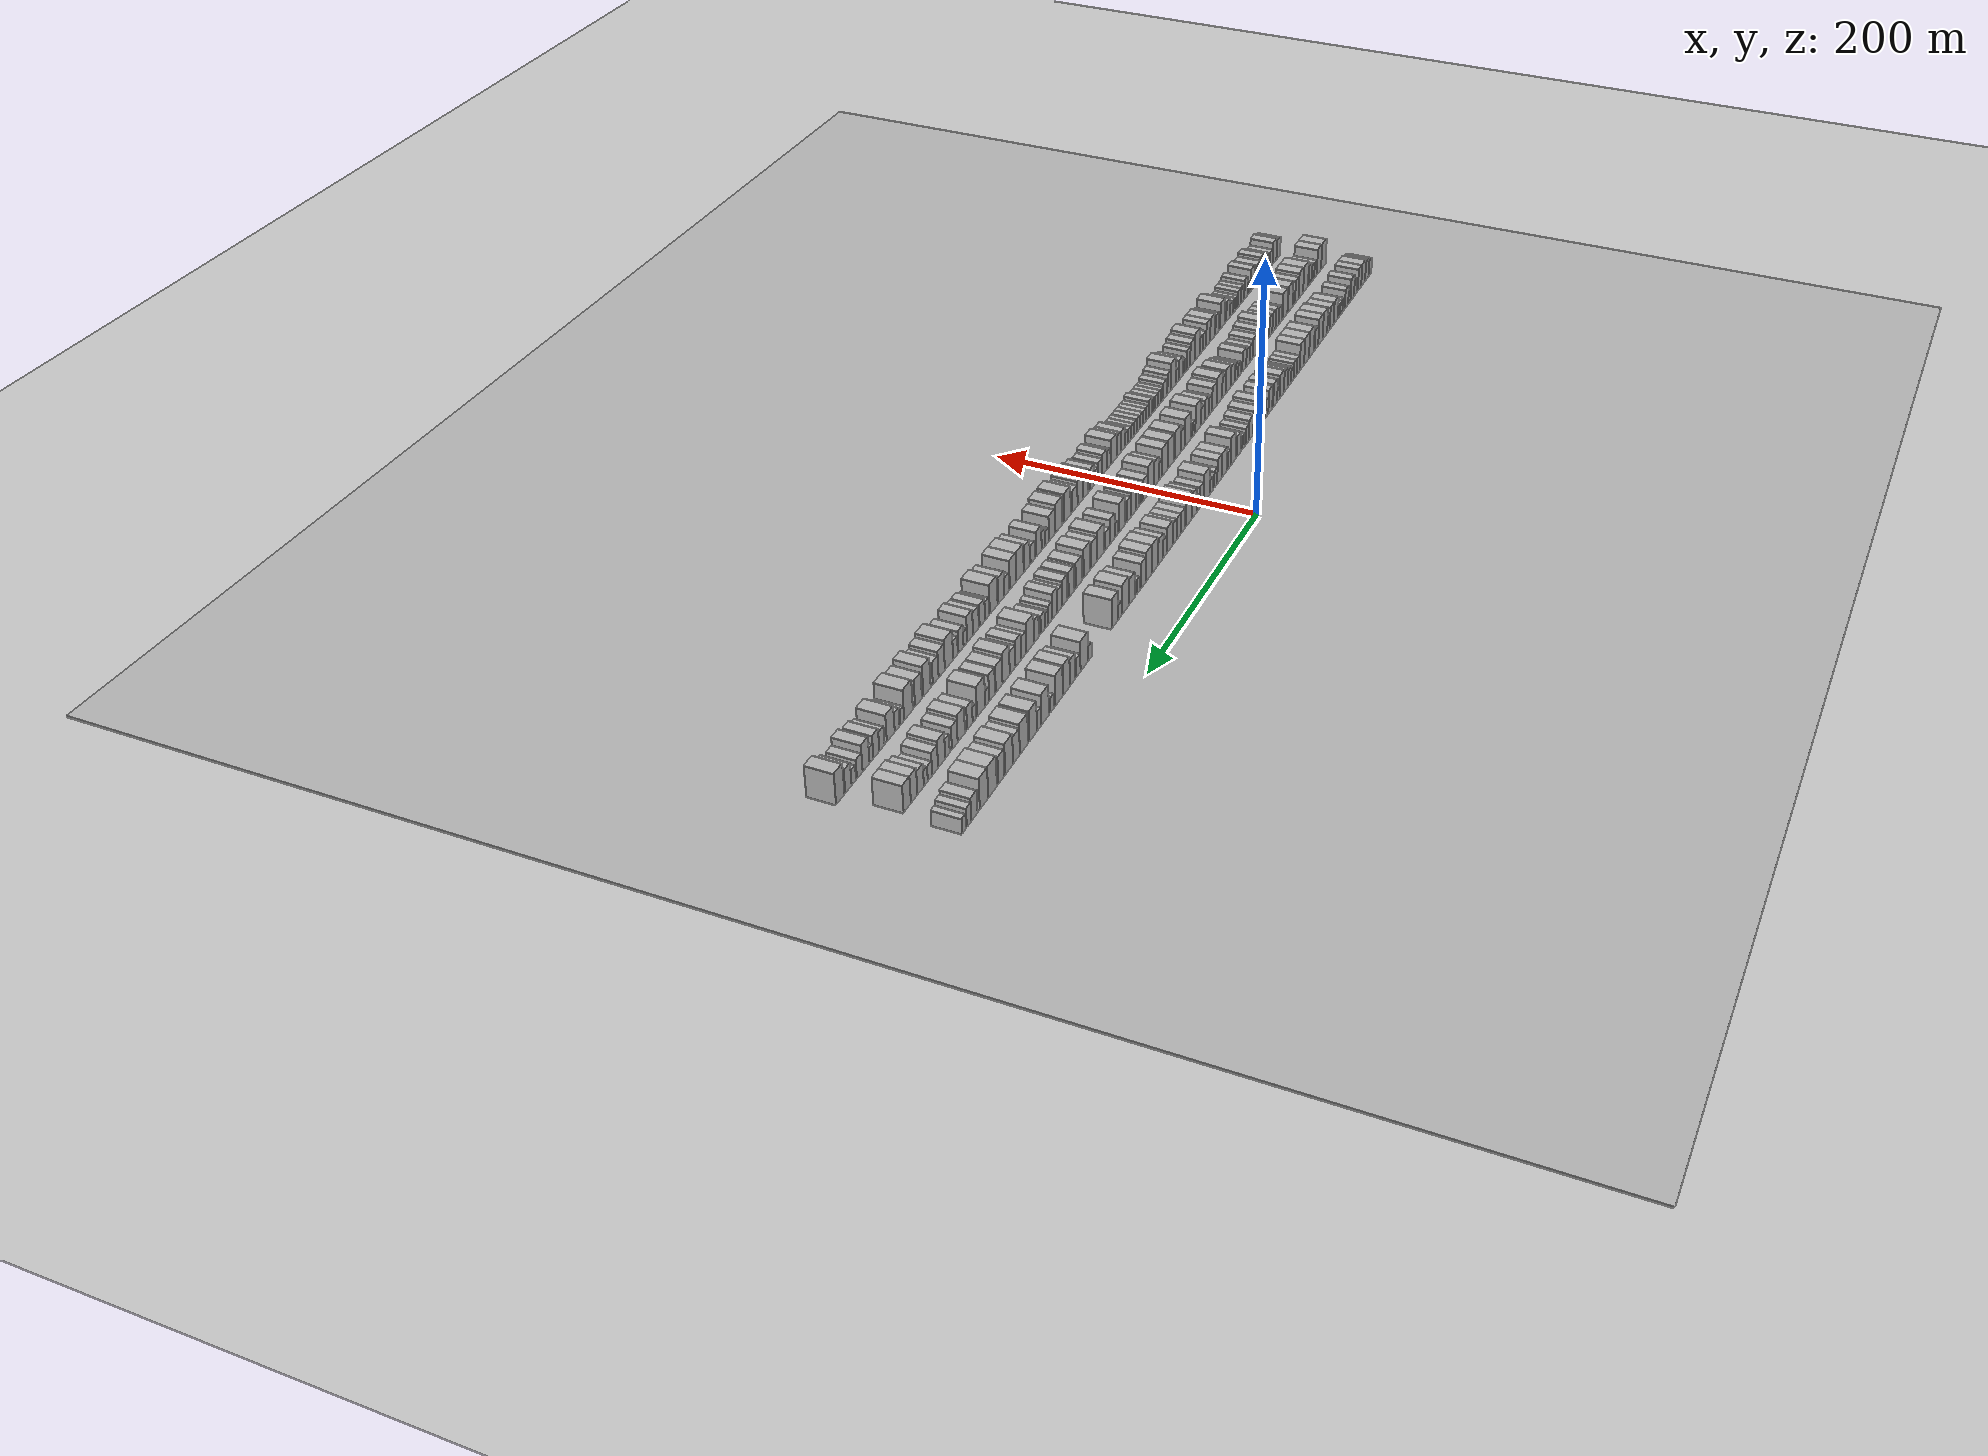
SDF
<?xml version="1.0" encoding="utf-8"?>

<sdf version="1.6">

   <world name="default">

      <gui fullscreen="0">

         <camera name="user_camera">

            <pose>-15 0 4.57585 0 0 0</pose>

            <view_controller>orbit</view_controller>

         </camera>

      </gui>

      <scene>

         <sky>

           <clouds>

             <speed>12</speed>

           </clouds>

         </sky>

         <ambient>0.4 0.4 0.4 1</ambient>

         <background>0.7 0.7 0.7 1</background>

         <shadows>1</shadows>

      </scene>

      <gravity>0 0 -9.8066</gravity>

      <magnetic_field>6e-06 2.3e-05 -4.2e-05</magnetic_field>

      <physics default="0" name="default_physics" type="ode">

         <ode>

            <solver>

               <type>quick</type>

               <iters>10</iters>

               <sor>1.0</sor>

               <use_dynamic_moi_rescaling>0</use_dynamic_moi_rescaling>

            </solver>

            <constraints>

               <cfm>0</cfm>

               <erp>0.2</erp>

               <contact_max_correcting_vel>100</contact_max_correcting_vel>

               <contact_surface_layer>0.001</contact_surface_layer>

            </constraints>

         </ode>

         <max_step_size>0.004</max_step_size>

         <real_time_factor>1</real_time_factor>

         <real_time_update_rate>250</real_time_update_rate>

      </physics>

      <light name="sun" type="directional">

         <cast_shadows>1</cast_shadows>

         <pose>0 0 10 0 0 0</pose>

         <diffuse>0.8 0.8 0.8 1</diffuse>

         <specular>0.2 0.2 0.2 1</specular>

         <attenuation>

            <range>1000</range>

            <constant>0.9</constant>

            <linear>0.01</linear>

            <quadratic>0.001</quadratic>

         </attenuation>

         <direction>-0.5 0.1 -0.9</direction>

      </light>

      <include>

         <name>ground_plane_1</name>

         <uri>model://HANNAS_ground_plane</uri>

         <pose>0 0 0  0 0 0</pose>

      </include>

      <include>

         <name>ground_plane_2</name>

         <uri>model://HANNAS_ground_plane</uri>

         <pose>100 0 0  0 0 0</pose>

      </include>

      <model name="building_1">

         <static>1</static>

         <pose frame="">50.0000 -375.3287 0 0.000000 0.000000 0.000000</pose>

         <link name="link">

            <pose frame="">0 0 7.50 0 0 0</pose>

            <collision name="collision">

               <geometry>

                  <box>

                     <size>20.0000 7.3426 15.0000</size>

                  </box>

               </geometry>

               <max_contacts>10</max_contacts>

               <surface>

                  <contact>

                     <ode/>

                  </contact>

                  <bounce/>

                  <friction>

                     <torsional>

                        <ode/>

                     </torsional>

                     <ode/>

                  </friction>

               </surface>

            </collision>

            <visual name="visual">

               <cast_shadows>0</cast_shadows>

               <geometry>

                  <box>

                     <size>20.0000 7.3426 15.0000</size>

                  </box>

               </geometry>

               <material>

                  <script>

                     <uri>model://HANNAS_wall/materials/scripts</uri>

                     <uri>model://HANNAS_wall/materials/textures</uri>

                     <name>vrc/HANNAS_wall</name>

                  </script>

               </material>

            </visual>

            <self_collide>0</self_collide>

            <enable_wind>0</enable_wind>

            <kinematic>0</kinematic>

         </link>

      </model>

      <model name="building_2">

         <static>1</static>

         <pose frame="">50.0000 -367.1831 0 0.000000 0.000000 0.000000</pose>

         <link name="link">

            <pose frame="">0 0 9.00 0 0 0</pose>

            <collision name="collision">

               <geometry>

                  <box>

                     <size>20.0000 8.9486 18.0000</size>

                  </box>

               </geometry>

               <max_contacts>10</max_contacts>

               <surface>

                  <contact>

                     <ode/>

                  </contact>

                  <bounce/>

                  <friction>

                     <torsional>

                        <ode/>

                     </torsional>

                     <ode/>

                  </friction>

               </surface>

            </collision>

            <visual name="visual">

               <cast_shadows>0</cast_shadows>

               <geometry>

                  <box>

                     <size>20.0000 8.9486 18.0000</size>

                  </box>

               </geometry>

               <material>

                  <script>

                     <uri>model://HANNAS_wall/materials/scripts</uri>

                     <uri>model://HANNAS_wall/materials/textures</uri>

                     <name>vrc/HANNAS_wall</name>

                  </script>

               </material>

            </visual>

            <self_collide>0</self_collide>

            <enable_wind>0</enable_wind>

            <kinematic>0</kinematic>

         </link>

      </model>

      <model name="building_3">

         <static>1</static>

         <pose frame="">50.0000 -357.5547 0 0.000000 0.000000 0.000000</pose>

         <link name="link">

            <pose frame="">0 0 10.50 0 0 0</pose>

            <collision name="collision">

               <geometry>

                  <box>

                     <size>20.0000 10.3081 21.0000</size>

                  </box>

               </geometry>

               <max_contacts>10</max_contacts>

               <surface>

                  <contact>

                     <ode/>

                  </contact>

                  <bounce/>

                  <friction>

                     <torsional>

                        <ode/>

                     </torsional>

                     <ode/>

                  </friction>

               </surface>

            </collision>

            <visual name="visual">

               <cast_shadows>0</cast_shadows>

               <geometry>

                  <box>

                     <size>20.0000 10.3081 21.0000</size>

                  </box>

               </geometry>

               <material>

                  <script>

                     <uri>model://HANNAS_wall/materials/scripts</uri>

                     <uri>model://HANNAS_wall/materials/textures</uri>

                     <name>vrc/HANNAS_wall</name>

                  </script>

               </material>

            </visual>

            <self_collide>0</self_collide>

            <enable_wind>0</enable_wind>

            <kinematic>0</kinematic>

         </link>

      </model>

      <model name="building_4">

         <static>1</static>

         <pose frame="">50.0000 -347.9794 0 0.000000 0.000000 0.000000</pose>

         <link name="link">

            <pose frame="">0 0 10.50 0 0 0</pose>

            <collision name="collision">

               <geometry>

                  <box>

                     <size>20.0000 8.8426 21.0000</size>

                  </box>

               </geometry>

               <max_contacts>10</max_contacts>

               <surface>

                  <contact>

                     <ode/>

                  </contact>

                  <bounce/>

                  <friction>

                     <torsional>

                        <ode/>

                     </torsional>

                     <ode/>

                  </friction>

               </surface>

            </collision>

            <visual name="visual">

               <cast_shadows>0</cast_shadows>

               <geometry>

                  <box>

                     <size>20.0000 8.8426 21.0000</size>

                  </box>

               </geometry>

               <material>

                  <script>

                     <uri>model://HANNAS_wall/materials/scripts</uri>

                     <uri>model://HANNAS_wall/materials/textures</uri>

                     <name>vrc/HANNAS_wall</name>

                  </script>

               </material>

            </visual>

            <self_collide>0</self_collide>

            <enable_wind>0</enable_wind>

            <kinematic>0</kinematic>

         </link>

      </model>

      <model name="building_5">

         <static>1</static>

         <pose frame="">50.0000 -337.1684 0 0.000000 0.000000 0.000000</pose>

         <link name="link">

            <pose frame="">0 0 7.50 0 0 0</pose>

            <collision name="collision">

               <geometry>

                  <box>

                     <size>20.0000 6.7795 15.0000</size>

                  </box>

               </geometry>

               <max_contacts>10</max_contacts>

               <surface>

                  <contact>

                     <ode/>

                  </contact>

                  <bounce/>

                  <friction>

                     <torsional>

                        <ode/>

                     </torsional>

                     <ode/>

                  </friction>

               </surface>

            </collision>

            <visual name="visual">

               <cast_shadows>0</cast_shadows>

               <geometry>

                  <box>

                     <size>20.0000 6.7795 15.0000</size>

                  </box>

               </geometry>

               <material>

                  <script>

                     <uri>model://HANNAS_wall/materials/scripts</uri>

                     <uri>model://HANNAS_wall/materials/textures</uri>

                     <name>vrc/HANNAS_wall</name>

                  </script>

               </material>

            </visual>

            <self_collide>0</self_collide>

            <enable_wind>0</enable_wind>

            <kinematic>0</kinematic>

         </link>

      </model>

      <model name="building_6">

         <static>1</static>

         <pose frame="">50.0000 -329.2807 0 0.000000 0.000000 0.000000</pose>

         <link name="link">

            <pose frame="">0 0 10.50 0 0 0</pose>

            <collision name="collision">

               <geometry>

                  <box>

                     <size>20.0000 8.9958 21.0000</size>

                  </box>

               </geometry>

               <max_contacts>10</max_contacts>

               <surface>

                  <contact>

                     <ode/>

                  </contact>

                  <bounce/>

                  <friction>

                     <torsional>

                        <ode/>

                     </torsional>

                     <ode/>

                  </friction>

               </surface>

            </collision>

            <visual name="visual">

               <cast_shadows>0</cast_shadows>

               <geometry>

                  <box>

                     <size>20.0000 8.9958 21.0000</size>

                  </box>

               </geometry>

               <material>

                  <script>

                     <uri>model://HANNAS_wall/materials/scripts</uri>

                     <uri>model://HANNAS_wall/materials/textures</uri>

                     <name>vrc/HANNAS_wall</name>

                  </script>

               </material>

            </visual>

            <self_collide>0</self_collide>

            <enable_wind>0</enable_wind>

            <kinematic>0</kinematic>

         </link>

      </model>

      <model name="building_7">

         <static>1</static>

         <pose frame="">50.0000 -321.9267 0 0.000000 0.000000 0.000000</pose>

         <link name="link">

            <pose frame="">0 0 6.00 0 0 0</pose>

            <collision name="collision">

               <geometry>

                  <box>

                     <size>20.0000 5.7122 12.0000</size>

                  </box>

               </geometry>

               <max_contacts>10</max_contacts>

               <surface>

                  <contact>

                     <ode/>

                  </contact>

                  <bounce/>

                  <friction>

                     <torsional>

                        <ode/>

                     </torsional>

                     <ode/>

                  </friction>

               </surface>

            </collision>

            <visual name="visual">

               <cast_shadows>0</cast_shadows>

               <geometry>

                  <box>

                     <size>20.0000 5.7122 12.0000</size>

                  </box>

               </geometry>

               <material>

                  <script>

                     <uri>model://HANNAS_wall/materials/scripts</uri>

                     <uri>model://HANNAS_wall/materials/textures</uri>

                     <name>vrc/HANNAS_wall</name>

                  </script>

               </material>

            </visual>

            <self_collide>0</self_collide>

            <enable_wind>0</enable_wind>

            <kinematic>0</kinematic>

         </link>

      </model>

      <model name="building_8">

         <static>1</static>

         <pose frame="">50.0000 -314.7755 0 0.000000 0.000000 0.000000</pose>

         <link name="link">

            <pose frame="">0 0 9.00 0 0 0</pose>

            <collision name="collision">

               <geometry>

                  <box>

                     <size>20.0000 8.5903 18.0000</size>

                  </box>

               </geometry>

               <max_contacts>10</max_contacts>

               <surface>

                  <contact>

                     <ode/>

                  </contact>

                  <bounce/>

                  <friction>

                     <torsional>

                        <ode/>

                     </torsional>

                     <ode/>

                  </friction>

               </surface>

            </collision>

            <visual name="visual">

               <cast_shadows>0</cast_shadows>

               <geometry>

                  <box>

                     <size>20.0000 8.5903 18.0000</size>

                  </box>

               </geometry>

               <material>

                  <script>

                     <uri>model://HANNAS_wall/materials/scripts</uri>

                     <uri>model://HANNAS_wall/materials/textures</uri>

                     <name>vrc/HANNAS_wall</name>

                  </script>

               </material>

            </visual>

            <self_collide>0</self_collide>

            <enable_wind>0</enable_wind>

            <kinematic>0</kinematic>

         </link>

      </model>

      <model name="building_9">

         <static>1</static>

         <pose frame="">50.0000 -307.0648 0 0.000000 0.000000 0.000000</pose>

         <link name="link">

            <pose frame="">0 0 6.00 0 0 0</pose>

            <collision name="collision">

               <geometry>

                  <box>

                     <size>20.0000 4.8309 12.0000</size>

                  </box>

               </geometry>

               <max_contacts>10</max_contacts>

               <surface>

                  <contact>

                     <ode/>

                  </contact>

                  <bounce/>

                  <friction>

                     <torsional>

                        <ode/>

                     </torsional>

                     <ode/>

                  </friction>

               </surface>

            </collision>

            <visual name="visual">

               <cast_shadows>0</cast_shadows>

               <geometry>

                  <box>

                     <size>20.0000 4.8309 12.0000</size>

                  </box>

               </geometry>

               <material>

                  <script>

                     <uri>model://HANNAS_wall/materials/scripts</uri>

                     <uri>model://HANNAS_wall/materials/textures</uri>

                     <name>vrc/HANNAS_wall</name>

                  </script>

               </material>

            </visual>

            <self_collide>0</self_collide>

            <enable_wind>0</enable_wind>

            <kinematic>0</kinematic>

         </link>

      </model>

      <model name="building_10">

         <static>1</static>

         <pose frame="">50.0000 -301.6668 0 0.000000 0.000000 0.000000</pose>

         <link name="link">

            <pose frame="">0 0 6.00 0 0 0</pose>

            <collision name="collision">

               <geometry>

                  <box>

                     <size>20.0000 5.9651 12.0000</size>

                  </box>

               </geometry>

               <max_contacts>10</max_contacts>

               <surface>

                  <contact>

                     <ode/>

                  </contact>

                  <bounce/>

                  <friction>

                     <torsional>

                        <ode/>

                     </torsional>

                     <ode/>

                  </friction>

               </surface>

            </collision>

            <visual name="visual">

               <cast_shadows>0</cast_shadows>

               <geometry>

                  <box>

                     <size>20.0000 5.9651 12.0000</size>

                  </box>

               </geometry>

               <material>

                  <script>

                     <uri>model://HANNAS_wall/materials/scripts</uri>

                     <uri>model://HANNAS_wall/materials/textures</uri>

                     <name>vrc/HANNAS_wall</name>

                  </script>

               </material>

            </visual>

            <self_collide>0</self_collide>

            <enable_wind>0</enable_wind>

            <kinematic>0</kinematic>

         </link>

      </model>

      <model name="building_11">

         <static>1</static>

         <pose frame="">50.0000 -295.7487 0 0.000000 0.000000 0.000000</pose>

         <link name="link">

            <pose frame="">0 0 6.00 0 0 0</pose>

            <collision name="collision">

               <geometry>

                  <box>

                     <size>20.0000 5.8713 12.0000</size>

                  </box>

               </geometry>

               <max_contacts>10</max_contacts>

               <surface>

                  <contact>

                     <ode/>

                  </contact>

                  <bounce/>

                  <friction>

                     <torsional>

                        <ode/>

                     </torsional>

                     <ode/>

                  </friction>

               </surface>

            </collision>

            <visual name="visual">

               <cast_shadows>0</cast_shadows>

               <geometry>

                  <box>

                     <size>20.0000 5.8713 12.0000</size>

                  </box>

               </geometry>

               <material>

                  <script>

                     <uri>model://HANNAS_wall/materials/scripts</uri>

                     <uri>model://HANNAS_wall/materials/textures</uri>

                     <name>vrc/HANNAS_wall</name>

                  </script>

               </material>

            </visual>

            <self_collide>0</self_collide>

            <enable_wind>0</enable_wind>

            <kinematic>0</kinematic>

         </link>

      </model>

      <model name="building_12">

         <static>1</static>

         <pose frame="">50.0000 -287.6685 0 0.000000 0.000000 0.000000</pose>

         <link name="link">

            <pose frame="">0 0 10.50 0 0 0</pose>

            <collision name="collision">

               <geometry>

                  <box>

                     <size>20.0000 10.2891 21.0000</size>

                  </box>

               </geometry>

               <max_contacts>10</max_contacts>

               <surface>

                  <contact>

                     <ode/>

                  </contact>

                  <bounce/>

                  <friction>

                     <torsional>

                        <ode/>

                     </torsional>

                     <ode/>

                  </friction>

               </surface>

            </collision>

            <visual name="visual">

               <cast_shadows>0</cast_shadows>

               <geometry>

                  <box>

                     <size>20.0000 10.2891 21.0000</size>

                  </box>

               </geometry>

               <material>

                  <script>

                     <uri>model://HANNAS_wall/materials/scripts</uri>

                     <uri>model://HANNAS_wall/materials/textures</uri>

                     <name>vrc/HANNAS_wall</name>

                  </script>

               </material>

            </visual>

            <self_collide>0</self_collide>

            <enable_wind>0</enable_wind>

            <kinematic>0</kinematic>

         </link>

      </model>

      <model name="building_13">

         <static>1</static>

         <pose frame="">50.0000 -277.7995 0 0.000000 0.000000 0.000000</pose>

         <link name="link">

            <pose frame="">0 0 10.50 0 0 0</pose>

            <collision name="collision">

               <geometry>

                  <box>

                     <size>20.0000 9.4488 21.0000</size>

                  </box>

               </geometry>

               <max_contacts>10</max_contacts>

               <surface>

                  <contact>

                     <ode/>

                  </contact>

                  <bounce/>

                  <friction>

                     <torsional>

                        <ode/>

                     </torsional>

                     <ode/>

                  </friction>

               </surface>

            </collision>

            <visual name="visual">

               <cast_shadows>0</cast_shadows>

               <geometry>

                  <box>

                     <size>20.0000 9.4488 21.0000</size>

                  </box>

               </geometry>

               <material>

                  <script>

                     <uri>model://HANNAS_wall/materials/scripts</uri>

                     <uri>model://HANNAS_wall/materials/textures</uri>

                     <name>vrc/HANNAS_wall</name>

                  </script>

               </material>

            </visual>

            <self_collide>0</self_collide>

            <enable_wind>0</enable_wind>

            <kinematic>0</kinematic>

         </link>

      </model>

      <model name="building_14">

         <static>1</static>

         <pose frame="">50.0000 -270.0500 0 0.000000 0.000000 0.000000</pose>

         <link name="link">

            <pose frame="">0 0 7.50 0 0 0</pose>

            <collision name="collision">

               <geometry>

                  <box>

                     <size>20.0000 6.0503 15.0000</size>

                  </box>

               </geometry>

               <max_contacts>10</max_contacts>

               <surface>

                  <contact>

                     <ode/>

                  </contact>

                  <bounce/>

                  <friction>

                     <torsional>

                        <ode/>

                     </torsional>

                     <ode/>

                  </friction>

               </surface>

            </collision>

            <visual name="visual">

               <cast_shadows>0</cast_shadows>

               <geometry>

                  <box>

                     <size>20.0000 6.0503 15.0000</size>

                  </box>

               </geometry>

               <material>

                  <script>

                     <uri>model://HANNAS_wall/materials/scripts</uri>

                     <uri>model://HANNAS_wall/materials/textures</uri>

                     <name>vrc/HANNAS_wall</name>

                  </script>

               </material>

            </visual>

            <self_collide>0</self_collide>

            <enable_wind>0</enable_wind>

            <kinematic>0</kinematic>

         </link>

      </model>

      <model name="building_15">

         <static>1</static>

         <pose frame="">50.0000 -261.5179 0 0.000000 0.000000 0.000000</pose>

         <link name="link">

            <pose frame="">0 0 12.00 0 0 0</pose>

            <collision name="collision">

               <geometry>

                  <box>

                     <size>20.0000 11.0138 24.0000</size>

                  </box>

               </geometry>

               <max_contacts>10</max_contacts>

               <surface>

                  <contact>

                     <ode/>

                  </contact>

                  <bounce/>

                  <friction>

                     <torsional>

                        <ode/>

                     </torsional>

                     <ode/>

                  </friction>

               </surface>

            </collision>

            <visual name="visual">

               <cast_shadows>0</cast_shadows>

               <geometry>

                  <box>

                     <size>20.0000 11.0138 24.0000</size>

                  </box>

               </geometry>

               <material>

                  <script>

                     <uri>model://HANNAS_wall/materials/scripts</uri>

                     <uri>model://HANNAS_wall/materials/textures</uri>

                     <name>vrc/HANNAS_wall</name>

                  </script>

               </material>

            </visual>

            <self_collide>0</self_collide>

            <enable_wind>0</enable_wind>

            <kinematic>0</kinematic>

         </link>

      </model>

      <model name="building_16">

         <static>1</static>

         <pose frame="">50.0000 -250.7442 0 0.000000 0.000000 0.000000</pose>

         <link name="link">

            <pose frame="">0 0 12.00 0 0 0</pose>

            <collision name="collision">

               <geometry>

                  <box>

                     <size>20.0000 10.5337 24.0000</size>

                  </box>

               </geometry>

               <max_contacts>10</max_contacts>

               <surface>

                  <contact>

                     <ode/>

                  </contact>

                  <bounce/>

                  <friction>

                     <torsional>

                        <ode/>

                     </torsional>

                     <ode/>

                  </friction>

               </surface>

            </collision>

            <visual name="visual">

               <cast_shadows>0</cast_shadows>

               <geometry>

                  <box>

                     <size>20.0000 10.5337 24.0000</size>

                  </box>

               </geometry>

               <material>

                  <script>

                     <uri>model://HANNAS_wall/materials/scripts</uri>

                     <uri>model://HANNAS_wall/materials/textures</uri>

                     <name>vrc/HANNAS_wall</name>

                  </script>

               </material>

            </visual>

            <self_collide>0</self_collide>

            <enable_wind>0</enable_wind>

            <kinematic>0</kinematic>

         </link>

      </model>

      <model name="building_17">

         <static>1</static>

         <pose frame="">50.0000 -241.1587 0 0.000000 0.000000 0.000000</pose>

         <link name="link">

            <pose frame="">0 0 9.00 0 0 0</pose>

            <collision name="collision">

               <geometry>

                  <box>

                     <size>20.0000 8.6373 18.0000</size>

                  </box>

               </geometry>

               <max_contacts>10</max_contacts>

               <surface>

                  <contact>

                     <ode/>

                  </contact>

                  <bounce/>

                  <friction>

                     <torsional>

                        <ode/>

                     </torsional>

                     <ode/>

                  </friction>

               </surface>

            </collision>

            <visual name="visual">

               <cast_shadows>0</cast_shadows>

               <geometry>

                  <box>

                     <size>20.0000 8.6373 18.0000</size>

                  </box>

               </geometry>

               <material>

                  <script>

                     <uri>model://HANNAS_wall/materials/scripts</uri>

                     <uri>model://HANNAS_wall/materials/textures</uri>

                     <name>vrc/HANNAS_wall</name>

                  </script>

               </material>

            </visual>

            <self_collide>0</self_collide>

            <enable_wind>0</enable_wind>

            <kinematic>0</kinematic>

         </link>

      </model>

      <model name="building_18">

         <static>1</static>

         <pose frame="">50.0000 -229.2671 0 0.000000 0.000000 0.000000</pose>

         <link name="link">

            <pose frame="">0 0 12.00 0 0 0</pose>

            <collision name="collision">

               <geometry>

                  <box>

                     <size>20.0000 11.1459 24.0000</size>

                  </box>

               </geometry>

               <max_contacts>10</max_contacts>

               <surface>

                  <contact>

                     <ode/>

                  </contact>

                  <bounce/>

                  <friction>

                     <torsional>

                        <ode/>

                     </torsional>

                     <ode/>

                  </friction>

               </surface>

            </collision>

            <visual name="visual">

               <cast_shadows>0</cast_shadows>

               <geometry>

                  <box>

                     <size>20.0000 11.1459 24.0000</size>

                  </box>

               </geometry>

               <material>

                  <script>

                     <uri>model://HANNAS_wall/materials/scripts</uri>

                     <uri>model://HANNAS_wall/materials/textures</uri>

                     <name>vrc/HANNAS_wall</name>

                  </script>

               </material>

            </visual>

            <self_collide>0</self_collide>

            <enable_wind>0</enable_wind>

            <kinematic>0</kinematic>

         </link>

      </model>

      <model name="building_19">

         <static>1</static>

         <pose frame="">50.0000 -217.9231 0 0.000000 0.000000 0.000000</pose>

         <link name="link">

            <pose frame="">0 0 12.00 0 0 0</pose>

            <collision name="collision">

               <geometry>

                  <box>

                     <size>20.0000 11.5422 24.0000</size>

                  </box>

               </geometry>

               <max_contacts>10</max_contacts>

               <surface>

                  <contact>

                     <ode/>

                  </contact>

                  <bounce/>

                  <friction>

                     <torsional>

                        <ode/>

                     </torsional>

                     <ode/>

                  </friction>

               </surface>

            </collision>

            <visual name="visual">

               <cast_shadows>0</cast_shadows>

               <geometry>

                  <box>

                     <size>20.0000 11.5422 24.0000</size>

                  </box>

               </geometry>

               <material>

                  <script>

                     <uri>model://HANNAS_wall/materials/scripts</uri>

                     <uri>model://HANNAS_wall/materials/textures</uri>

                     <name>vrc/HANNAS_wall</name>

                  </script>

               </material>

            </visual>

            <self_collide>0</self_collide>

            <enable_wind>0</enable_wind>

            <kinematic>0</kinematic>

         </link>

      </model>

      <model name="building_20">

         <static>1</static>

         <pose frame="">50.0000 -207.0150 0 0.000000 0.000000 0.000000</pose>

         <link name="link">

            <pose frame="">0 0 12.00 0 0 0</pose>

            <collision name="collision">

               <geometry>

                  <box>

                     <size>20.0000 10.2741 24.0000</size>

                  </box>

               </geometry>

               <max_contacts>10</max_contacts>

               <surface>

                  <contact>

                     <ode/>

                  </contact>

                  <bounce/>

                  <friction>

                     <torsional>

                        <ode/>

                     </torsional>

                     <ode/>

                  </friction>

               </surface>

            </collision>

            <visual name="visual">

               <cast_shadows>0</cast_shadows>

               <geometry>

                  <box>

                     <size>20.0000 10.2741 24.0000</size>

                  </box>

               </geometry>

               <material>

                  <script>

                     <uri>model://HANNAS_wall/materials/scripts</uri>

                     <uri>model://HANNAS_wall/materials/textures</uri>

                     <name>vrc/HANNAS_wall</name>

                  </script>

               </material>

            </visual>

            <self_collide>0</self_collide>

            <enable_wind>0</enable_wind>

            <kinematic>0</kinematic>

         </link>

      </model>

      <model name="building_21">

         <static>1</static>

         <pose frame="">50.0000 -198.2730 0 0.000000 0.000000 0.000000</pose>

         <link name="link">

            <pose frame="">0 0 7.50 0 0 0</pose>

            <collision name="collision">

               <geometry>

                  <box>

                     <size>20.0000 7.2099 15.0000</size>

                  </box>

               </geometry>

               <max_contacts>10</max_contacts>

               <surface>

                  <contact>

                     <ode/>

                  </contact>

                  <bounce/>

                  <friction>

                     <torsional>

                        <ode/>

                     </torsional>

                     <ode/>

                  </friction>

               </surface>

            </collision>

            <visual name="visual">

               <cast_shadows>0</cast_shadows>

               <geometry>

                  <box>

                     <size>20.0000 7.2099 15.0000</size>

                  </box>

               </geometry>

               <material>

                  <script>

                     <uri>model://HANNAS_wall/materials/scripts</uri>

                     <uri>model://HANNAS_wall/materials/textures</uri>

                     <name>vrc/HANNAS_wall</name>

                  </script>

               </material>

            </visual>

            <self_collide>0</self_collide>

            <enable_wind>0</enable_wind>

            <kinematic>0</kinematic>

         </link>

      </model>

      <model name="building_22">

         <static>1</static>

         <pose frame="">50.0000 -191.3809 0 0.000000 0.000000 0.000000</pose>

         <link name="link">

            <pose frame="">0 0 7.50 0 0 0</pose>

            <collision name="collision">

               <geometry>

                  <box>

                     <size>20.0000 6.5743 15.0000</size>

                  </box>

               </geometry>

               <max_contacts>10</max_contacts>

               <surface>

                  <contact>

                     <ode/>

                  </contact>

                  <bounce/>

                  <friction>

                     <torsional>

                        <ode/>

                     </torsional>

                     <ode/>

                  </friction>

               </surface>

            </collision>

            <visual name="visual">

               <cast_shadows>0</cast_shadows>

               <geometry>

                  <box>

                     <size>20.0000 6.5743 15.0000</size>

                  </box>

               </geometry>

               <material>

                  <script>

                     <uri>model://HANNAS_wall/materials/scripts</uri>

                     <uri>model://HANNAS_wall/materials/textures</uri>

                     <name>vrc/HANNAS_wall</name>

                  </script>

               </material>

            </visual>

            <self_collide>0</self_collide>

            <enable_wind>0</enable_wind>

            <kinematic>0</kinematic>

         </link>

      </model>

      <model name="building_23">

         <static>1</static>

         <pose frame="">50.0000 -185.1483 0 0.000000 0.000000 0.000000</pose>

         <link name="link">

            <pose frame="">0 0 6.00 0 0 0</pose>

            <collision name="collision">

               <geometry>

                  <box>

                     <size>20.0000 5.8909 12.0000</size>

                  </box>

               </geometry>

               <max_contacts>10</max_contacts>

               <surface>

                  <contact>

                     <ode/>

                  </contact>

                  <bounce/>

                  <friction>

                     <torsional>

                        <ode/>

                     </torsional>

                     <ode/>

                  </friction>

               </surface>

            </collision>

            <visual name="visual">

               <cast_shadows>0</cast_shadows>

               <geometry>

                  <box>

                     <size>20.0000 5.8909 12.0000</size>

                  </box>

               </geometry>

               <material>

                  <script>

                     <uri>model://HANNAS_wall/materials/scripts</uri>

                     <uri>model://HANNAS_wall/materials/textures</uri>

                     <name>vrc/HANNAS_wall</name>

                  </script>

               </material>

            </visual>

            <self_collide>0</self_collide>

            <enable_wind>0</enable_wind>

            <kinematic>0</kinematic>

         </link>

      </model>

      <model name="building_24">

         <static>1</static>

         <pose frame="">50.0000 -178.5799 0 0.000000 0.000000 0.000000</pose>

         <link name="link">

            <pose frame="">0 0 7.50 0 0 0</pose>

            <collision name="collision">

               <geometry>

                  <box>

                     <size>20.0000 7.2459 15.0000</size>

                  </box>

               </geometry>

               <max_contacts>10</max_contacts>

               <surface>

                  <contact>

                     <ode/>

                  </contact>

                  <bounce/>

                  <friction>

                     <torsional>

                        <ode/>

                     </torsional>

                     <ode/>

                  </friction>

               </surface>

            </collision>

            <visual name="visual">

               <cast_shadows>0</cast_shadows>

               <geometry>

                  <box>

                     <size>20.0000 7.2459 15.0000</size>

                  </box>

               </geometry>

               <material>

                  <script>

                     <uri>model://HANNAS_wall/materials/scripts</uri>

                     <uri>model://HANNAS_wall/materials/textures</uri>

                     <name>vrc/HANNAS_wall</name>

                  </script>

               </material>

            </visual>

            <self_collide>0</self_collide>

            <enable_wind>0</enable_wind>

            <kinematic>0</kinematic>

         </link>

      </model>

      <model name="building_25">

         <static>1</static>

         <pose frame="">50.0000 -170.5473 0 0.000000 0.000000 0.000000</pose>

         <link name="link">

            <pose frame="">0 0 9.00 0 0 0</pose>

            <collision name="collision">

               <geometry>

                  <box>

                     <size>20.0000 8.8192 18.0000</size>

                  </box>

               </geometry>

               <max_contacts>10</max_contacts>

               <surface>

                  <contact>

                     <ode/>

                  </contact>

                  <bounce/>

                  <friction>

                     <torsional>

                        <ode/>

                     </torsional>

                     <ode/>

                  </friction>

               </surface>

            </collision>

            <visual name="visual">

               <cast_shadows>0</cast_shadows>

               <geometry>

                  <box>

                     <size>20.0000 8.8192 18.0000</size>

                  </box>

               </geometry>

               <material>

                  <script>

                     <uri>model://HANNAS_wall/materials/scripts</uri>

                     <uri>model://HANNAS_wall/materials/textures</uri>

                     <name>vrc/HANNAS_wall</name>

                  </script>

               </material>

            </visual>

            <self_collide>0</self_collide>

            <enable_wind>0</enable_wind>

            <kinematic>0</kinematic>

         </link>

      </model>

      <model name="building_26">

         <static>1</static>

         <pose frame="">50.0000 -161.2789 0 0.000000 0.000000 0.000000</pose>

         <link name="link">

            <pose frame="">0 0 10.50 0 0 0</pose>

            <collision name="collision">

               <geometry>

                  <box>

                     <size>20.0000 9.7175 21.0000</size>

                  </box>

               </geometry>

               <max_contacts>10</max_contacts>

               <surface>

                  <contact>

                     <ode/>

                  </contact>

                  <bounce/>

                  <friction>

                     <torsional>

                        <ode/>

                     </torsional>

                     <ode/>

                  </friction>

               </surface>

            </collision>

            <visual name="visual">

               <cast_shadows>0</cast_shadows>

               <geometry>

                  <box>

                     <size>20.0000 9.7175 21.0000</size>

                  </box>

               </geometry>

               <material>

                  <script>

                     <uri>model://HANNAS_wall/materials/scripts</uri>

                     <uri>model://HANNAS_wall/materials/textures</uri>

                     <name>vrc/HANNAS_wall</name>

                  </script>

               </material>

            </visual>

            <self_collide>0</self_collide>

            <enable_wind>0</enable_wind>

            <kinematic>0</kinematic>

         </link>

      </model>

      <model name="building_27">

         <static>1</static>

         <pose frame="">50.0000 -153.7344 0 0.000000 0.000000 0.000000</pose>

         <link name="link">

            <pose frame="">0 0 6.00 0 0 0</pose>

            <collision name="collision">

               <geometry>

                  <box>

                     <size>20.0000 5.3715 12.0000</size>

                  </box>

               </geometry>

               <max_contacts>10</max_contacts>

               <surface>

                  <contact>

                     <ode/>

                  </contact>

                  <bounce/>

                  <friction>

                     <torsional>

                        <ode/>

                     </torsional>

                     <ode/>

                  </friction>

               </surface>

            </collision>

            <visual name="visual">

               <cast_shadows>0</cast_shadows>

               <geometry>

                  <box>

                     <size>20.0000 5.3715 12.0000</size>

                  </box>

               </geometry>

               <material>

                  <script>

                     <uri>model://HANNAS_wall/materials/scripts</uri>

                     <uri>model://HANNAS_wall/materials/textures</uri>

                     <name>vrc/HANNAS_wall</name>

                  </script>

               </material>

            </visual>

            <self_collide>0</self_collide>

            <enable_wind>0</enable_wind>

            <kinematic>0</kinematic>

         </link>

      </model>

      <model name="building_28">

         <static>1</static>

         <pose frame="">50.0000 -146.6572 0 0.000000 0.000000 0.000000</pose>

         <link name="link">

            <pose frame="">0 0 10.50 0 0 0</pose>

            <collision name="collision">

               <geometry>

                  <box>

                     <size>20.0000 8.7830 21.0000</size>

                  </box>

               </geometry>

               <max_contacts>10</max_contacts>

               <surface>

                  <contact>

                     <ode/>

                  </contact>

                  <bounce/>

                  <friction>

                     <torsional>

                        <ode/>

                     </torsional>

                     <ode/>

                  </friction>

               </surface>

            </collision>

            <visual name="visual">

               <cast_shadows>0</cast_shadows>

               <geometry>

                  <box>

                     <size>20.0000 8.7830 21.0000</size>

                  </box>

               </geometry>

               <material>

                  <script>

                     <uri>model://HANNAS_wall/materials/scripts</uri>

                     <uri>model://HANNAS_wall/materials/textures</uri>

                     <name>vrc/HANNAS_wall</name>

                  </script>

               </material>

            </visual>

            <self_collide>0</self_collide>

            <enable_wind>0</enable_wind>

            <kinematic>0</kinematic>

         </link>

      </model>

      <model name="building_29">

         <static>1</static>

         <pose frame="">50.0000 -136.0316 0 0.000000 0.000000 0.000000</pose>

         <link name="link">

            <pose frame="">0 0 10.50 0 0 0</pose>

            <collision name="collision">

               <geometry>

                  <box>

                     <size>20.0000 8.4683 21.0000</size>

                  </box>

               </geometry>

               <max_contacts>10</max_contacts>

               <surface>

                  <contact>

                     <ode/>

                  </contact>

                  <bounce/>

                  <friction>

                     <torsional>

                        <ode/>

                     </torsional>

                     <ode/>

                  </friction>

               </surface>

            </collision>

            <visual name="visual">

               <cast_shadows>0</cast_shadows>

               <geometry>

                  <box>

                     <size>20.0000 8.4683 21.0000</size>

                  </box>

               </geometry>

               <material>

                  <script>

                     <uri>model://HANNAS_wall/materials/scripts</uri>

                     <uri>model://HANNAS_wall/materials/textures</uri>

                     <name>vrc/HANNAS_wall</name>

                  </script>

               </material>

            </visual>

            <self_collide>0</self_collide>

            <enable_wind>0</enable_wind>

            <kinematic>0</kinematic>

         </link>

      </model>

      <model name="building_30">

         <static>1</static>

         <pose frame="">50.0000 -128.5220 0 0.000000 0.000000 0.000000</pose>

         <link name="link">

            <pose frame="">0 0 7.50 0 0 0</pose>

            <collision name="collision">

               <geometry>

                  <box>

                     <size>20.0000 6.5510 15.0000</size>

                  </box>

               </geometry>

               <max_contacts>10</max_contacts>

               <surface>

                  <contact>

                     <ode/>

                  </contact>

                  <bounce/>

                  <friction>

                     <torsional>

                        <ode/>

                     </torsional>

                     <ode/>

                  </friction>

               </surface>

            </collision>

            <visual name="visual">

               <cast_shadows>0</cast_shadows>

               <geometry>

                  <box>

                     <size>20.0000 6.5510 15.0000</size>

                  </box>

               </geometry>

               <material>

                  <script>

                     <uri>model://HANNAS_wall/materials/scripts</uri>

                     <uri>model://HANNAS_wall/materials/textures</uri>

                     <name>vrc/HANNAS_wall</name>

                  </script>

               </material>

            </visual>

            <self_collide>0</self_collide>

            <enable_wind>0</enable_wind>

            <kinematic>0</kinematic>

         </link>

      </model>

      <model name="building_31">

         <static>1</static>

         <pose frame="">50.0000 -121.9034 0 0.000000 0.000000 0.000000</pose>

         <link name="link">

            <pose frame="">0 0 7.50 0 0 0</pose>

            <collision name="collision">

               <geometry>

                  <box>

                     <size>20.0000 6.6861 15.0000</size>

                  </box>

               </geometry>

               <max_contacts>10</max_contacts>

               <surface>

                  <contact>

                     <ode/>

                  </contact>

                  <bounce/>

                  <friction>

                     <torsional>

                        <ode/>

                     </torsional>

                     <ode/>

                  </friction>

               </surface>

            </collision>

            <visual name="visual">

               <cast_shadows>0</cast_shadows>

               <geometry>

                  <box>

                     <size>20.0000 6.6861 15.0000</size>

                  </box>

               </geometry>

               <material>

                  <script>

                     <uri>model://HANNAS_wall/materials/scripts</uri>

                     <uri>model://HANNAS_wall/materials/textures</uri>

                     <name>vrc/HANNAS_wall</name>

                  </script>

               </material>

            </visual>

            <self_collide>0</self_collide>

            <enable_wind>0</enable_wind>

            <kinematic>0</kinematic>

         </link>

      </model>

      <model name="building_32">

         <static>1</static>

         <pose frame="">50.0000 -113.7323 0 0.000000 0.000000 0.000000</pose>

         <link name="link">

            <pose frame="">0 0 12.00 0 0 0</pose>

            <collision name="collision">

               <geometry>

                  <box>

                     <size>20.0000 9.6560 24.0000</size>

                  </box>

               </geometry>

               <max_contacts>10</max_contacts>

               <surface>

                  <contact>

                     <ode/>

                  </contact>

                  <bounce/>

                  <friction>

                     <torsional>

                        <ode/>

                     </torsional>

                     <ode/>

                  </friction>

               </surface>

            </collision>

            <visual name="visual">

               <cast_shadows>0</cast_shadows>

               <geometry>

                  <box>

                     <size>20.0000 9.6560 24.0000</size>

                  </box>

               </geometry>

               <material>

                  <script>

                     <uri>model://HANNAS_wall/materials/scripts</uri>

                     <uri>model://HANNAS_wall/materials/textures</uri>

                     <name>vrc/HANNAS_wall</name>

                  </script>

               </material>

            </visual>

            <self_collide>0</self_collide>

            <enable_wind>0</enable_wind>

            <kinematic>0</kinematic>

         </link>

      </model>

      <model name="building_33">

         <static>1</static>

         <pose frame="">50.0000 -104.1576 0 0.000000 0.000000 0.000000</pose>

         <link name="link">

            <pose frame="">0 0 10.50 0 0 0</pose>

            <collision name="collision">

               <geometry>

                  <box>

                     <size>20.0000 9.4935 21.0000</size>

                  </box>

               </geometry>

               <max_contacts>10</max_contacts>

               <surface>

                  <contact>

                     <ode/>

                  </contact>

                  <bounce/>

                  <friction>

                     <torsional>

                        <ode/>

                     </torsional>

                     <ode/>

                  </friction>

               </surface>

            </collision>

            <visual name="visual">

               <cast_shadows>0</cast_shadows>

               <geometry>

                  <box>

                     <size>20.0000 9.4935 21.0000</size>

                  </box>

               </geometry>

               <material>

                  <script>

                     <uri>model://HANNAS_wall/materials/scripts</uri>

                     <uri>model://HANNAS_wall/materials/textures</uri>

                     <name>vrc/HANNAS_wall</name>

                  </script>

               </material>

            </visual>

            <self_collide>0</self_collide>

            <enable_wind>0</enable_wind>

            <kinematic>0</kinematic>

         </link>

      </model>

      <model name="building_34">

         <static>1</static>

         <pose frame="">50.0000 -94.9285 0 0.000000 0.000000 0.000000</pose>

         <link name="link">

            <pose frame="">0 0 9.00 0 0 0</pose>

            <collision name="collision">

               <geometry>

                  <box>

                     <size>20.0000 8.9646 18.0000</size>

                  </box>

               </geometry>

               <max_contacts>10</max_contacts>

               <surface>

                  <contact>

                     <ode/>

                  </contact>

                  <bounce/>

                  <friction>

                     <torsional>

                        <ode/>

                     </torsional>

                     <ode/>

                  </friction>

               </surface>

            </collision>

            <visual name="visual">

               <cast_shadows>0</cast_shadows>

               <geometry>

                  <box>

                     <size>20.0000 8.9646 18.0000</size>

                  </box>

               </geometry>

               <material>

                  <script>

                     <uri>model://HANNAS_wall/materials/scripts</uri>

                     <uri>model://HANNAS_wall/materials/textures</uri>

                     <name>vrc/HANNAS_wall</name>

                  </script>

               </material>

            </visual>

            <self_collide>0</self_collide>

            <enable_wind>0</enable_wind>

            <kinematic>0</kinematic>

         </link>

      </model>

      <model name="building_35">

         <static>1</static>

         <pose frame="">50.0000 -86.8343 0 0.000000 0.000000 0.000000</pose>

         <link name="link">

            <pose frame="">0 0 7.50 0 0 0</pose>

            <collision name="collision">

               <geometry>

                  <box>

                     <size>20.0000 7.2239 15.0000</size>

                  </box>

               </geometry>

               <max_contacts>10</max_contacts>

               <surface>

                  <contact>

                     <ode/>

                  </contact>

                  <bounce/>

                  <friction>

                     <torsional>

                        <ode/>

                     </torsional>

                     <ode/>

                  </friction>

               </surface>

            </collision>

            <visual name="visual">

               <cast_shadows>0</cast_shadows>

               <geometry>

                  <box>

                     <size>20.0000 7.2239 15.0000</size>

                  </box>

               </geometry>

               <material>

                  <script>

                     <uri>model://HANNAS_wall/materials/scripts</uri>

                     <uri>model://HANNAS_wall/materials/textures</uri>

                     <name>vrc/HANNAS_wall</name>

                  </script>

               </material>

            </visual>

            <self_collide>0</self_collide>

            <enable_wind>0</enable_wind>

            <kinematic>0</kinematic>

         </link>

      </model>

      <model name="building_36">

         <static>1</static>

         <pose frame="">50.0000 -79.5153 0 0.000000 0.000000 0.000000</pose>

         <link name="link">

            <pose frame="">0 0 6.00 0 0 0</pose>

            <collision name="collision">

               <geometry>

                  <box>

                     <size>20.0000 5.4139 12.0000</size>

                  </box>

               </geometry>

               <max_contacts>10</max_contacts>

               <surface>

                  <contact>

                     <ode/>

                  </contact>

                  <bounce/>

                  <friction>

                     <torsional>

                        <ode/>

                     </torsional>

                     <ode/>

                  </friction>

               </surface>

            </collision>

            <visual name="visual">

               <cast_shadows>0</cast_shadows>

               <geometry>

                  <box>

                     <size>20.0000 5.4139 12.0000</size>

                  </box>

               </geometry>

               <material>

                  <script>

                     <uri>model://HANNAS_wall/materials/scripts</uri>

                     <uri>model://HANNAS_wall/materials/textures</uri>

                     <name>vrc/HANNAS_wall</name>

                  </script>

               </material>

            </visual>

            <self_collide>0</self_collide>

            <enable_wind>0</enable_wind>

            <kinematic>0</kinematic>

         </link>

      </model>

      <model name="building_37">

         <static>1</static>

         <pose frame="">50.0000 -69.4251 0 0.000000 0.000000 0.000000</pose>

         <link name="link">

            <pose frame="">0 0 9.00 0 0 0</pose>

            <collision name="collision">

               <geometry>

                  <box>

                     <size>20.0000 8.7666 18.0000</size>

                  </box>

               </geometry>

               <max_contacts>10</max_contacts>

               <surface>

                  <contact>

                     <ode/>

                  </contact>

                  <bounce/>

                  <friction>

                     <torsional>

                        <ode/>

                     </torsional>

                     <ode/>

                  </friction>

               </surface>

            </collision>

            <visual name="visual">

               <cast_shadows>0</cast_shadows>

               <geometry>

                  <box>

                     <size>20.0000 8.7666 18.0000</size>

                  </box>

               </geometry>

               <material>

                  <script>

                     <uri>model://HANNAS_wall/materials/scripts</uri>

                     <uri>model://HANNAS_wall/materials/textures</uri>

                     <name>vrc/HANNAS_wall</name>

                  </script>

               </material>

            </visual>

            <self_collide>0</self_collide>

            <enable_wind>0</enable_wind>

            <kinematic>0</kinematic>

         </link>

      </model>

      <model name="building_38">

         <static>1</static>

         <pose frame="">50.0000 -57.9924 0 0.000000 0.000000 0.000000</pose>

         <link name="link">

            <pose frame="">0 0 12.00 0 0 0</pose>

            <collision name="collision">

               <geometry>

                  <box>

                     <size>20.0000 10.0988 24.0000</size>

                  </box>

               </geometry>

               <max_contacts>10</max_contacts>

               <surface>

                  <contact>

                     <ode/>

                  </contact>

                  <bounce/>

                  <friction>

                     <torsional>

                        <ode/>

                     </torsional>

                     <ode/>

                  </friction>

               </surface>

            </collision>

            <visual name="visual">

               <cast_shadows>0</cast_shadows>

               <geometry>

                  <box>

                     <size>20.0000 10.0988 24.0000</size>

                  </box>

               </geometry>

               <material>

                  <script>

                     <uri>model://HANNAS_wall/materials/scripts</uri>

                     <uri>model://HANNAS_wall/materials/textures</uri>

                     <name>vrc/HANNAS_wall</name>

                  </script>

               </material>

            </visual>

            <self_collide>0</self_collide>

            <enable_wind>0</enable_wind>

            <kinematic>0</kinematic>

         </link>

      </model>

      <model name="building_39">

         <static>1</static>

         <pose frame="">50.0000 -49.6434 0 0.000000 0.000000 0.000000</pose>

         <link name="link">

            <pose frame="">0 0 7.50 0 0 0</pose>

            <collision name="collision">

               <geometry>

                  <box>

                     <size>20.0000 6.5993 15.0000</size>

                  </box>

               </geometry>

               <max_contacts>10</max_contacts>

               <surface>

                  <contact>

                     <ode/>

                  </contact>

                  <bounce/>

                  <friction>

                     <torsional>

                        <ode/>

                     </torsional>

                     <ode/>

                  </friction>

               </surface>

            </collision>

            <visual name="visual">

               <cast_shadows>0</cast_shadows>

               <geometry>

                  <box>

                     <size>20.0000 6.5993 15.0000</size>

                  </box>

               </geometry>

               <material>

                  <script>

                     <uri>model://HANNAS_wall/materials/scripts</uri>

                     <uri>model://HANNAS_wall/materials/textures</uri>

                     <name>vrc/HANNAS_wall</name>

                  </script>

               </material>

            </visual>

            <self_collide>0</self_collide>

            <enable_wind>0</enable_wind>

            <kinematic>0</kinematic>

         </link>

      </model>

      <model name="building_40">

         <static>1</static>

         <pose frame="">50.0000 -40.2139 0 0.000000 0.000000 0.000000</pose>

         <link name="link">

            <pose frame="">0 0 10.50 0 0 0</pose>

            <collision name="collision">

               <geometry>

                  <box>

                     <size>20.0000 10.2598 21.0000</size>

                  </box>

               </geometry>

               <max_contacts>10</max_contacts>

               <surface>

                  <contact>

                     <ode/>

                  </contact>

                  <bounce/>

                  <friction>

                     <torsional>

                        <ode/>

                     </torsional>

                     <ode/>

                  </friction>

               </surface>

            </collision>

            <visual name="visual">

               <cast_shadows>0</cast_shadows>

               <geometry>

                  <box>

                     <size>20.0000 10.2598 21.0000</size>

                  </box>

               </geometry>

               <material>

                  <script>

                     <uri>model://HANNAS_wall/materials/scripts</uri>

                     <uri>model://HANNAS_wall/materials/textures</uri>

                     <name>vrc/HANNAS_wall</name>

                  </script>

               </material>

            </visual>

            <self_collide>0</self_collide>

            <enable_wind>0</enable_wind>

            <kinematic>0</kinematic>

         </link>

      </model>

      <model name="building_41">

         <static>1</static>

         <pose frame="">50.0000 -30.4918 0 0.000000 0.000000 0.000000</pose>

         <link name="link">

            <pose frame="">0 0 10.50 0 0 0</pose>

            <collision name="collision">

               <geometry>

                  <box>

                     <size>20.0000 9.1844 21.0000</size>

                  </box>

               </geometry>

               <max_contacts>10</max_contacts>

               <surface>

                  <contact>

                     <ode/>

                  </contact>

                  <bounce/>

                  <friction>

                     <torsional>

                        <ode/>

                     </torsional>

                     <ode/>

                  </friction>

               </surface>

            </collision>

            <visual name="visual">

               <cast_shadows>0</cast_shadows>

               <geometry>

                  <box>

                     <size>20.0000 9.1844 21.0000</size>

                  </box>

               </geometry>

               <material>

                  <script>

                     <uri>model://HANNAS_wall/materials/scripts</uri>

                     <uri>model://HANNAS_wall/materials/textures</uri>

                     <name>vrc/HANNAS_wall</name>

                  </script>

               </material>

            </visual>

            <self_collide>0</self_collide>

            <enable_wind>0</enable_wind>

            <kinematic>0</kinematic>

         </link>

      </model>

      <model name="building_42">

         <static>1</static>

         <pose frame="">50.0000 -22.8760 0 0.000000 0.000000 0.000000</pose>

         <link name="link">

            <pose frame="">0 0 7.50 0 0 0</pose>

            <collision name="collision">

               <geometry>

                  <box>

                     <size>20.0000 6.0470 15.0000</size>

                  </box>

               </geometry>

               <max_contacts>10</max_contacts>

               <surface>

                  <contact>

                     <ode/>

                  </contact>

                  <bounce/>

                  <friction>

                     <torsional>

                        <ode/>

                     </torsional>

                     <ode/>

                  </friction>

               </surface>

            </collision>

            <visual name="visual">

               <cast_shadows>0</cast_shadows>

               <geometry>

                  <box>

                     <size>20.0000 6.0470 15.0000</size>

                  </box>

               </geometry>

               <material>

                  <script>

                     <uri>model://HANNAS_wall/materials/scripts</uri>

                     <uri>model://HANNAS_wall/materials/textures</uri>

                     <name>vrc/HANNAS_wall</name>

                  </script>

               </material>

            </visual>

            <self_collide>0</self_collide>

            <enable_wind>0</enable_wind>

            <kinematic>0</kinematic>

         </link>

      </model>

      <model name="building_43">

         <static>1</static>

         <pose frame="">50.0000 -14.0464 0 0.000000 0.000000 0.000000</pose>

         <link name="link">

            <pose frame="">0 0 6.00 0 0 0</pose>

            <collision name="collision">

               <geometry>

                  <box>

                     <size>20.0000 5.6122 12.0000</size>

                  </box>

               </geometry>

               <max_contacts>10</max_contacts>

               <surface>

                  <contact>

                     <ode/>

                  </contact>

                  <bounce/>

                  <friction>

                     <torsional>

                        <ode/>

                     </torsional>

                     <ode/>

                  </friction>

               </surface>

            </collision>

            <visual name="visual">

               <cast_shadows>0</cast_shadows>

               <geometry>

                  <box>

                     <size>20.0000 5.6122 12.0000</size>

                  </box>

               </geometry>

               <material>

                  <script>

                     <uri>model://HANNAS_wall/materials/scripts</uri>

                     <uri>model://HANNAS_wall/materials/textures</uri>

                     <name>vrc/HANNAS_wall</name>

                  </script>

               </material>

            </visual>

            <self_collide>0</self_collide>

            <enable_wind>0</enable_wind>

            <kinematic>0</kinematic>

         </link>

      </model>

      <model name="building_44">

         <static>1</static>

         <pose frame="">50.0000 -5.3865 0 0.000000 0.000000 0.000000</pose>

         <link name="link">

            <pose frame="">0 0 12.00 0 0 0</pose>

            <collision name="collision">

               <geometry>

                  <box>

                     <size>20.0000 11.7078 24.0000</size>

                  </box>

               </geometry>

               <max_contacts>10</max_contacts>

               <surface>

                  <contact>

                     <ode/>

                  </contact>

                  <bounce/>

                  <friction>

                     <torsional>

                        <ode/>

                     </torsional>

                     <ode/>

                  </friction>

               </surface>

            </collision>

            <visual name="visual">

               <cast_shadows>0</cast_shadows>

               <geometry>

                  <box>

                     <size>20.0000 11.7078 24.0000</size>

                  </box>

               </geometry>

               <material>

                  <script>

                     <uri>model://HANNAS_wall/materials/scripts</uri>

                     <uri>model://HANNAS_wall/materials/textures</uri>

                     <name>vrc/HANNAS_wall</name>

                  </script>

               </material>

            </visual>

            <self_collide>0</self_collide>

            <enable_wind>0</enable_wind>

            <kinematic>0</kinematic>

         </link>

      </model>

      <model name="building_45">

         <static>1</static>

         <pose frame="">50.0000 4.2146 0 0.000000 0.000000 0.000000</pose>

         <link name="link">

            <pose frame="">0 0 9.00 0 0 0</pose>

            <collision name="collision">

               <geometry>

                  <box>

                     <size>20.0000 7.4943 18.0000</size>

                  </box>

               </geometry>

               <max_contacts>10</max_contacts>

               <surface>

                  <contact>

                     <ode/>

                  </contact>

                  <bounce/>

                  <friction>

                     <torsional>

                        <ode/>

                     </torsional>

                     <ode/>

                  </friction>

               </surface>

            </collision>

            <visual name="visual">

               <cast_shadows>0</cast_shadows>

               <geometry>

                  <box>

                     <size>20.0000 7.4943 18.0000</size>

                  </box>

               </geometry>

               <material>

                  <script>

                     <uri>model://HANNAS_wall/materials/scripts</uri>

                     <uri>model://HANNAS_wall/materials/textures</uri>

                     <name>vrc/HANNAS_wall</name>

                  </script>

               </material>

            </visual>

            <self_collide>0</self_collide>

            <enable_wind>0</enable_wind>

            <kinematic>0</kinematic>

         </link>

      </model>

      <model name="building_46">

         <static>1</static>

         <pose frame="">50.0000 10.9551 0 0.000000 0.000000 0.000000</pose>

         <link name="link">

            <pose frame="">0 0 6.00 0 0 0</pose>

            <collision name="collision">

               <geometry>

                  <box>

                     <size>20.0000 5.9868 12.0000</size>

                  </box>

               </geometry>

               <max_contacts>10</max_contacts>

               <surface>

                  <contact>

                     <ode/>

                  </contact>

                  <bounce/>

                  <friction>

                     <torsional>

                        <ode/>

                     </torsional>

                     <ode/>

                  </friction>

               </surface>

            </collision>

            <visual name="visual">

               <cast_shadows>0</cast_shadows>

               <geometry>

                  <box>

                     <size>20.0000 5.9868 12.0000</size>

                  </box>

               </geometry>

               <material>

                  <script>

                     <uri>model://HANNAS_wall/materials/scripts</uri>

                     <uri>model://HANNAS_wall/materials/textures</uri>

                     <name>vrc/HANNAS_wall</name>

                  </script>

               </material>

            </visual>

            <self_collide>0</self_collide>

            <enable_wind>0</enable_wind>

            <kinematic>0</kinematic>

         </link>

      </model>

      <model name="building_47">

         <static>1</static>

         <pose frame="">50.0000 18.4192 0 0.000000 0.000000 0.000000</pose>

         <link name="link">

            <pose frame="">0 0 10.50 0 0 0</pose>

            <collision name="collision">

               <geometry>

                  <box>

                     <size>20.0000 8.9415 21.0000</size>

                  </box>

               </geometry>

               <max_contacts>10</max_contacts>

               <surface>

                  <contact>

                     <ode/>

                  </contact>

                  <bounce/>

                  <friction>

                     <torsional>

                        <ode/>

                     </torsional>

                     <ode/>

                  </friction>

               </surface>

            </collision>

            <visual name="visual">

               <cast_shadows>0</cast_shadows>

               <geometry>

                  <box>

                     <size>20.0000 8.9415 21.0000</size>

                  </box>

               </geometry>

               <material>

                  <script>

                     <uri>model://HANNAS_wall/materials/scripts</uri>

                     <uri>model://HANNAS_wall/materials/textures</uri>

                     <name>vrc/HANNAS_wall</name>

                  </script>

               </material>

            </visual>

            <self_collide>0</self_collide>

            <enable_wind>0</enable_wind>

            <kinematic>0</kinematic>

         </link>

      </model>

      <model name="building_48">

         <static>1</static>

         <pose frame="">50.0000 28.8861 0 0.000000 0.000000 0.000000</pose>

         <link name="link">

            <pose frame="">0 0 12.00 0 0 0</pose>

            <collision name="collision">

               <geometry>

                  <box>

                     <size>20.0000 11.9924 24.0000</size>

                  </box>

               </geometry>

               <max_contacts>10</max_contacts>

               <surface>

                  <contact>

                     <ode/>

                  </contact>

                  <bounce/>

                  <friction>

                     <torsional>

                        <ode/>

                     </torsional>

                     <ode/>

                  </friction>

               </surface>

            </collision>

            <visual name="visual">

               <cast_shadows>0</cast_shadows>

               <geometry>

                  <box>

                     <size>20.0000 11.9924 24.0000</size>

                  </box>

               </geometry>

               <material>

                  <script>

                     <uri>model://HANNAS_wall/materials/scripts</uri>

                     <uri>model://HANNAS_wall/materials/textures</uri>

                     <name>vrc/HANNAS_wall</name>

                  </script>

               </material>

            </visual>

            <self_collide>0</self_collide>

            <enable_wind>0</enable_wind>

            <kinematic>0</kinematic>

         </link>

      </model>

      <model name="building_49">

         <static>1</static>

         <pose frame="">50.0000 39.8262 0 0.000000 0.000000 0.000000</pose>

         <link name="link">

            <pose frame="">0 0 9.00 0 0 0</pose>

            <collision name="collision">

               <geometry>

                  <box>

                     <size>20.0000 7.8877 18.0000</size>

                  </box>

               </geometry>

               <max_contacts>10</max_contacts>

               <surface>

                  <contact>

                     <ode/>

                  </contact>

                  <bounce/>

                  <friction>

                     <torsional>

                        <ode/>

                     </torsional>

                     <ode/>

                  </friction>

               </surface>

            </collision>

            <visual name="visual">

               <cast_shadows>0</cast_shadows>

               <geometry>

                  <box>

                     <size>20.0000 7.8877 18.0000</size>

                  </box>

               </geometry>

               <material>

                  <script>

                     <uri>model://HANNAS_wall/materials/scripts</uri>

                     <uri>model://HANNAS_wall/materials/textures</uri>

                     <name>vrc/HANNAS_wall</name>

                  </script>

               </material>

            </visual>

            <self_collide>0</self_collide>

            <enable_wind>0</enable_wind>

            <kinematic>0</kinematic>

         </link>

      </model>

      <model name="building_50">

         <static>1</static>

         <pose frame="">50.0000 47.4866 0 0.000000 0.000000 0.000000</pose>

         <link name="link">

            <pose frame="">0 0 9.00 0 0 0</pose>

            <collision name="collision">

               <geometry>

                  <box>

                     <size>20.0000 7.4331 18.0000</size>

                  </box>

               </geometry>

               <max_contacts>10</max_contacts>

               <surface>

                  <contact>

                     <ode/>

                  </contact>

                  <bounce/>

                  <friction>

                     <torsional>

                        <ode/>

                     </torsional>

                     <ode/>

                  </friction>

               </surface>

            </collision>

            <visual name="visual">

               <cast_shadows>0</cast_shadows>

               <geometry>

                  <box>

                     <size>20.0000 7.4331 18.0000</size>

                  </box>

               </geometry>

               <material>

                  <script>

                     <uri>model://HANNAS_wall/materials/scripts</uri>

                     <uri>model://HANNAS_wall/materials/textures</uri>

                     <name>vrc/HANNAS_wall</name>

                  </script>

               </material>

            </visual>

            <self_collide>0</self_collide>

            <enable_wind>0</enable_wind>

            <kinematic>0</kinematic>

         </link>

      </model>

      <model name="building_51">

         <static>1</static>

         <pose frame="">50.0000 55.0827 0 0.000000 0.000000 0.000000</pose>

         <link name="link">

            <pose frame="">0 0 9.00 0 0 0</pose>

            <collision name="collision">

               <geometry>

                  <box>

                     <size>20.0000 7.7591 18.0000</size>

                  </box>

               </geometry>

               <max_contacts>10</max_contacts>

               <surface>

                  <contact>

                     <ode/>

                  </contact>

                  <bounce/>

                  <friction>

                     <torsional>

                        <ode/>

                     </torsional>

                     <ode/>

                  </friction>

               </surface>

            </collision>

            <visual name="visual">

               <cast_shadows>0</cast_shadows>

               <geometry>

                  <box>

                     <size>20.0000 7.7591 18.0000</size>

                  </box>

               </geometry>

               <material>

                  <script>

                     <uri>model://HANNAS_wall/materials/scripts</uri>

                     <uri>model://HANNAS_wall/materials/textures</uri>

                     <name>vrc/HANNAS_wall</name>

                  </script>

               </material>

            </visual>

            <self_collide>0</self_collide>

            <enable_wind>0</enable_wind>

            <kinematic>0</kinematic>

         </link>

      </model>

      <model name="building_52">

         <static>1</static>

         <pose frame="">50.0000 64.1547 0 0.000000 0.000000 0.000000</pose>

         <link name="link">

            <pose frame="">0 0 10.50 0 0 0</pose>

            <collision name="collision">

               <geometry>

                  <box>

                     <size>20.0000 10.3849 21.0000</size>

                  </box>

               </geometry>

               <max_contacts>10</max_contacts>

               <surface>

                  <contact>

                     <ode/>

                  </contact>

                  <bounce/>

                  <friction>

                     <torsional>

                        <ode/>

                     </torsional>

                     <ode/>

                  </friction>

               </surface>

            </collision>

            <visual name="visual">

               <cast_shadows>0</cast_shadows>

               <geometry>

                  <box>

                     <size>20.0000 10.3849 21.0000</size>

                  </box>

               </geometry>

               <material>

                  <script>

                     <uri>model://HANNAS_wall/materials/scripts</uri>

                     <uri>model://HANNAS_wall/materials/textures</uri>

                     <name>vrc/HANNAS_wall</name>

                  </script>

               </material>

            </visual>

            <self_collide>0</self_collide>

            <enable_wind>0</enable_wind>

            <kinematic>0</kinematic>

         </link>

      </model>

      <model name="building_53">

         <static>1</static>

         <pose frame="">50.0000 72.6864 0 0.000000 0.000000 0.000000</pose>

         <link name="link">

            <pose frame="">0 0 7.50 0 0 0</pose>

            <collision name="collision">

               <geometry>

                  <box>

                     <size>20.0000 6.6784 15.0000</size>

                  </box>

               </geometry>

               <max_contacts>10</max_contacts>

               <surface>

                  <contact>

                     <ode/>

                  </contact>

                  <bounce/>

                  <friction>

                     <torsional>

                        <ode/>

                     </torsional>

                     <ode/>

                  </friction>

               </surface>

            </collision>

            <visual name="visual">

               <cast_shadows>0</cast_shadows>

               <geometry>

                  <box>

                     <size>20.0000 6.6784 15.0000</size>

                  </box>

               </geometry>

               <material>

                  <script>

                     <uri>model://HANNAS_wall/materials/scripts</uri>

                     <uri>model://HANNAS_wall/materials/textures</uri>

                     <name>vrc/HANNAS_wall</name>

                  </script>

               </material>

            </visual>

            <self_collide>0</self_collide>

            <enable_wind>0</enable_wind>

            <kinematic>0</kinematic>

         </link>

      </model>

      <model name="building_54">

         <static>1</static>

         <pose frame="">50.0000 80.5104 0 0.000000 0.000000 0.000000</pose>

         <link name="link">

            <pose frame="">0 0 10.50 0 0 0</pose>

            <collision name="collision">

               <geometry>

                  <box>

                     <size>20.0000 8.9695 21.0000</size>

                  </box>

               </geometry>

               <max_contacts>10</max_contacts>

               <surface>

                  <contact>

                     <ode/>

                  </contact>

                  <bounce/>

                  <friction>

                     <torsional>

                        <ode/>

                     </torsional>

                     <ode/>

                  </friction>

               </surface>

            </collision>

            <visual name="visual">

               <cast_shadows>0</cast_shadows>

               <geometry>

                  <box>

                     <size>20.0000 8.9695 21.0000</size>

                  </box>

               </geometry>

               <material>

                  <script>

                     <uri>model://HANNAS_wall/materials/scripts</uri>

                     <uri>model://HANNAS_wall/materials/textures</uri>

                     <name>vrc/HANNAS_wall</name>

                  </script>

               </material>

            </visual>

            <self_collide>0</self_collide>

            <enable_wind>0</enable_wind>

            <kinematic>0</kinematic>

         </link>

      </model>

      <model name="building_55">

         <static>1</static>

         <pose frame="">50.0000 91.0165 0 0.000000 0.000000 0.000000</pose>

         <link name="link">

            <pose frame="">0 0 12.00 0 0 0</pose>

            <collision name="collision">

               <geometry>

                  <box>

                     <size>20.0000 10.0427 24.0000</size>

                  </box>

               </geometry>

               <max_contacts>10</max_contacts>

               <surface>

                  <contact>

                     <ode/>

                  </contact>

                  <bounce/>

                  <friction>

                     <torsional>

                        <ode/>

                     </torsional>

                     <ode/>

                  </friction>

               </surface>

            </collision>

            <visual name="visual">

               <cast_shadows>0</cast_shadows>

               <geometry>

                  <box>

                     <size>20.0000 10.0427 24.0000</size>

                  </box>

               </geometry>

               <material>

                  <script>

                     <uri>model://HANNAS_wall/materials/scripts</uri>

                     <uri>model://HANNAS_wall/materials/textures</uri>

                     <name>vrc/HANNAS_wall</name>

                  </script>

               </material>

            </visual>

            <self_collide>0</self_collide>

            <enable_wind>0</enable_wind>

            <kinematic>0</kinematic>

         </link>

      </model>

      <model name="building_56">

         <static>1</static>

         <pose frame="">50.0000 101.2746 0 0.000000 0.000000 0.000000</pose>

         <link name="link">

            <pose frame="">0 0 12.00 0 0 0</pose>

            <collision name="collision">

               <geometry>

                  <box>

                     <size>20.0000 10.4735 24.0000</size>

                  </box>

               </geometry>

               <max_contacts>10</max_contacts>

               <surface>

                  <contact>

                     <ode/>

                  </contact>

                  <bounce/>

                  <friction>

                     <torsional>

                        <ode/>

                     </torsional>

                     <ode/>

                  </friction>

               </surface>

            </collision>

            <visual name="visual">

               <cast_shadows>0</cast_shadows>

               <geometry>

                  <box>

                     <size>20.0000 10.4735 24.0000</size>

                  </box>

               </geometry>

               <material>

                  <script>

                     <uri>model://HANNAS_wall/materials/scripts</uri>

                     <uri>model://HANNAS_wall/materials/textures</uri>

                     <name>vrc/HANNAS_wall</name>

                  </script>

               </material>

            </visual>

            <self_collide>0</self_collide>

            <enable_wind>0</enable_wind>

            <kinematic>0</kinematic>

         </link>

      </model>

      <model name="building_57">

         <static>1</static>

         <pose frame="">50.0000 110.9593 0 0.000000 0.000000 0.000000</pose>

         <link name="link">

            <pose frame="">0 0 10.50 0 0 0</pose>

            <collision name="collision">

               <geometry>

                  <box>

                     <size>20.0000 8.8959 21.0000</size>

                  </box>

               </geometry>

               <max_contacts>10</max_contacts>

               <surface>

                  <contact>

                     <ode/>

                  </contact>

                  <bounce/>

                  <friction>

                     <torsional>

                        <ode/>

                     </torsional>

                     <ode/>

                  </friction>

               </surface>

            </collision>

            <visual name="visual">

               <cast_shadows>0</cast_shadows>

               <geometry>

                  <box>

                     <size>20.0000 8.8959 21.0000</size>

                  </box>

               </geometry>

               <material>

                  <script>

                     <uri>model://HANNAS_wall/materials/scripts</uri>

                     <uri>model://HANNAS_wall/materials/textures</uri>

                     <name>vrc/HANNAS_wall</name>

                  </script>

               </material>

            </visual>

            <self_collide>0</self_collide>

            <enable_wind>0</enable_wind>

            <kinematic>0</kinematic>

         </link>

      </model>

      <model name="building_58">

         <static>1</static>

         <pose frame="">50.0000 120.3585 0 0.000000 0.000000 0.000000</pose>

         <link name="link">

            <pose frame="">0 0 6.00 0 0 0</pose>

            <collision name="collision">

               <geometry>

                  <box>

                     <size>20.0000 5.9026 12.0000</size>

                  </box>

               </geometry>

               <max_contacts>10</max_contacts>

               <surface>

                  <contact>

                     <ode/>

                  </contact>

                  <bounce/>

                  <friction>

                     <torsional>

                        <ode/>

                     </torsional>

                     <ode/>

                  </friction>

               </surface>

            </collision>

            <visual name="visual">

               <cast_shadows>0</cast_shadows>

               <geometry>

                  <box>

                     <size>20.0000 5.9026 12.0000</size>

                  </box>

               </geometry>

               <material>

                  <script>

                     <uri>model://HANNAS_wall/materials/scripts</uri>

                     <uri>model://HANNAS_wall/materials/textures</uri>

                     <name>vrc/HANNAS_wall</name>

                  </script>

               </material>

            </visual>

            <self_collide>0</self_collide>

            <enable_wind>0</enable_wind>

            <kinematic>0</kinematic>

         </link>

      </model>

      <model name="building_59">

         <static>1</static>

         <pose frame="">50.0000 131.4336 0 0.000000 0.000000 0.000000</pose>

         <link name="link">

            <pose frame="">0 0 10.50 0 0 0</pose>

            <collision name="collision">

               <geometry>

                  <box>

                     <size>20.0000 10.2477 21.0000</size>

                  </box>

               </geometry>

               <max_contacts>10</max_contacts>

               <surface>

                  <contact>

                     <ode/>

                  </contact>

                  <bounce/>

                  <friction>

                     <torsional>

                        <ode/>

                     </torsional>

                     <ode/>

                  </friction>

               </surface>

            </collision>

            <visual name="visual">

               <cast_shadows>0</cast_shadows>

               <geometry>

                  <box>

                     <size>20.0000 10.2477 21.0000</size>

                  </box>

               </geometry>

               <material>

                  <script>

                     <uri>model://HANNAS_wall/materials/scripts</uri>

                     <uri>model://HANNAS_wall/materials/textures</uri>

                     <name>vrc/HANNAS_wall</name>

                  </script>

               </material>

            </visual>

            <self_collide>0</self_collide>

            <enable_wind>0</enable_wind>

            <kinematic>0</kinematic>

         </link>

      </model>

      <model name="building_60">

         <static>1</static>

         <pose frame="">50.0000 142.5209 0 0.000000 0.000000 0.000000</pose>

         <link name="link">

            <pose frame="">0 0 12.00 0 0 0</pose>

            <collision name="collision">

               <geometry>

                  <box>

                     <size>20.0000 11.9268 24.0000</size>

                  </box>

               </geometry>

               <max_contacts>10</max_contacts>

               <surface>

                  <contact>

                     <ode/>

                  </contact>

                  <bounce/>

                  <friction>

                     <torsional>

                        <ode/>

                     </torsional>

                     <ode/>

                  </friction>

               </surface>

            </collision>

            <visual name="visual">

               <cast_shadows>0</cast_shadows>

               <geometry>

                  <box>

                     <size>20.0000 11.9268 24.0000</size>

                  </box>

               </geometry>

               <material>

                  <script>

                     <uri>model://HANNAS_wall/materials/scripts</uri>

                     <uri>model://HANNAS_wall/materials/textures</uri>

                     <name>vrc/HANNAS_wall</name>

                  </script>

               </material>

            </visual>

            <self_collide>0</self_collide>

            <enable_wind>0</enable_wind>

            <kinematic>0</kinematic>

         </link>

      </model>

      <model name="building_61">

         <static>1</static>

         <pose frame="">50.0000 151.3487 0 0.000000 0.000000 0.000000</pose>

         <link name="link">

            <pose frame="">0 0 6.00 0 0 0</pose>

            <collision name="collision">

               <geometry>

                  <box>

                     <size>20.0000 5.7289 12.0000</size>

                  </box>

               </geometry>

               <max_contacts>10</max_contacts>

               <surface>

                  <contact>

                     <ode/>

                  </contact>

                  <bounce/>

                  <friction>

                     <torsional>

                        <ode/>

                     </torsional>

                     <ode/>

                  </friction>

               </surface>

            </collision>

            <visual name="visual">

               <cast_shadows>0</cast_shadows>

               <geometry>

                  <box>

                     <size>20.0000 5.7289 12.0000</size>

                  </box>

               </geometry>

               <material>

                  <script>

                     <uri>model://HANNAS_wall/materials/scripts</uri>

                     <uri>model://HANNAS_wall/materials/textures</uri>

                     <name>vrc/HANNAS_wall</name>

                  </script>

               </material>

            </visual>

            <self_collide>0</self_collide>

            <enable_wind>0</enable_wind>

            <kinematic>0</kinematic>

         </link>

      </model>

      <model name="building_62">

         <static>1</static>

         <pose frame="">50.0000 159.6799 0 0.000000 0.000000 0.000000</pose>

         <link name="link">

            <pose frame="">0 0 12.00 0 0 0</pose>

            <collision name="collision">

               <geometry>

                  <box>

                     <size>20.0000 10.9334 24.0000</size>

                  </box>

               </geometry>

               <max_contacts>10</max_contacts>

               <surface>

                  <contact>

                     <ode/>

                  </contact>

                  <bounce/>

                  <friction>

                     <torsional>

                        <ode/>

                     </torsional>

                     <ode/>

                  </friction>

               </surface>

            </collision>

            <visual name="visual">

               <cast_shadows>0</cast_shadows>

               <geometry>

                  <box>

                     <size>20.0000 10.9334 24.0000</size>

                  </box>

               </geometry>

               <material>

                  <script>

                     <uri>model://HANNAS_wall/materials/scripts</uri>

                     <uri>model://HANNAS_wall/materials/textures</uri>

                     <name>vrc/HANNAS_wall</name>

                  </script>

               </material>

            </visual>

            <self_collide>0</self_collide>

            <enable_wind>0</enable_wind>

            <kinematic>0</kinematic>

         </link>

      </model>

      <model name="building_63">

         <static>1</static>

         <pose frame="">50.0000 200.7948 0 0.000000 0.000000 0.000000</pose>

         <link name="link">

            <pose frame="">0 0 6.00 0 0 0</pose>

            <collision name="collision">

               <geometry>

                  <box>

                     <size>20.0000 5.7654 12.0000</size>

                  </box>

               </geometry>

               <max_contacts>10</max_contacts>

               <surface>

                  <contact>

                     <ode/>

                  </contact>

                  <bounce/>

                  <friction>

                     <torsional>

                        <ode/>

                     </torsional>

                     <ode/>

                  </friction>

               </surface>

            </collision>

            <visual name="visual">

               <cast_shadows>0</cast_shadows>

               <geometry>

                  <box>

                     <size>20.0000 5.7654 12.0000</size>

                  </box>

               </geometry>

               <material>

                  <script>

                     <uri>model://HANNAS_wall/materials/scripts</uri>

                     <uri>model://HANNAS_wall/materials/textures</uri>

                     <name>vrc/HANNAS_wall</name>

                  </script>

               </material>

            </visual>

            <self_collide>0</self_collide>

            <enable_wind>0</enable_wind>

            <kinematic>0</kinematic>

         </link>

      </model>

      <model name="building_64">

         <static>1</static>

         <pose frame="">50.0000 209.6033 0 0.000000 0.000000 0.000000</pose>

         <link name="link">

            <pose frame="">0 0 12.00 0 0 0</pose>

            <collision name="collision">

               <geometry>

                  <box>

                     <size>20.0000 11.8515 24.0000</size>

                  </box>

               </geometry>

               <max_contacts>10</max_contacts>

               <surface>

                  <contact>

                     <ode/>

                  </contact>

                  <bounce/>

                  <friction>

                     <torsional>

                        <ode/>

                     </torsional>

                     <ode/>

                  </friction>

               </surface>

            </collision>

            <visual name="visual">

               <cast_shadows>0</cast_shadows>

               <geometry>

                  <box>

                     <size>20.0000 11.8515 24.0000</size>

                  </box>

               </geometry>

               <material>

                  <script>

                     <uri>model://HANNAS_wall/materials/scripts</uri>

                     <uri>model://HANNAS_wall/materials/textures</uri>

                     <name>vrc/HANNAS_wall</name>

                  </script>

               </material>

            </visual>

            <self_collide>0</self_collide>

            <enable_wind>0</enable_wind>

            <kinematic>0</kinematic>

         </link>

      </model>

      <model name="building_65">

         <static>1</static>

         <pose frame="">50.0000 219.1424 0 0.000000 0.000000 0.000000</pose>

         <link name="link">

            <pose frame="">0 0 7.50 0 0 0</pose>

            <collision name="collision">

               <geometry>

                  <box>

                     <size>20.0000 7.2268 15.0000</size>

                  </box>

               </geometry>

               <max_contacts>10</max_contacts>

               <surface>

                  <contact>

                     <ode/>

                  </contact>

                  <bounce/>

                  <friction>

                     <torsional>

                        <ode/>

                     </torsional>

                     <ode/>

                  </friction>

               </surface>

            </collision>

            <visual name="visual">

               <cast_shadows>0</cast_shadows>

               <geometry>

                  <box>

                     <size>20.0000 7.2268 15.0000</size>

                  </box>

               </geometry>

               <material>

                  <script>

                     <uri>model://HANNAS_wall/materials/scripts</uri>

                     <uri>model://HANNAS_wall/materials/textures</uri>

                     <name>vrc/HANNAS_wall</name>

                  </script>

               </material>

            </visual>

            <self_collide>0</self_collide>

            <enable_wind>0</enable_wind>

            <kinematic>0</kinematic>

         </link>

      </model>

      <model name="building_66">

         <static>1</static>

         <pose frame="">50.0000 228.0161 0 0.000000 0.000000 0.000000</pose>

         <link name="link">

            <pose frame="">0 0 10.50 0 0 0</pose>

            <collision name="collision">

               <geometry>

                  <box>

                     <size>20.0000 8.5204 21.0000</size>

                  </box>

               </geometry>

               <max_contacts>10</max_contacts>

               <surface>

                  <contact>

                     <ode/>

                  </contact>

                  <bounce/>

                  <friction>

                     <torsional>

                        <ode/>

                     </torsional>

                     <ode/>

                  </friction>

               </surface>

            </collision>

            <visual name="visual">

               <cast_shadows>0</cast_shadows>

               <geometry>

                  <box>

                     <size>20.0000 8.5204 21.0000</size>

                  </box>

               </geometry>

               <material>

                  <script>

                     <uri>model://HANNAS_wall/materials/scripts</uri>

                     <uri>model://HANNAS_wall/materials/textures</uri>

                     <name>vrc/HANNAS_wall</name>

                  </script>

               </material>

            </visual>

            <self_collide>0</self_collide>

            <enable_wind>0</enable_wind>

            <kinematic>0</kinematic>

         </link>

      </model>

      <model name="building_67">

         <static>1</static>

         <pose frame="">50.0000 237.1684 0 0.000000 0.000000 0.000000</pose>

         <link name="link">

            <pose frame="">0 0 12.00 0 0 0</pose>

            <collision name="collision">

               <geometry>

                  <box>

                     <size>20.0000 9.7842 24.0000</size>

                  </box>

               </geometry>

               <max_contacts>10</max_contacts>

               <surface>

                  <contact>

                     <ode/>

                  </contact>

                  <bounce/>

                  <friction>

                     <torsional>

                        <ode/>

                     </torsional>

                     <ode/>

                  </friction>

               </surface>

            </collision>

            <visual name="visual">

               <cast_shadows>0</cast_shadows>

               <geometry>

                  <box>

                     <size>20.0000 9.7842 24.0000</size>

                  </box>

               </geometry>

               <material>

                  <script>

                     <uri>model://HANNAS_wall/materials/scripts</uri>

                     <uri>model://HANNAS_wall/materials/textures</uri>

                     <name>vrc/HANNAS_wall</name>

                  </script>

               </material>

            </visual>

            <self_collide>0</self_collide>

            <enable_wind>0</enable_wind>

            <kinematic>0</kinematic>

         </link>

      </model>

      <model name="building_68">

         <static>1</static>

         <pose frame="">50.0000 248.6716 0 0.000000 0.000000 0.000000</pose>

         <link name="link">

            <pose frame="">0 0 12.00 0 0 0</pose>

            <collision name="collision">

               <geometry>

                  <box>

                     <size>20.0000 11.2223 24.0000</size>

                  </box>

               </geometry>

               <max_contacts>10</max_contacts>

               <surface>

                  <contact>

                     <ode/>

                  </contact>

                  <bounce/>

                  <friction>

                     <torsional>

                        <ode/>

                     </torsional>

                     <ode/>

                  </friction>

               </surface>

            </collision>

            <visual name="visual">

               <cast_shadows>0</cast_shadows>

               <geometry>

                  <box>

                     <size>20.0000 11.2223 24.0000</size>

                  </box>

               </geometry>

               <material>

                  <script>

                     <uri>model://HANNAS_wall/materials/scripts</uri>

                     <uri>model://HANNAS_wall/materials/textures</uri>

                     <name>vrc/HANNAS_wall</name>

                  </script>

               </material>

            </visual>

            <self_collide>0</self_collide>

            <enable_wind>0</enable_wind>

            <kinematic>0</kinematic>

         </link>

      </model>

      <model name="building_69">

         <static>1</static>

         <pose frame="">50.0000 259.2494 0 0.000000 0.000000 0.000000</pose>

         <link name="link">

            <pose frame="">0 0 6.00 0 0 0</pose>

            <collision name="collision">

               <geometry>

                  <box>

                     <size>20.0000 5.9333 12.0000</size>

                  </box>

               </geometry>

               <max_contacts>10</max_contacts>

               <surface>

                  <contact>

                     <ode/>

                  </contact>

                  <bounce/>

                  <friction>

                     <torsional>

                        <ode/>

                     </torsional>

                     <ode/>

                  </friction>

               </surface>

            </collision>

            <visual name="visual">

               <cast_shadows>0</cast_shadows>

               <geometry>

                  <box>

                     <size>20.0000 5.9333 12.0000</size>

                  </box>

               </geometry>

               <material>

                  <script>

                     <uri>model://HANNAS_wall/materials/scripts</uri>

                     <uri>model://HANNAS_wall/materials/textures</uri>

                     <name>vrc/HANNAS_wall</name>

                  </script>

               </material>

            </visual>

            <self_collide>0</self_collide>

            <enable_wind>0</enable_wind>

            <kinematic>0</kinematic>

         </link>

      </model>

      <model name="building_70">

         <static>1</static>

         <pose frame="">50.0000 269.9238 0 0.000000 0.000000 0.000000</pose>

         <link name="link">

            <pose frame="">0 0 12.00 0 0 0</pose>

            <collision name="collision">

               <geometry>

                  <box>

                     <size>20.0000 11.4154 24.0000</size>

                  </box>

               </geometry>

               <max_contacts>10</max_contacts>

               <surface>

                  <contact>

                     <ode/>

                  </contact>

                  <bounce/>

                  <friction>

                     <torsional>

                        <ode/>

                     </torsional>

                     <ode/>

                  </friction>

               </surface>

            </collision>

            <visual name="visual">

               <cast_shadows>0</cast_shadows>

               <geometry>

                  <box>

                     <size>20.0000 11.4154 24.0000</size>

                  </box>

               </geometry>

               <material>

                  <script>

                     <uri>model://HANNAS_wall/materials/scripts</uri>

                     <uri>model://HANNAS_wall/materials/textures</uri>

                     <name>vrc/HANNAS_wall</name>

                  </script>

               </material>

            </visual>

            <self_collide>0</self_collide>

            <enable_wind>0</enable_wind>

            <kinematic>0</kinematic>

         </link>

      </model>

      <model name="building_71">

         <static>1</static>

         <pose frame="">50.0000 278.7712 0 0.000000 0.000000 0.000000</pose>

         <link name="link">

            <pose frame="">0 0 7.50 0 0 0</pose>

            <collision name="collision">

               <geometry>

                  <box>

                     <size>20.0000 6.2793 15.0000</size>

                  </box>

               </geometry>

               <max_contacts>10</max_contacts>

               <surface>

                  <contact>

                     <ode/>

                  </contact>

                  <bounce/>

                  <friction>

                     <torsional>

                        <ode/>

                     </torsional>

                     <ode/>

                  </friction>

               </surface>

            </collision>

            <visual name="visual">

               <cast_shadows>0</cast_shadows>

               <geometry>

                  <box>

                     <size>20.0000 6.2793 15.0000</size>

                  </box>

               </geometry>

               <material>

                  <script>

                     <uri>model://HANNAS_wall/materials/scripts</uri>

                     <uri>model://HANNAS_wall/materials/textures</uri>

                     <name>vrc/HANNAS_wall</name>

                  </script>

               </material>

            </visual>

            <self_collide>0</self_collide>

            <enable_wind>0</enable_wind>

            <kinematic>0</kinematic>

         </link>

      </model>

      <model name="building_72">

         <static>1</static>

         <pose frame="">50.0000 287.4389 0 0.000000 0.000000 0.000000</pose>

         <link name="link">

            <pose frame="">0 0 12.00 0 0 0</pose>

            <collision name="collision">

               <geometry>

                  <box>

                     <size>20.0000 11.0561 24.0000</size>

                  </box>

               </geometry>

               <max_contacts>10</max_contacts>

               <surface>

                  <contact>

                     <ode/>

                  </contact>

                  <bounce/>

                  <friction>

                     <torsional>

                        <ode/>

                     </torsional>

                     <ode/>

                  </friction>

               </surface>

            </collision>

            <visual name="visual">

               <cast_shadows>0</cast_shadows>

               <geometry>

                  <box>

                     <size>20.0000 11.0561 24.0000</size>

                  </box>

               </geometry>

               <material>

                  <script>

                     <uri>model://HANNAS_wall/materials/scripts</uri>

                     <uri>model://HANNAS_wall/materials/textures</uri>

                     <name>vrc/HANNAS_wall</name>

                  </script>

               </material>

            </visual>

            <self_collide>0</self_collide>

            <enable_wind>0</enable_wind>

            <kinematic>0</kinematic>

         </link>

      </model>

      <model name="building_73">

         <static>1</static>

         <pose frame="">50.0000 300.8716 0 0.000000 0.000000 0.000000</pose>

         <link name="link">

            <pose frame="">0 0 12.00 0 0 0</pose>

            <collision name="collision">

               <geometry>

                  <box>

                     <size>20.0000 11.8092 24.0000</size>

                  </box>

               </geometry>

               <max_contacts>10</max_contacts>

               <surface>

                  <contact>

                     <ode/>

                  </contact>

                  <bounce/>

                  <friction>

                     <torsional>

                        <ode/>

                     </torsional>

                     <ode/>

                  </friction>

               </surface>

            </collision>

            <visual name="visual">

               <cast_shadows>0</cast_shadows>

               <geometry>

                  <box>

                     <size>20.0000 11.8092 24.0000</size>

                  </box>

               </geometry>

               <material>

                  <script>

                     <uri>model://HANNAS_wall/materials/scripts</uri>

                     <uri>model://HANNAS_wall/materials/textures</uri>

                     <name>vrc/HANNAS_wall</name>

                  </script>

               </material>

            </visual>

            <self_collide>0</self_collide>

            <enable_wind>0</enable_wind>

            <kinematic>0</kinematic>

         </link>

      </model>

      <model name="building_74">

         <static>1</static>

         <pose frame="">50.0000 311.6322 0 0.000000 0.000000 0.000000</pose>

         <link name="link">

            <pose frame="">0 0 10.50 0 0 0</pose>

            <collision name="collision">

               <geometry>

                  <box>

                     <size>20.0000 9.7121 21.0000</size>

                  </box>

               </geometry>

               <max_contacts>10</max_contacts>

               <surface>

                  <contact>

                     <ode/>

                  </contact>

                  <bounce/>

                  <friction>

                     <torsional>

                        <ode/>

                     </torsional>

                     <ode/>

                  </friction>

               </surface>

            </collision>

            <visual name="visual">

               <cast_shadows>0</cast_shadows>

               <geometry>

                  <box>

                     <size>20.0000 9.7121 21.0000</size>

                  </box>

               </geometry>

               <material>

                  <script>

                     <uri>model://HANNAS_wall/materials/scripts</uri>

                     <uri>model://HANNAS_wall/materials/textures</uri>

                     <name>vrc/HANNAS_wall</name>

                  </script>

               </material>

            </visual>

            <self_collide>0</self_collide>

            <enable_wind>0</enable_wind>

            <kinematic>0</kinematic>

         </link>

      </model>

      <model name="building_75">

         <static>1</static>

         <pose frame="">50.0000 322.0391 0 0.000000 0.000000 0.000000</pose>

         <link name="link">

            <pose frame="">0 0 12.00 0 0 0</pose>

            <collision name="collision">

               <geometry>

                  <box>

                     <size>20.0000 11.1015 24.0000</size>

                  </box>

               </geometry>

               <max_contacts>10</max_contacts>

               <surface>

                  <contact>

                     <ode/>

                  </contact>

                  <bounce/>

                  <friction>

                     <torsional>

                        <ode/>

                     </torsional>

                     <ode/>

                  </friction>

               </surface>

            </collision>

            <visual name="visual">

               <cast_shadows>0</cast_shadows>

               <geometry>

                  <box>

                     <size>20.0000 11.1015 24.0000</size>

                  </box>

               </geometry>

               <material>

                  <script>

                     <uri>model://HANNAS_wall/materials/scripts</uri>

                     <uri>model://HANNAS_wall/materials/textures</uri>

                     <name>vrc/HANNAS_wall</name>

                  </script>

               </material>

            </visual>

            <self_collide>0</self_collide>

            <enable_wind>0</enable_wind>

            <kinematic>0</kinematic>

         </link>

      </model>

      <model name="building_76">

         <static>1</static>

         <pose frame="">50.0000 332.9055 0 0.000000 0.000000 0.000000</pose>

         <link name="link">

            <pose frame="">0 0 10.50 0 0 0</pose>

            <collision name="collision">

               <geometry>

                  <box>

                     <size>20.0000 8.6314 21.0000</size>

                  </box>

               </geometry>

               <max_contacts>10</max_contacts>

               <surface>

                  <contact>

                     <ode/>

                  </contact>

                  <bounce/>

                  <friction>

                     <torsional>

                        <ode/>

                     </torsional>

                     <ode/>

                  </friction>

               </surface>

            </collision>

            <visual name="visual">

               <cast_shadows>0</cast_shadows>

               <geometry>

                  <box>

                     <size>20.0000 8.6314 21.0000</size>

                  </box>

               </geometry>

               <material>

                  <script>

                     <uri>model://HANNAS_wall/materials/scripts</uri>

                     <uri>model://HANNAS_wall/materials/textures</uri>

                     <name>vrc/HANNAS_wall</name>

                  </script>

               </material>

            </visual>

            <self_collide>0</self_collide>

            <enable_wind>0</enable_wind>

            <kinematic>0</kinematic>

         </link>

      </model>

      <model name="building_77">

         <static>1</static>

         <pose frame="">50.0000 345.1486 0 0.000000 0.000000 0.000000</pose>

         <link name="link">

            <pose frame="">0 0 12.00 0 0 0</pose>

            <collision name="collision">

               <geometry>

                  <box>

                     <size>20.0000 11.8547 24.0000</size>

                  </box>

               </geometry>

               <max_contacts>10</max_contacts>

               <surface>

                  <contact>

                     <ode/>

                  </contact>

                  <bounce/>

                  <friction>

                     <torsional>

                        <ode/>

                     </torsional>

                     <ode/>

                  </friction>

               </surface>

            </collision>

            <visual name="visual">

               <cast_shadows>0</cast_shadows>

               <geometry>

                  <box>

                     <size>20.0000 11.8547 24.0000</size>

                  </box>

               </geometry>

               <material>

                  <script>

                     <uri>model://HANNAS_wall/materials/scripts</uri>

                     <uri>model://HANNAS_wall/materials/textures</uri>

                     <name>vrc/HANNAS_wall</name>

                  </script>

               </material>

            </visual>

            <self_collide>0</self_collide>

            <enable_wind>0</enable_wind>

            <kinematic>0</kinematic>

         </link>

      </model>

      <model name="building_78">

         <static>1</static>

         <pose frame="">50.0000 356.8210 0 0.000000 0.000000 0.000000</pose>

         <link name="link">

            <pose frame="">0 0 12.00 0 0 0</pose>

            <collision name="collision">

               <geometry>

                  <box>

                     <size>20.0000 11.4901 24.0000</size>

                  </box>

               </geometry>

               <max_contacts>10</max_contacts>

               <surface>

                  <contact>

                     <ode/>

                  </contact>

                  <bounce/>

                  <friction>

                     <torsional>

                        <ode/>

                     </torsional>

                     <ode/>

                  </friction>

               </surface>

            </collision>

            <visual name="visual">

               <cast_shadows>0</cast_shadows>

               <geometry>

                  <box>

                     <size>20.0000 11.4901 24.0000</size>

                  </box>

               </geometry>

               <material>

                  <script>

                     <uri>model://HANNAS_wall/materials/scripts</uri>

                     <uri>model://HANNAS_wall/materials/textures</uri>

                     <name>vrc/HANNAS_wall</name>

                  </script>

               </material>

            </visual>

            <self_collide>0</self_collide>

            <enable_wind>0</enable_wind>

            <kinematic>0</kinematic>

         </link>

      </model>

      <model name="building_79">

         <static>1</static>

         <pose frame="">50.0000 369.7659 0 0.000000 0.000000 0.000000</pose>

         <link name="link">

            <pose frame="">0 0 9.00 0 0 0</pose>

            <collision name="collision">

               <geometry>

                  <box>

                     <size>20.0000 8.3997 18.0000</size>

                  </box>

               </geometry>

               <max_contacts>10</max_contacts>

               <surface>

                  <contact>

                     <ode/>

                  </contact>

                  <bounce/>

                  <friction>

                     <torsional>

                        <ode/>

                     </torsional>

                     <ode/>

                  </friction>

               </surface>

            </collision>

            <visual name="visual">

               <cast_shadows>0</cast_shadows>

               <geometry>

                  <box>

                     <size>20.0000 8.3997 18.0000</size>

                  </box>

               </geometry>

               <material>

                  <script>

                     <uri>model://HANNAS_wall/materials/scripts</uri>

                     <uri>model://HANNAS_wall/materials/textures</uri>

                     <name>vrc/HANNAS_wall</name>

                  </script>

               </material>

            </visual>

            <self_collide>0</self_collide>

            <enable_wind>0</enable_wind>

            <kinematic>0</kinematic>

         </link>

      </model>

      <model name="building_80">

         <static>1</static>

         <pose frame="">50.0000 376.9768 0 0.000000 0.000000 0.000000</pose>

         <link name="link">

            <pose frame="">0 0 7.50 0 0 0</pose>

            <collision name="collision">

               <geometry>

                  <box>

                     <size>20.0000 6.0222 15.0000</size>

                  </box>

               </geometry>

               <max_contacts>10</max_contacts>

               <surface>

                  <contact>

                     <ode/>

                  </contact>

                  <bounce/>

                  <friction>

                     <torsional>

                        <ode/>

                     </torsional>

                     <ode/>

                  </friction>

               </surface>

            </collision>

            <visual name="visual">

               <cast_shadows>0</cast_shadows>

               <geometry>

                  <box>

                     <size>20.0000 6.0222 15.0000</size>

                  </box>

               </geometry>

               <material>

                  <script>

                     <uri>model://HANNAS_wall/materials/scripts</uri>

                     <uri>model://HANNAS_wall/materials/textures</uri>

                     <name>vrc/HANNAS_wall</name>

                  </script>

               </material>

            </visual>

            <self_collide>0</self_collide>

            <enable_wind>0</enable_wind>

            <kinematic>0</kinematic>

         </link>

      </model>

      <model name="building_81">

         <static>1</static>

         <pose frame="">50.0000 383.5068 0 0.000000 0.000000 0.000000</pose>

         <link name="link">

            <pose frame="">0 0 6.00 0 0 0</pose>

            <collision name="collision">

               <geometry>

                  <box>

                     <size>20.0000 5.0378 12.0000</size>

                  </box>

               </geometry>

               <max_contacts>10</max_contacts>

               <surface>

                  <contact>

                     <ode/>

                  </contact>

                  <bounce/>

                  <friction>

                     <torsional>

                        <ode/>

                     </torsional>

                     <ode/>

                  </friction>

               </surface>

            </collision>

            <visual name="visual">

               <cast_shadows>0</cast_shadows>

               <geometry>

                  <box>

                     <size>20.0000 5.0378 12.0000</size>

                  </box>

               </geometry>

               <material>

                  <script>

                     <uri>model://HANNAS_wall/materials/scripts</uri>

                     <uri>model://HANNAS_wall/materials/textures</uri>

                     <name>vrc/HANNAS_wall</name>

                  </script>

               </material>

            </visual>

            <self_collide>0</self_collide>

            <enable_wind>0</enable_wind>

            <kinematic>0</kinematic>

         </link>

      </model>

      <model name="building_82">

         <static>1</static>

         <pose frame="">90.0000 -374.3266 0 0.000000 0.000000 0.000000</pose>

         <link name="link">

            <pose frame="">0 0 12.00 0 0 0</pose>

            <collision name="collision">

               <geometry>

                  <box>

                     <size>20.0000 11.3468 24.0000</size>

                  </box>

               </geometry>

               <max_contacts>10</max_contacts>

               <surface>

                  <contact>

                     <ode/>

                  </contact>

                  <bounce/>

                  <friction>

                     <torsional>

                        <ode/>

                     </torsional>

                     <ode/>

                  </friction>

               </surface>

            </collision>

            <visual name="visual">

               <cast_shadows>0</cast_shadows>

               <geometry>

                  <box>

                     <size>20.0000 11.3468 24.0000</size>

                  </box>

               </geometry>

               <material>

                  <script>

                     <uri>model://HANNAS_wall/materials/scripts</uri>

                     <uri>model://HANNAS_wall/materials/textures</uri>

                     <name>vrc/HANNAS_wall</name>

                  </script>

               </material>

            </visual>

            <self_collide>0</self_collide>

            <enable_wind>0</enable_wind>

            <kinematic>0</kinematic>

         </link>

      </model>

      <model name="building_83">

         <static>1</static>

         <pose frame="">90.0000 -363.2507 0 0.000000 0.000000 0.000000</pose>

         <link name="link">

            <pose frame="">0 0 12.00 0 0 0</pose>

            <collision name="collision">

               <geometry>

                  <box>

                     <size>20.0000 10.8049 24.0000</size>

                  </box>

               </geometry>

               <max_contacts>10</max_contacts>

               <surface>

                  <contact>

                     <ode/>

                  </contact>

                  <bounce/>

                  <friction>

                     <torsional>

                        <ode/>

                     </torsional>

                     <ode/>

                  </friction>

               </surface>

            </collision>

            <visual name="visual">

               <cast_shadows>0</cast_shadows>

               <geometry>

                  <box>

                     <size>20.0000 10.8049 24.0000</size>

                  </box>

               </geometry>

               <material>

                  <script>

                     <uri>model://HANNAS_wall/materials/scripts</uri>

                     <uri>model://HANNAS_wall/materials/textures</uri>

                     <name>vrc/HANNAS_wall</name>

                  </script>

               </material>

            </visual>

            <self_collide>0</self_collide>

            <enable_wind>0</enable_wind>

            <kinematic>0</kinematic>

         </link>

      </model>

      <model name="building_84">

         <static>1</static>

         <pose frame="">90.0000 -354.5153 0 0.000000 0.000000 0.000000</pose>

         <link name="link">

            <pose frame="">0 0 7.50 0 0 0</pose>

            <collision name="collision">

               <geometry>

                  <box>

                     <size>20.0000 6.6660 15.0000</size>

                  </box>

               </geometry>

               <max_contacts>10</max_contacts>

               <surface>

                  <contact>

                     <ode/>

                  </contact>

                  <bounce/>

                  <friction>

                     <torsional>

                        <ode/>

                     </torsional>

                     <ode/>

                  </friction>

               </surface>

            </collision>

            <visual name="visual">

               <cast_shadows>0</cast_shadows>

               <geometry>

                  <box>

                     <size>20.0000 6.6660 15.0000</size>

                  </box>

               </geometry>

               <material>

                  <script>

                     <uri>model://HANNAS_wall/materials/scripts</uri>

                     <uri>model://HANNAS_wall/materials/textures</uri>

                     <name>vrc/HANNAS_wall</name>

                  </script>

               </material>

            </visual>

            <self_collide>0</self_collide>

            <enable_wind>0</enable_wind>

            <kinematic>0</kinematic>

         </link>

      </model>

      <model name="building_85">

         <static>1</static>

         <pose frame="">90.0000 -347.7500 0 0.000000 0.000000 0.000000</pose>

         <link name="link">

            <pose frame="">0 0 7.50 0 0 0</pose>

            <collision name="collision">

               <geometry>

                  <box>

                     <size>20.0000 6.8646 15.0000</size>

                  </box>

               </geometry>

               <max_contacts>10</max_contacts>

               <surface>

                  <contact>

                     <ode/>

                  </contact>

                  <bounce/>

                  <friction>

                     <torsional>

                        <ode/>

                     </torsional>

                     <ode/>

                  </friction>

               </surface>

            </collision>

            <visual name="visual">

               <cast_shadows>0</cast_shadows>

               <geometry>

                  <box>

                     <size>20.0000 6.8646 15.0000</size>

                  </box>

               </geometry>

               <material>

                  <script>

                     <uri>model://HANNAS_wall/materials/scripts</uri>

                     <uri>model://HANNAS_wall/materials/textures</uri>

                     <name>vrc/HANNAS_wall</name>

                  </script>

               </material>

            </visual>

            <self_collide>0</self_collide>

            <enable_wind>0</enable_wind>

            <kinematic>0</kinematic>

         </link>

      </model>

      <model name="building_86">

         <static>1</static>

         <pose frame="">90.0000 -340.5986 0 0.000000 0.000000 0.000000</pose>

         <link name="link">

            <pose frame="">0 0 9.00 0 0 0</pose>

            <collision name="collision">

               <geometry>

                  <box>

                     <size>20.0000 7.4384 18.0000</size>

                  </box>

               </geometry>

               <max_contacts>10</max_contacts>

               <surface>

                  <contact>

                     <ode/>

                  </contact>

                  <bounce/>

                  <friction>

                     <torsional>

                        <ode/>

                     </torsional>

                     <ode/>

                  </friction>

               </surface>

            </collision>

            <visual name="visual">

               <cast_shadows>0</cast_shadows>

               <geometry>

                  <box>

                     <size>20.0000 7.4384 18.0000</size>

                  </box>

               </geometry>

               <material>

                  <script>

                     <uri>model://HANNAS_wall/materials/scripts</uri>

                     <uri>model://HANNAS_wall/materials/textures</uri>

                     <name>vrc/HANNAS_wall</name>

                  </script>

               </material>

            </visual>

            <self_collide>0</self_collide>

            <enable_wind>0</enable_wind>

            <kinematic>0</kinematic>

         </link>

      </model>

      <model name="building_87">

         <static>1</static>

         <pose frame="">90.0000 -329.9710 0 0.000000 0.000000 0.000000</pose>

         <link name="link">

            <pose frame="">0 0 12.00 0 0 0</pose>

            <collision name="collision">

               <geometry>

                  <box>

                     <size>20.0000 11.8167 24.0000</size>

                  </box>

               </geometry>

               <max_contacts>10</max_contacts>

               <surface>

                  <contact>

                     <ode/>

                  </contact>

                  <bounce/>

                  <friction>

                     <torsional>

                        <ode/>

                     </torsional>

                     <ode/>

                  </friction>

               </surface>

            </collision>

            <visual name="visual">

               <cast_shadows>0</cast_shadows>

               <geometry>

                  <box>

                     <size>20.0000 11.8167 24.0000</size>

                  </box>

               </geometry>

               <material>

                  <script>

                     <uri>model://HANNAS_wall/materials/scripts</uri>

                     <uri>model://HANNAS_wall/materials/textures</uri>

                     <name>vrc/HANNAS_wall</name>

                  </script>

               </material>

            </visual>

            <self_collide>0</self_collide>

            <enable_wind>0</enable_wind>

            <kinematic>0</kinematic>

         </link>

      </model>

      <model name="building_88">

         <static>1</static>

         <pose frame="">90.0000 -318.4848 0 0.000000 0.000000 0.000000</pose>

         <link name="link">

            <pose frame="">0 0 12.00 0 0 0</pose>

            <collision name="collision">

               <geometry>

                  <box>

                     <size>20.0000 11.1557 24.0000</size>

                  </box>

               </geometry>

               <max_contacts>10</max_contacts>

               <surface>

                  <contact>

                     <ode/>

                  </contact>

                  <bounce/>

                  <friction>

                     <torsional>

                        <ode/>

                     </torsional>

                     <ode/>

                  </friction>

               </surface>

            </collision>

            <visual name="visual">

               <cast_shadows>0</cast_shadows>

               <geometry>

                  <box>

                     <size>20.0000 11.1557 24.0000</size>

                  </box>

               </geometry>

               <material>

                  <script>

                     <uri>model://HANNAS_wall/materials/scripts</uri>

                     <uri>model://HANNAS_wall/materials/textures</uri>

                     <name>vrc/HANNAS_wall</name>

                  </script>

               </material>

            </visual>

            <self_collide>0</self_collide>

            <enable_wind>0</enable_wind>

            <kinematic>0</kinematic>

         </link>

      </model>

      <model name="building_89">

         <static>1</static>

         <pose frame="">90.0000 -308.5922 0 0.000000 0.000000 0.000000</pose>

         <link name="link">

            <pose frame="">0 0 10.50 0 0 0</pose>

            <collision name="collision">

               <geometry>

                  <box>

                     <size>20.0000 8.6295 21.0000</size>

                  </box>

               </geometry>

               <max_contacts>10</max_contacts>

               <surface>

                  <contact>

                     <ode/>

                  </contact>

                  <bounce/>

                  <friction>

                     <torsional>

                        <ode/>

                     </torsional>

                     <ode/>

                  </friction>

               </surface>

            </collision>

            <visual name="visual">

               <cast_shadows>0</cast_shadows>

               <geometry>

                  <box>

                     <size>20.0000 8.6295 21.0000</size>

                  </box>

               </geometry>

               <material>

                  <script>

                     <uri>model://HANNAS_wall/materials/scripts</uri>

                     <uri>model://HANNAS_wall/materials/textures</uri>

                     <name>vrc/HANNAS_wall</name>

                  </script>

               </material>

            </visual>

            <self_collide>0</self_collide>

            <enable_wind>0</enable_wind>

            <kinematic>0</kinematic>

         </link>

      </model>

      <model name="building_90">

         <static>1</static>

         <pose frame="">90.0000 -301.8011 0 0.000000 0.000000 0.000000</pose>

         <link name="link">

            <pose frame="">0 0 6.00 0 0 0</pose>

            <collision name="collision">

               <geometry>

                  <box>

                     <size>20.0000 4.9526 12.0000</size>

                  </box>

               </geometry>

               <max_contacts>10</max_contacts>

               <surface>

                  <contact>

                     <ode/>

                  </contact>

                  <bounce/>

                  <friction>

                     <torsional>

                        <ode/>

                     </torsional>

                     <ode/>

                  </friction>

               </surface>

            </collision>

            <visual name="visual">

               <cast_shadows>0</cast_shadows>

               <geometry>

                  <box>

                     <size>20.0000 4.9526 12.0000</size>

                  </box>

               </geometry>

               <material>

                  <script>

                     <uri>model://HANNAS_wall/materials/scripts</uri>

                     <uri>model://HANNAS_wall/materials/textures</uri>

                     <name>vrc/HANNAS_wall</name>

                  </script>

               </material>

            </visual>

            <self_collide>0</self_collide>

            <enable_wind>0</enable_wind>

            <kinematic>0</kinematic>

         </link>

      </model>

      <model name="building_91">

         <static>1</static>

         <pose frame="">90.0000 -292.7040 0 0.000000 0.000000 0.000000</pose>

         <link name="link">

            <pose frame="">0 0 12.00 0 0 0</pose>

            <collision name="collision">

               <geometry>

                  <box>

                     <size>20.0000 11.2417 24.0000</size>

                  </box>

               </geometry>

               <max_contacts>10</max_contacts>

               <surface>

                  <contact>

                     <ode/>

                  </contact>

                  <bounce/>

                  <friction>

                     <torsional>

                        <ode/>

                     </torsional>

                     <ode/>

                  </friction>

               </surface>

            </collision>

            <visual name="visual">

               <cast_shadows>0</cast_shadows>

               <geometry>

                  <box>

                     <size>20.0000 11.2417 24.0000</size>

                  </box>

               </geometry>

               <material>

                  <script>

                     <uri>model://HANNAS_wall/materials/scripts</uri>

                     <uri>model://HANNAS_wall/materials/textures</uri>

                     <name>vrc/HANNAS_wall</name>

                  </script>

               </material>

            </visual>

            <self_collide>0</self_collide>

            <enable_wind>0</enable_wind>

            <kinematic>0</kinematic>

         </link>

      </model>

      <model name="building_92">

         <static>1</static>

         <pose frame="">90.0000 -280.3459 0 0.000000 0.000000 0.000000</pose>

         <link name="link">

            <pose frame="">0 0 12.00 0 0 0</pose>

            <collision name="collision">

               <geometry>

                  <box>

                     <size>20.0000 11.4746 24.0000</size>

                  </box>

               </geometry>

               <max_contacts>10</max_contacts>

               <surface>

                  <contact>

                     <ode/>

                  </contact>

                  <bounce/>

                  <friction>

                     <torsional>

                        <ode/>

                     </torsional>

                     <ode/>

                  </friction>

               </surface>

            </collision>

            <visual name="visual">

               <cast_shadows>0</cast_shadows>

               <geometry>

                  <box>

                     <size>20.0000 11.4746 24.0000</size>

                  </box>

               </geometry>

               <material>

                  <script>

                     <uri>model://HANNAS_wall/materials/scripts</uri>

                     <uri>model://HANNAS_wall/materials/textures</uri>

                     <name>vrc/HANNAS_wall</name>

                  </script>

               </material>

            </visual>

            <self_collide>0</self_collide>

            <enable_wind>0</enable_wind>

            <kinematic>0</kinematic>

         </link>

      </model>

      <model name="building_93">

         <static>1</static>

         <pose frame="">90.0000 -269.1316 0 0.000000 0.000000 0.000000</pose>

         <link name="link">

            <pose frame="">0 0 7.50 0 0 0</pose>

            <collision name="collision">

               <geometry>

                  <box>

                     <size>20.0000 6.9540 15.0000</size>

                  </box>

               </geometry>

               <max_contacts>10</max_contacts>

               <surface>

                  <contact>

                     <ode/>

                  </contact>

                  <bounce/>

                  <friction>

                     <torsional>

                        <ode/>

                     </torsional>

                     <ode/>

                  </friction>

               </surface>

            </collision>

            <visual name="visual">

               <cast_shadows>0</cast_shadows>

               <geometry>

                  <box>

                     <size>20.0000 6.9540 15.0000</size>

                  </box>

               </geometry>

               <material>

                  <script>

                     <uri>model://HANNAS_wall/materials/scripts</uri>

                     <uri>model://HANNAS_wall/materials/textures</uri>

                     <name>vrc/HANNAS_wall</name>

                  </script>

               </material>

            </visual>

            <self_collide>0</self_collide>

            <enable_wind>0</enable_wind>

            <kinematic>0</kinematic>

         </link>

      </model>

      <model name="building_94">

         <static>1</static>

         <pose frame="">90.0000 -261.8586 0 0.000000 0.000000 0.000000</pose>

         <link name="link">

            <pose frame="">0 0 9.00 0 0 0</pose>

            <collision name="collision">

               <geometry>

                  <box>

                     <size>20.0000 7.5921 18.0000</size>

                  </box>

               </geometry>

               <max_contacts>10</max_contacts>

               <surface>

                  <contact>

                     <ode/>

                  </contact>

                  <bounce/>

                  <friction>

                     <torsional>

                        <ode/>

                     </torsional>

                     <ode/>

                  </friction>

               </surface>

            </collision>

            <visual name="visual">

               <cast_shadows>0</cast_shadows>

               <geometry>

                  <box>

                     <size>20.0000 7.5921 18.0000</size>

                  </box>

               </geometry>

               <material>

                  <script>

                     <uri>model://HANNAS_wall/materials/scripts</uri>

                     <uri>model://HANNAS_wall/materials/textures</uri>

                     <name>vrc/HANNAS_wall</name>

                  </script>

               </material>

            </visual>

            <self_collide>0</self_collide>

            <enable_wind>0</enable_wind>

            <kinematic>0</kinematic>

         </link>

      </model>

      <model name="building_95">

         <static>1</static>

         <pose frame="">90.0000 -254.4489 0 0.000000 0.000000 0.000000</pose>

         <link name="link">

            <pose frame="">0 0 9.00 0 0 0</pose>

            <collision name="collision">

               <geometry>

                  <box>

                     <size>20.0000 7.2272 18.0000</size>

                  </box>

               </geometry>

               <max_contacts>10</max_contacts>

               <surface>

                  <contact>

                     <ode/>

                  </contact>

                  <bounce/>

                  <friction>

                     <torsional>

                        <ode/>

                     </torsional>

                     <ode/>

                  </friction>

               </surface>

            </collision>

            <visual name="visual">

               <cast_shadows>0</cast_shadows>

               <geometry>

                  <box>

                     <size>20.0000 7.2272 18.0000</size>

                  </box>

               </geometry>

               <material>

                  <script>

                     <uri>model://HANNAS_wall/materials/scripts</uri>

                     <uri>model://HANNAS_wall/materials/textures</uri>

                     <name>vrc/HANNAS_wall</name>

                  </script>

               </material>

            </visual>

            <self_collide>0</self_collide>

            <enable_wind>0</enable_wind>

            <kinematic>0</kinematic>

         </link>

      </model>

      <model name="building_96">

         <static>1</static>

         <pose frame="">90.0000 -247.2203 0 0.000000 0.000000 0.000000</pose>

         <link name="link">

            <pose frame="">0 0 9.00 0 0 0</pose>

            <collision name="collision">

               <geometry>

                  <box>

                     <size>20.0000 7.2300 18.0000</size>

                  </box>

               </geometry>

               <max_contacts>10</max_contacts>

               <surface>

                  <contact>

                     <ode/>

                  </contact>

                  <bounce/>

                  <friction>

                     <torsional>

                        <ode/>

                     </torsional>

                     <ode/>

                  </friction>

               </surface>

            </collision>

            <visual name="visual">

               <cast_shadows>0</cast_shadows>

               <geometry>

                  <box>

                     <size>20.0000 7.2300 18.0000</size>

                  </box>

               </geometry>

               <material>

                  <script>

                     <uri>model://HANNAS_wall/materials/scripts</uri>

                     <uri>model://HANNAS_wall/materials/textures</uri>

                     <name>vrc/HANNAS_wall</name>

                  </script>

               </material>

            </visual>

            <self_collide>0</self_collide>

            <enable_wind>0</enable_wind>

            <kinematic>0</kinematic>

         </link>

      </model>

      <model name="building_97">

         <static>1</static>

         <pose frame="">90.0000 -240.1236 0 0.000000 0.000000 0.000000</pose>

         <link name="link">

            <pose frame="">0 0 7.50 0 0 0</pose>

            <collision name="collision">

               <geometry>

                  <box>

                     <size>20.0000 6.9635 15.0000</size>

                  </box>

               </geometry>

               <max_contacts>10</max_contacts>

               <surface>

                  <contact>

                     <ode/>

                  </contact>

                  <bounce/>

                  <friction>

                     <torsional>

                        <ode/>

                     </torsional>

                     <ode/>

                  </friction>

               </surface>

            </collision>

            <visual name="visual">

               <cast_shadows>0</cast_shadows>

               <geometry>

                  <box>

                     <size>20.0000 6.9635 15.0000</size>

                  </box>

               </geometry>

               <material>

                  <script>

                     <uri>model://HANNAS_wall/materials/scripts</uri>

                     <uri>model://HANNAS_wall/materials/textures</uri>

                     <name>vrc/HANNAS_wall</name>

                  </script>

               </material>

            </visual>

            <self_collide>0</self_collide>

            <enable_wind>0</enable_wind>

            <kinematic>0</kinematic>

         </link>

      </model>

      <model name="building_98">

         <static>1</static>

         <pose frame="">90.0000 -230.4527 0 0.000000 0.000000 0.000000</pose>

         <link name="link">

            <pose frame="">0 0 12.00 0 0 0</pose>

            <collision name="collision">

               <geometry>

                  <box>

                     <size>20.0000 10.3782 24.0000</size>

                  </box>

               </geometry>

               <max_contacts>10</max_contacts>

               <surface>

                  <contact>

                     <ode/>

                  </contact>

                  <bounce/>

                  <friction>

                     <torsional>

                        <ode/>

                     </torsional>

                     <ode/>

                  </friction>

               </surface>

            </collision>

            <visual name="visual">

               <cast_shadows>0</cast_shadows>

               <geometry>

                  <box>

                     <size>20.0000 10.3782 24.0000</size>

                  </box>

               </geometry>

               <material>

                  <script>

                     <uri>model://HANNAS_wall/materials/scripts</uri>

                     <uri>model://HANNAS_wall/materials/textures</uri>

                     <name>vrc/HANNAS_wall</name>

                  </script>

               </material>

            </visual>

            <self_collide>0</self_collide>

            <enable_wind>0</enable_wind>

            <kinematic>0</kinematic>

         </link>

      </model>

      <model name="building_99">

         <static>1</static>

         <pose frame="">90.0000 -219.9730 0 0.000000 0.000000 0.000000</pose>

         <link name="link">

            <pose frame="">0 0 10.50 0 0 0</pose>

            <collision name="collision">

               <geometry>

                  <box>

                     <size>20.0000 8.5813 21.0000</size>

                  </box>

               </geometry>

               <max_contacts>10</max_contacts>

               <surface>

                  <contact>

                     <ode/>

                  </contact>

                  <bounce/>

                  <friction>

                     <torsional>

                        <ode/>

                     </torsional>

                     <ode/>

                  </friction>

               </surface>

            </collision>

            <visual name="visual">

               <cast_shadows>0</cast_shadows>

               <geometry>

                  <box>

                     <size>20.0000 8.5813 21.0000</size>

                  </box>

               </geometry>

               <material>

                  <script>

                     <uri>model://HANNAS_wall/materials/scripts</uri>

                     <uri>model://HANNAS_wall/materials/textures</uri>

                     <name>vrc/HANNAS_wall</name>

                  </script>

               </material>

            </visual>

            <self_collide>0</self_collide>

            <enable_wind>0</enable_wind>

            <kinematic>0</kinematic>

         </link>

      </model>

      <model name="building_100">

         <static>1</static>

         <pose frame="">90.0000 -211.3113 0 0.000000 0.000000 0.000000</pose>

         <link name="link">

            <pose frame="">0 0 9.00 0 0 0</pose>

            <collision name="collision">

               <geometry>

                  <box>

                     <size>20.0000 8.7422 18.0000</size>

                  </box>

               </geometry>

               <max_contacts>10</max_contacts>

               <surface>

                  <contact>

                     <ode/>

                  </contact>

                  <bounce/>

                  <friction>

                     <torsional>

                        <ode/>

                     </torsional>

                     <ode/>

                  </friction>

               </surface>

            </collision>

            <visual name="visual">

               <cast_shadows>0</cast_shadows>

               <geometry>

                  <box>

                     <size>20.0000 8.7422 18.0000</size>

                  </box>

               </geometry>

               <material>

                  <script>

                     <uri>model://HANNAS_wall/materials/scripts</uri>

                     <uri>model://HANNAS_wall/materials/textures</uri>

                     <name>vrc/HANNAS_wall</name>

                  </script>

               </material>

            </visual>

            <self_collide>0</self_collide>

            <enable_wind>0</enable_wind>

            <kinematic>0</kinematic>

         </link>

      </model>

      <model name="building_101">

         <static>1</static>

         <pose frame="">90.0000 -202.7151 0 0.000000 0.000000 0.000000</pose>

         <link name="link">

            <pose frame="">0 0 7.50 0 0 0</pose>

            <collision name="collision">

               <geometry>

                  <box>

                     <size>20.0000 6.4501 15.0000</size>

                  </box>

               </geometry>

               <max_contacts>10</max_contacts>

               <surface>

                  <contact>

                     <ode/>

                  </contact>

                  <bounce/>

                  <friction>

                     <torsional>

                        <ode/>

                     </torsional>

                     <ode/>

                  </friction>

               </surface>

            </collision>

            <visual name="visual">

               <cast_shadows>0</cast_shadows>

               <geometry>

                  <box>

                     <size>20.0000 6.4501 15.0000</size>

                  </box>

               </geometry>

               <material>

                  <script>

                     <uri>model://HANNAS_wall/materials/scripts</uri>

                     <uri>model://HANNAS_wall/materials/textures</uri>

                     <name>vrc/HANNAS_wall</name>

                  </script>

               </material>

            </visual>

            <self_collide>0</self_collide>

            <enable_wind>0</enable_wind>

            <kinematic>0</kinematic>

         </link>

      </model>

      <model name="building_102">

         <static>1</static>

         <pose frame="">90.0000 -195.8029 0 0.000000 0.000000 0.000000</pose>

         <link name="link">

            <pose frame="">0 0 7.50 0 0 0</pose>

            <collision name="collision">

               <geometry>

                  <box>

                     <size>20.0000 7.3744 15.0000</size>

                  </box>

               </geometry>

               <max_contacts>10</max_contacts>

               <surface>

                  <contact>

                     <ode/>

                  </contact>

                  <bounce/>

                  <friction>

                     <torsional>

                        <ode/>

                     </torsional>

                     <ode/>

                  </friction>

               </surface>

            </collision>

            <visual name="visual">

               <cast_shadows>0</cast_shadows>

               <geometry>

                  <box>

                     <size>20.0000 7.3744 15.0000</size>

                  </box>

               </geometry>

               <material>

                  <script>

                     <uri>model://HANNAS_wall/materials/scripts</uri>

                     <uri>model://HANNAS_wall/materials/textures</uri>

                     <name>vrc/HANNAS_wall</name>

                  </script>

               </material>

            </visual>

            <self_collide>0</self_collide>

            <enable_wind>0</enable_wind>

            <kinematic>0</kinematic>

         </link>

      </model>

      <model name="building_103">

         <static>1</static>

         <pose frame="">90.0000 -187.7217 0 0.000000 0.000000 0.000000</pose>

         <link name="link">

            <pose frame="">0 0 9.00 0 0 0</pose>

            <collision name="collision">

               <geometry>

                  <box>

                     <size>20.0000 8.7880 18.0000</size>

                  </box>

               </geometry>

               <max_contacts>10</max_contacts>

               <surface>

                  <contact>

                     <ode/>

                  </contact>

                  <bounce/>

                  <friction>

                     <torsional>

                        <ode/>

                     </torsional>

                     <ode/>

                  </friction>

               </surface>

            </collision>

            <visual name="visual">

               <cast_shadows>0</cast_shadows>

               <geometry>

                  <box>

                     <size>20.0000 8.7880 18.0000</size>

                  </box>

               </geometry>

               <material>

                  <script>

                     <uri>model://HANNAS_wall/materials/scripts</uri>

                     <uri>model://HANNAS_wall/materials/textures</uri>

                     <name>vrc/HANNAS_wall</name>

                  </script>

               </material>

            </visual>

            <self_collide>0</self_collide>

            <enable_wind>0</enable_wind>

            <kinematic>0</kinematic>

         </link>

      </model>

      <model name="building_104">

         <static>1</static>

         <pose frame="">90.0000 -177.4430 0 0.000000 0.000000 0.000000</pose>

         <link name="link">

            <pose frame="">0 0 6.00 0 0 0</pose>

            <collision name="collision">

               <geometry>

                  <box>

                     <size>20.0000 5.7694 12.0000</size>

                  </box>

               </geometry>

               <max_contacts>10</max_contacts>

               <surface>

                  <contact>

                     <ode/>

                  </contact>

                  <bounce/>

                  <friction>

                     <torsional>

                        <ode/>

                     </torsional>

                     <ode/>

                  </friction>

               </surface>

            </collision>

            <visual name="visual">

               <cast_shadows>0</cast_shadows>

               <geometry>

                  <box>

                     <size>20.0000 5.7694 12.0000</size>

                  </box>

               </geometry>

               <material>

                  <script>

                     <uri>model://HANNAS_wall/materials/scripts</uri>

                     <uri>model://HANNAS_wall/materials/textures</uri>

                     <name>vrc/HANNAS_wall</name>

                  </script>

               </material>

            </visual>

            <self_collide>0</self_collide>

            <enable_wind>0</enable_wind>

            <kinematic>0</kinematic>

         </link>

      </model>

      <model name="building_105">

         <static>1</static>

         <pose frame="">90.0000 -171.3105 0 0.000000 0.000000 0.000000</pose>

         <link name="link">

            <pose frame="">0 0 7.50 0 0 0</pose>

            <collision name="collision">

               <geometry>

                  <box>

                     <size>20.0000 6.4957 15.0000</size>

                  </box>

               </geometry>

               <max_contacts>10</max_contacts>

               <surface>

                  <contact>

                     <ode/>

                  </contact>

                  <bounce/>

                  <friction>

                     <torsional>

                        <ode/>

                     </torsional>

                     <ode/>

                  </friction>

               </surface>

            </collision>

            <visual name="visual">

               <cast_shadows>0</cast_shadows>

               <geometry>

                  <box>

                     <size>20.0000 6.4957 15.0000</size>

                  </box>

               </geometry>

               <material>

                  <script>

                     <uri>model://HANNAS_wall/materials/scripts</uri>

                     <uri>model://HANNAS_wall/materials/textures</uri>

                     <name>vrc/HANNAS_wall</name>

                  </script>

               </material>

            </visual>

            <self_collide>0</self_collide>

            <enable_wind>0</enable_wind>

            <kinematic>0</kinematic>

         </link>

      </model>

      <model name="building_106">

         <static>1</static>

         <pose frame="">90.0000 -162.6457 0 0.000000 0.000000 0.000000</pose>

         <link name="link">

            <pose frame="">0 0 9.00 0 0 0</pose>

            <collision name="collision">

               <geometry>

                  <box>

                     <size>20.0000 8.8340 18.0000</size>

                  </box>

               </geometry>

               <max_contacts>10</max_contacts>

               <surface>

                  <contact>

                     <ode/>

                  </contact>

                  <bounce/>

                  <friction>

                     <torsional>

                        <ode/>

                     </torsional>

                     <ode/>

                  </friction>

               </surface>

            </collision>

            <visual name="visual">

               <cast_shadows>0</cast_shadows>

               <geometry>

                  <box>

                     <size>20.0000 8.8340 18.0000</size>

                  </box>

               </geometry>

               <material>

                  <script>

                     <uri>model://HANNAS_wall/materials/scripts</uri>

                     <uri>model://HANNAS_wall/materials/textures</uri>

                     <name>vrc/HANNAS_wall</name>

                  </script>

               </material>

            </visual>

            <self_collide>0</self_collide>

            <enable_wind>0</enable_wind>

            <kinematic>0</kinematic>

         </link>

      </model>

      <model name="building_107">

         <static>1</static>

         <pose frame="">90.0000 -153.1678 0 0.000000 0.000000 0.000000</pose>

         <link name="link">

            <pose frame="">0 0 10.50 0 0 0</pose>

            <collision name="collision">

               <geometry>

                  <box>

                     <size>20.0000 10.1218 21.0000</size>

                  </box>

               </geometry>

               <max_contacts>10</max_contacts>

               <surface>

                  <contact>

                     <ode/>

                  </contact>

                  <bounce/>

                  <friction>

                     <torsional>

                        <ode/>

                     </torsional>

                     <ode/>

                  </friction>

               </surface>

            </collision>

            <visual name="visual">

               <cast_shadows>0</cast_shadows>

               <geometry>

                  <box>

                     <size>20.0000 10.1218 21.0000</size>

                  </box>

               </geometry>

               <material>

                  <script>

                     <uri>model://HANNAS_wall/materials/scripts</uri>

                     <uri>model://HANNAS_wall/materials/textures</uri>

                     <name>vrc/HANNAS_wall</name>

                  </script>

               </material>

            </visual>

            <self_collide>0</self_collide>

            <enable_wind>0</enable_wind>

            <kinematic>0</kinematic>

         </link>

      </model>

      <model name="building_108">

         <static>1</static>

         <pose frame="">90.0000 -144.1938 0 0.000000 0.000000 0.000000</pose>

         <link name="link">

            <pose frame="">0 0 9.00 0 0 0</pose>

            <collision name="collision">

               <geometry>

                  <box>

                     <size>20.0000 7.8263 18.0000</size>

                  </box>

               </geometry>

               <max_contacts>10</max_contacts>

               <surface>

                  <contact>

                     <ode/>

                  </contact>

                  <bounce/>

                  <friction>

                     <torsional>

                        <ode/>

                     </torsional>

                     <ode/>

                  </friction>

               </surface>

            </collision>

            <visual name="visual">

               <cast_shadows>0</cast_shadows>

               <geometry>

                  <box>

                     <size>20.0000 7.8263 18.0000</size>

                  </box>

               </geometry>

               <material>

                  <script>

                     <uri>model://HANNAS_wall/materials/scripts</uri>

                     <uri>model://HANNAS_wall/materials/textures</uri>

                     <name>vrc/HANNAS_wall</name>

                  </script>

               </material>

            </visual>

            <self_collide>0</self_collide>

            <enable_wind>0</enable_wind>

            <kinematic>0</kinematic>

         </link>

      </model>

      <model name="building_109">

         <static>1</static>

         <pose frame="">90.0000 -134.5442 0 0.000000 0.000000 0.000000</pose>

         <link name="link">

            <pose frame="">0 0 12.00 0 0 0</pose>

            <collision name="collision">

               <geometry>

                  <box>

                     <size>20.0000 11.4729 24.0000</size>

                  </box>

               </geometry>

               <max_contacts>10</max_contacts>

               <surface>

                  <contact>

                     <ode/>

                  </contact>

                  <bounce/>

                  <friction>

                     <torsional>

                        <ode/>

                     </torsional>

                     <ode/>

                  </friction>

               </surface>

            </collision>

            <visual name="visual">

               <cast_shadows>0</cast_shadows>

               <geometry>

                  <box>

                     <size>20.0000 11.4729 24.0000</size>

                  </box>

               </geometry>

               <material>

                  <script>

                     <uri>model://HANNAS_wall/materials/scripts</uri>

                     <uri>model://HANNAS_wall/materials/textures</uri>

                     <name>vrc/HANNAS_wall</name>

                  </script>

               </material>

            </visual>

            <self_collide>0</self_collide>

            <enable_wind>0</enable_wind>

            <kinematic>0</kinematic>

         </link>

      </model>

      <model name="building_110">

         <static>1</static>

         <pose frame="">90.0000 -124.0422 0 0.000000 0.000000 0.000000</pose>

         <link name="link">

            <pose frame="">0 0 10.50 0 0 0</pose>

            <collision name="collision">

               <geometry>

                  <box>

                     <size>20.0000 9.5312 21.0000</size>

                  </box>

               </geometry>

               <max_contacts>10</max_contacts>

               <surface>

                  <contact>

                     <ode/>

                  </contact>

                  <bounce/>

                  <friction>

                     <torsional>

                        <ode/>

                     </torsional>

                     <ode/>

                  </friction>

               </surface>

            </collision>

            <visual name="visual">

               <cast_shadows>0</cast_shadows>

               <geometry>

                  <box>

                     <size>20.0000 9.5312 21.0000</size>

                  </box>

               </geometry>

               <material>

                  <script>

                     <uri>model://HANNAS_wall/materials/scripts</uri>

                     <uri>model://HANNAS_wall/materials/textures</uri>

                     <name>vrc/HANNAS_wall</name>

                  </script>

               </material>

            </visual>

            <self_collide>0</self_collide>

            <enable_wind>0</enable_wind>

            <kinematic>0</kinematic>

         </link>

      </model>

      <model name="building_111">

         <static>1</static>

         <pose frame="">90.0000 -115.9387 0 0.000000 0.000000 0.000000</pose>

         <link name="link">

            <pose frame="">0 0 7.50 0 0 0</pose>

            <collision name="collision">

               <geometry>

                  <box>

                     <size>20.0000 6.6757 15.0000</size>

                  </box>

               </geometry>

               <max_contacts>10</max_contacts>

               <surface>

                  <contact>

                     <ode/>

                  </contact>

                  <bounce/>

                  <friction>

                     <torsional>

                        <ode/>

                     </torsional>

                     <ode/>

                  </friction>

               </surface>

            </collision>

            <visual name="visual">

               <cast_shadows>0</cast_shadows>

               <geometry>

                  <box>

                     <size>20.0000 6.6757 15.0000</size>

                  </box>

               </geometry>

               <material>

                  <script>

                     <uri>model://HANNAS_wall/materials/scripts</uri>

                     <uri>model://HANNAS_wall/materials/textures</uri>

                     <name>vrc/HANNAS_wall</name>

                  </script>

               </material>

            </visual>

            <self_collide>0</self_collide>

            <enable_wind>0</enable_wind>

            <kinematic>0</kinematic>

         </link>

      </model>

      <model name="building_112">

         <static>1</static>

         <pose frame="">90.0000 -108.3144 0 0.000000 0.000000 0.000000</pose>

         <link name="link">

            <pose frame="">0 0 9.00 0 0 0</pose>

            <collision name="collision">

               <geometry>

                  <box>

                     <size>20.0000 8.5728 18.0000</size>

                  </box>

               </geometry>

               <max_contacts>10</max_contacts>

               <surface>

                  <contact>

                     <ode/>

                  </contact>

                  <bounce/>

                  <friction>

                     <torsional>

                        <ode/>

                     </torsional>

                     <ode/>

                  </friction>

               </surface>

            </collision>

            <visual name="visual">

               <cast_shadows>0</cast_shadows>

               <geometry>

                  <box>

                     <size>20.0000 8.5728 18.0000</size>

                  </box>

               </geometry>

               <material>

                  <script>

                     <uri>model://HANNAS_wall/materials/scripts</uri>

                     <uri>model://HANNAS_wall/materials/textures</uri>

                     <name>vrc/HANNAS_wall</name>

                  </script>

               </material>

            </visual>

            <self_collide>0</self_collide>

            <enable_wind>0</enable_wind>

            <kinematic>0</kinematic>

         </link>

      </model>

      <model name="building_113">

         <static>1</static>

         <pose frame="">90.0000 -100.3308 0 0.000000 0.000000 0.000000</pose>

         <link name="link">

            <pose frame="">0 0 7.50 0 0 0</pose>

            <collision name="collision">

               <geometry>

                  <box>

                     <size>20.0000 7.3944 15.0000</size>

                  </box>

               </geometry>

               <max_contacts>10</max_contacts>

               <surface>

                  <contact>

                     <ode/>

                  </contact>

                  <bounce/>

                  <friction>

                     <torsional>

                        <ode/>

                     </torsional>

                     <ode/>

                  </friction>

               </surface>

            </collision>

            <visual name="visual">

               <cast_shadows>0</cast_shadows>

               <geometry>

                  <box>

                     <size>20.0000 7.3944 15.0000</size>

                  </box>

               </geometry>

               <material>

                  <script>

                     <uri>model://HANNAS_wall/materials/scripts</uri>

                     <uri>model://HANNAS_wall/materials/textures</uri>

                     <name>vrc/HANNAS_wall</name>

                  </script>

               </material>

            </visual>

            <self_collide>0</self_collide>

            <enable_wind>0</enable_wind>

            <kinematic>0</kinematic>

         </link>

      </model>

      <model name="building_114">

         <static>1</static>

         <pose frame="">90.0000 -90.8966 0 0.000000 0.000000 0.000000</pose>

         <link name="link">

            <pose frame="">0 0 12.00 0 0 0</pose>

            <collision name="collision">

               <geometry>

                  <box>

                     <size>20.0000 11.4739 24.0000</size>

                  </box>

               </geometry>

               <max_contacts>10</max_contacts>

               <surface>

                  <contact>

                     <ode/>

                  </contact>

                  <bounce/>

                  <friction>

                     <torsional>

                        <ode/>

                     </torsional>

                     <ode/>

                  </friction>

               </surface>

            </collision>

            <visual name="visual">

               <cast_shadows>0</cast_shadows>

               <geometry>

                  <box>

                     <size>20.0000 11.4739 24.0000</size>

                  </box>

               </geometry>

               <material>

                  <script>

                     <uri>model://HANNAS_wall/materials/scripts</uri>

                     <uri>model://HANNAS_wall/materials/textures</uri>

                     <name>vrc/HANNAS_wall</name>

                  </script>

               </material>

            </visual>

            <self_collide>0</self_collide>

            <enable_wind>0</enable_wind>

            <kinematic>0</kinematic>

         </link>

      </model>

      <model name="building_115">

         <static>1</static>

         <pose frame="">90.0000 -82.2171 0 0.000000 0.000000 0.000000</pose>

         <link name="link">

            <pose frame="">0 0 6.00 0 0 0</pose>

            <collision name="collision">

               <geometry>

                  <box>

                     <size>20.0000 5.8851 12.0000</size>

                  </box>

               </geometry>

               <max_contacts>10</max_contacts>

               <surface>

                  <contact>

                     <ode/>

                  </contact>

                  <bounce/>

                  <friction>

                     <torsional>

                        <ode/>

                     </torsional>

                     <ode/>

                  </friction>

               </surface>

            </collision>

            <visual name="visual">

               <cast_shadows>0</cast_shadows>

               <geometry>

                  <box>

                     <size>20.0000 5.8851 12.0000</size>

                  </box>

               </geometry>

               <material>

                  <script>

                     <uri>model://HANNAS_wall/materials/scripts</uri>

                     <uri>model://HANNAS_wall/materials/textures</uri>

                     <name>vrc/HANNAS_wall</name>

                  </script>

               </material>

            </visual>

            <self_collide>0</self_collide>

            <enable_wind>0</enable_wind>

            <kinematic>0</kinematic>

         </link>

      </model>

      <model name="building_116">

         <static>1</static>

         <pose frame="">90.0000 -70.3969 0 0.000000 0.000000 0.000000</pose>

         <link name="link">

            <pose frame="">0 0 12.00 0 0 0</pose>

            <collision name="collision">

               <geometry>

                  <box>

                     <size>20.0000 11.7553 24.0000</size>

                  </box>

               </geometry>

               <max_contacts>10</max_contacts>

               <surface>

                  <contact>

                     <ode/>

                  </contact>

                  <bounce/>

                  <friction>

                     <torsional>

                        <ode/>

                     </torsional>

                     <ode/>

                  </friction>

               </surface>

            </collision>

            <visual name="visual">

               <cast_shadows>0</cast_shadows>

               <geometry>

                  <box>

                     <size>20.0000 11.7553 24.0000</size>

                  </box>

               </geometry>

               <material>

                  <script>

                     <uri>model://HANNAS_wall/materials/scripts</uri>

                     <uri>model://HANNAS_wall/materials/textures</uri>

                     <name>vrc/HANNAS_wall</name>

                  </script>

               </material>

            </visual>

            <self_collide>0</self_collide>

            <enable_wind>0</enable_wind>

            <kinematic>0</kinematic>

         </link>

      </model>

      <model name="building_117">

         <static>1</static>

         <pose frame="">90.0000 -60.4900 0 0.000000 0.000000 0.000000</pose>

         <link name="link">

            <pose frame="">0 0 9.00 0 0 0</pose>

            <collision name="collision">

               <geometry>

                  <box>

                     <size>20.0000 8.0585 18.0000</size>

                  </box>

               </geometry>

               <max_contacts>10</max_contacts>

               <surface>

                  <contact>

                     <ode/>

                  </contact>

                  <bounce/>

                  <friction>

                     <torsional>

                        <ode/>

                     </torsional>

                     <ode/>

                  </friction>

               </surface>

            </collision>

            <visual name="visual">

               <cast_shadows>0</cast_shadows>

               <geometry>

                  <box>

                     <size>20.0000 8.0585 18.0000</size>

                  </box>

               </geometry>

               <material>

                  <script>

                     <uri>model://HANNAS_wall/materials/scripts</uri>

                     <uri>model://HANNAS_wall/materials/textures</uri>

                     <name>vrc/HANNAS_wall</name>

                  </script>

               </material>

            </visual>

            <self_collide>0</self_collide>

            <enable_wind>0</enable_wind>

            <kinematic>0</kinematic>

         </link>

      </model>

      <model name="building_118">

         <static>1</static>

         <pose frame="">90.0000 -50.5282 0 0.000000 0.000000 0.000000</pose>

         <link name="link">

            <pose frame="">0 0 12.00 0 0 0</pose>

            <collision name="collision">

               <geometry>

                  <box>

                     <size>20.0000 11.8652 24.0000</size>

                  </box>

               </geometry>

               <max_contacts>10</max_contacts>

               <surface>

                  <contact>

                     <ode/>

                  </contact>

                  <bounce/>

                  <friction>

                     <torsional>

                        <ode/>

                     </torsional>

                     <ode/>

                  </friction>

               </surface>

            </collision>

            <visual name="visual">

               <cast_shadows>0</cast_shadows>

               <geometry>

                  <box>

                     <size>20.0000 11.8652 24.0000</size>

                  </box>

               </geometry>

               <material>

                  <script>

                     <uri>model://HANNAS_wall/materials/scripts</uri>

                     <uri>model://HANNAS_wall/materials/textures</uri>

                     <name>vrc/HANNAS_wall</name>

                  </script>

               </material>

            </visual>

            <self_collide>0</self_collide>

            <enable_wind>0</enable_wind>

            <kinematic>0</kinematic>

         </link>

      </model>

      <model name="building_119">

         <static>1</static>

         <pose frame="">90.0000 -37.1396 0 0.000000 0.000000 0.000000</pose>

         <link name="link">

            <pose frame="">0 0 12.00 0 0 0</pose>

            <collision name="collision">

               <geometry>

                  <box>

                     <size>20.0000 10.9120 24.0000</size>

                  </box>

               </geometry>

               <max_contacts>10</max_contacts>

               <surface>

                  <contact>

                     <ode/>

                  </contact>

                  <bounce/>

                  <friction>

                     <torsional>

                        <ode/>

                     </torsional>

                     <ode/>

                  </friction>

               </surface>

            </collision>

            <visual name="visual">

               <cast_shadows>0</cast_shadows>

               <geometry>

                  <box>

                     <size>20.0000 10.9120 24.0000</size>

                  </box>

               </geometry>

               <material>

                  <script>

                     <uri>model://HANNAS_wall/materials/scripts</uri>

                     <uri>model://HANNAS_wall/materials/textures</uri>

                     <name>vrc/HANNAS_wall</name>

                  </script>

               </material>

            </visual>

            <self_collide>0</self_collide>

            <enable_wind>0</enable_wind>

            <kinematic>0</kinematic>

         </link>

      </model>

      <model name="building_120">

         <static>1</static>

         <pose frame="">90.0000 -25.5040 0 0.000000 0.000000 0.000000</pose>

         <link name="link">

            <pose frame="">0 0 12.00 0 0 0</pose>

            <collision name="collision">

               <geometry>

                  <box>

                     <size>20.0000 10.3592 24.0000</size>

                  </box>

               </geometry>

               <max_contacts>10</max_contacts>

               <surface>

                  <contact>

                     <ode/>

                  </contact>

                  <bounce/>

                  <friction>

                     <torsional>

                        <ode/>

                     </torsional>

                     <ode/>

                  </friction>

               </surface>

            </collision>

            <visual name="visual">

               <cast_shadows>0</cast_shadows>

               <geometry>

                  <box>

                     <size>20.0000 10.3592 24.0000</size>

                  </box>

               </geometry>

               <material>

                  <script>

                     <uri>model://HANNAS_wall/materials/scripts</uri>

                     <uri>model://HANNAS_wall/materials/textures</uri>

                     <name>vrc/HANNAS_wall</name>

                  </script>

               </material>

            </visual>

            <self_collide>0</self_collide>

            <enable_wind>0</enable_wind>

            <kinematic>0</kinematic>

         </link>

      </model>

      <model name="building_121">

         <static>1</static>

         <pose frame="">90.0000 -17.0035 0 0.000000 0.000000 0.000000</pose>

         <link name="link">

            <pose frame="">0 0 7.50 0 0 0</pose>

            <collision name="collision">

               <geometry>

                  <box>

                     <size>20.0000 6.6418 15.0000</size>

                  </box>

               </geometry>

               <max_contacts>10</max_contacts>

               <surface>

                  <contact>

                     <ode/>

                  </contact>

                  <bounce/>

                  <friction>

                     <torsional>

                        <ode/>

                     </torsional>

                     <ode/>

                  </friction>

               </surface>

            </collision>

            <visual name="visual">

               <cast_shadows>0</cast_shadows>

               <geometry>

                  <box>

                     <size>20.0000 6.6418 15.0000</size>

                  </box>

               </geometry>

               <material>

                  <script>

                     <uri>model://HANNAS_wall/materials/scripts</uri>

                     <uri>model://HANNAS_wall/materials/textures</uri>

                     <name>vrc/HANNAS_wall</name>

                  </script>

               </material>

            </visual>

            <self_collide>0</self_collide>

            <enable_wind>0</enable_wind>

            <kinematic>0</kinematic>

         </link>

      </model>

      <model name="building_122">

         <static>1</static>

         <pose frame="">90.0000 -9.1306 0 0.000000 0.000000 0.000000</pose>

         <link name="link">

            <pose frame="">0 0 10.50 0 0 0</pose>

            <collision name="collision">

               <geometry>

                  <box>

                     <size>20.0000 9.1041 21.0000</size>

                  </box>

               </geometry>

               <max_contacts>10</max_contacts>

               <surface>

                  <contact>

                     <ode/>

                  </contact>

                  <bounce/>

                  <friction>

                     <torsional>

                        <ode/>

                     </torsional>

                     <ode/>

                  </friction>

               </surface>

            </collision>

            <visual name="visual">

               <cast_shadows>0</cast_shadows>

               <geometry>

                  <box>

                     <size>20.0000 9.1041 21.0000</size>

                  </box>

               </geometry>

               <material>

                  <script>

                     <uri>model://HANNAS_wall/materials/scripts</uri>

                     <uri>model://HANNAS_wall/materials/textures</uri>

                     <name>vrc/HANNAS_wall</name>

                  </script>

               </material>

            </visual>

            <self_collide>0</self_collide>

            <enable_wind>0</enable_wind>

            <kinematic>0</kinematic>

         </link>

      </model>

      <model name="building_123">

         <static>1</static>

         <pose frame="">90.0000 0.5972 0 0.000000 0.000000 0.000000</pose>

         <link name="link">

            <pose frame="">0 0 12.00 0 0 0</pose>

            <collision name="collision">

               <geometry>

                  <box>

                     <size>20.0000 10.3515 24.0000</size>

                  </box>

               </geometry>

               <max_contacts>10</max_contacts>

               <surface>

                  <contact>

                     <ode/>

                  </contact>

                  <bounce/>

                  <friction>

                     <torsional>

                        <ode/>

                     </torsional>

                     <ode/>

                  </friction>

               </surface>

            </collision>

            <visual name="visual">

               <cast_shadows>0</cast_shadows>

               <geometry>

                  <box>

                     <size>20.0000 10.3515 24.0000</size>

                  </box>

               </geometry>

               <material>

                  <script>

                     <uri>model://HANNAS_wall/materials/scripts</uri>

                     <uri>model://HANNAS_wall/materials/textures</uri>

                     <name>vrc/HANNAS_wall</name>

                  </script>

               </material>

            </visual>

            <self_collide>0</self_collide>

            <enable_wind>0</enable_wind>

            <kinematic>0</kinematic>

         </link>

      </model>

      <model name="building_124">

         <static>1</static>

         <pose frame="">90.0000 10.2399 0 0.000000 0.000000 0.000000</pose>

         <link name="link">

            <pose frame="">0 0 9.00 0 0 0</pose>

            <collision name="collision">

               <geometry>

                  <box>

                     <size>20.0000 8.9339 18.0000</size>

                  </box>

               </geometry>

               <max_contacts>10</max_contacts>

               <surface>

                  <contact>

                     <ode/>

                  </contact>

                  <bounce/>

                  <friction>

                     <torsional>

                        <ode/>

                     </torsional>

                     <ode/>

                  </friction>

               </surface>

            </collision>

            <visual name="visual">

               <cast_shadows>0</cast_shadows>

               <geometry>

                  <box>

                     <size>20.0000 8.9339 18.0000</size>

                  </box>

               </geometry>

               <material>

                  <script>

                     <uri>model://HANNAS_wall/materials/scripts</uri>

                     <uri>model://HANNAS_wall/materials/textures</uri>

                     <name>vrc/HANNAS_wall</name>

                  </script>

               </material>

            </visual>

            <self_collide>0</self_collide>

            <enable_wind>0</enable_wind>

            <kinematic>0</kinematic>

         </link>

      </model>

      <model name="building_125">

         <static>1</static>

         <pose frame="">90.0000 17.2752 0 0.000000 0.000000 0.000000</pose>

         <link name="link">

            <pose frame="">0 0 6.00 0 0 0</pose>

            <collision name="collision">

               <geometry>

                  <box>

                     <size>20.0000 5.1366 12.0000</size>

                  </box>

               </geometry>

               <max_contacts>10</max_contacts>

               <surface>

                  <contact>

                     <ode/>

                  </contact>

                  <bounce/>

                  <friction>

                     <torsional>

                        <ode/>

                     </torsional>

                     <ode/>

                  </friction>

               </surface>

            </collision>

            <visual name="visual">

               <cast_shadows>0</cast_shadows>

               <geometry>

                  <box>

                     <size>20.0000 5.1366 12.0000</size>

                  </box>

               </geometry>

               <material>

                  <script>

                     <uri>model://HANNAS_wall/materials/scripts</uri>

                     <uri>model://HANNAS_wall/materials/textures</uri>

                     <name>vrc/HANNAS_wall</name>

                  </script>

               </material>

            </visual>

            <self_collide>0</self_collide>

            <enable_wind>0</enable_wind>

            <kinematic>0</kinematic>

         </link>

      </model>

      <model name="building_126">

         <static>1</static>

         <pose frame="">90.0000 25.9150 0 0.000000 0.000000 0.000000</pose>

         <link name="link">

            <pose frame="">0 0 7.50 0 0 0</pose>

            <collision name="collision">

               <geometry>

                  <box>

                     <size>20.0000 6.1430 15.0000</size>

                  </box>

               </geometry>

               <max_contacts>10</max_contacts>

               <surface>

                  <contact>

                     <ode/>

                  </contact>

                  <bounce/>

                  <friction>

                     <torsional>

                        <ode/>

                     </torsional>

                     <ode/>

                  </friction>

               </surface>

            </collision>

            <visual name="visual">

               <cast_shadows>0</cast_shadows>

               <geometry>

                  <box>

                     <size>20.0000 6.1430 15.0000</size>

                  </box>

               </geometry>

               <material>

                  <script>

                     <uri>model://HANNAS_wall/materials/scripts</uri>

                     <uri>model://HANNAS_wall/materials/textures</uri>

                     <name>vrc/HANNAS_wall</name>

                  </script>

               </material>

            </visual>

            <self_collide>0</self_collide>

            <enable_wind>0</enable_wind>

            <kinematic>0</kinematic>

         </link>

      </model>

      <model name="building_127">

         <static>1</static>

         <pose frame="">90.0000 33.3192 0 0.000000 0.000000 0.000000</pose>

         <link name="link">

            <pose frame="">0 0 10.50 0 0 0</pose>

            <collision name="collision">

               <geometry>

                  <box>

                     <size>20.0000 8.6654 21.0000</size>

                  </box>

               </geometry>

               <max_contacts>10</max_contacts>

               <surface>

                  <contact>

                     <ode/>

                  </contact>

                  <bounce/>

                  <friction>

                     <torsional>

                        <ode/>

                     </torsional>

                     <ode/>

                  </friction>

               </surface>

            </collision>

            <visual name="visual">

               <cast_shadows>0</cast_shadows>

               <geometry>

                  <box>

                     <size>20.0000 8.6654 21.0000</size>

                  </box>

               </geometry>

               <material>

                  <script>

                     <uri>model://HANNAS_wall/materials/scripts</uri>

                     <uri>model://HANNAS_wall/materials/textures</uri>

                     <name>vrc/HANNAS_wall</name>

                  </script>

               </material>

            </visual>

            <self_collide>0</self_collide>

            <enable_wind>0</enable_wind>

            <kinematic>0</kinematic>

         </link>

      </model>

      <model name="building_128">

         <static>1</static>

         <pose frame="">90.0000 41.3755 0 0.000000 0.000000 0.000000</pose>

         <link name="link">

            <pose frame="">0 0 9.00 0 0 0</pose>

            <collision name="collision">

               <geometry>

                  <box>

                     <size>20.0000 7.4471 18.0000</size>

                  </box>

               </geometry>

               <max_contacts>10</max_contacts>

               <surface>

                  <contact>

                     <ode/>

                  </contact>

                  <bounce/>

                  <friction>

                     <torsional>

                        <ode/>

                     </torsional>

                     <ode/>

                  </friction>

               </surface>

            </collision>

            <visual name="visual">

               <cast_shadows>0</cast_shadows>

               <geometry>

                  <box>

                     <size>20.0000 7.4471 18.0000</size>

                  </box>

               </geometry>

               <material>

                  <script>

                     <uri>model://HANNAS_wall/materials/scripts</uri>

                     <uri>model://HANNAS_wall/materials/textures</uri>

                     <name>vrc/HANNAS_wall</name>

                  </script>

               </material>

            </visual>

            <self_collide>0</self_collide>

            <enable_wind>0</enable_wind>

            <kinematic>0</kinematic>

         </link>

      </model>

      <model name="building_129">

         <static>1</static>

         <pose frame="">90.0000 53.0640 0 0.000000 0.000000 0.000000</pose>

         <link name="link">

            <pose frame="">0 0 12.00 0 0 0</pose>

            <collision name="collision">

               <geometry>

                  <box>

                     <size>20.0000 9.9300 24.0000</size>

                  </box>

               </geometry>

               <max_contacts>10</max_contacts>

               <surface>

                  <contact>

                     <ode/>

                  </contact>

                  <bounce/>

                  <friction>

                     <torsional>

                        <ode/>

                     </torsional>

                     <ode/>

                  </friction>

               </surface>

            </collision>

            <visual name="visual">

               <cast_shadows>0</cast_shadows>

               <geometry>

                  <box>

                     <size>20.0000 9.9300 24.0000</size>

                  </box>

               </geometry>

               <material>

                  <script>

                     <uri>model://HANNAS_wall/materials/scripts</uri>

                     <uri>model://HANNAS_wall/materials/textures</uri>

                     <name>vrc/HANNAS_wall</name>

                  </script>

               </material>

            </visual>

            <self_collide>0</self_collide>

            <enable_wind>0</enable_wind>

            <kinematic>0</kinematic>

         </link>

      </model>

      <model name="building_130">

         <static>1</static>

         <pose frame="">90.0000 63.5595 0 0.000000 0.000000 0.000000</pose>

         <link name="link">

            <pose frame="">0 0 6.00 0 0 0</pose>

            <collision name="collision">

               <geometry>

                  <box>

                     <size>20.0000 5.0610 12.0000</size>

                  </box>

               </geometry>

               <max_contacts>10</max_contacts>

               <surface>

                  <contact>

                     <ode/>

                  </contact>

                  <bounce/>

                  <friction>

                     <torsional>

                        <ode/>

                     </torsional>

                     <ode/>

                  </friction>

               </surface>

            </collision>

            <visual name="visual">

               <cast_shadows>0</cast_shadows>

               <geometry>

                  <box>

                     <size>20.0000 5.0610 12.0000</size>

                  </box>

               </geometry>

               <material>

                  <script>

                     <uri>model://HANNAS_wall/materials/scripts</uri>

                     <uri>model://HANNAS_wall/materials/textures</uri>

                     <name>vrc/HANNAS_wall</name>

                  </script>

               </material>

            </visual>

            <self_collide>0</self_collide>

            <enable_wind>0</enable_wind>

            <kinematic>0</kinematic>

         </link>

      </model>

      <model name="building_131">

         <static>1</static>

         <pose frame="">90.0000 70.4377 0 0.000000 0.000000 0.000000</pose>

         <link name="link">

            <pose frame="">0 0 10.50 0 0 0</pose>

            <collision name="collision">

               <geometry>

                  <box>

                     <size>20.0000 8.6955 21.0000</size>

                  </box>

               </geometry>

               <max_contacts>10</max_contacts>

               <surface>

                  <contact>

                     <ode/>

                  </contact>

                  <bounce/>

                  <friction>

                     <torsional>

                        <ode/>

                     </torsional>

                     <ode/>

                  </friction>

               </surface>

            </collision>

            <visual name="visual">

               <cast_shadows>0</cast_shadows>

               <geometry>

                  <box>

                     <size>20.0000 8.6955 21.0000</size>

                  </box>

               </geometry>

               <material>

                  <script>

                     <uri>model://HANNAS_wall/materials/scripts</uri>

                     <uri>model://HANNAS_wall/materials/textures</uri>

                     <name>vrc/HANNAS_wall</name>

                  </script>

               </material>

            </visual>

            <self_collide>0</self_collide>

            <enable_wind>0</enable_wind>

            <kinematic>0</kinematic>

         </link>

      </model>

      <model name="building_132">

         <static>1</static>

         <pose frame="">90.0000 78.5128 0 0.000000 0.000000 0.000000</pose>

         <link name="link">

            <pose frame="">0 0 7.50 0 0 0</pose>

            <collision name="collision">

               <geometry>

                  <box>

                     <size>20.0000 7.4546 15.0000</size>

                  </box>

               </geometry>

               <max_contacts>10</max_contacts>

               <surface>

                  <contact>

                     <ode/>

                  </contact>

                  <bounce/>

                  <friction>

                     <torsional>

                        <ode/>

                     </torsional>

                     <ode/>

                  </friction>

               </surface>

            </collision>

            <visual name="visual">

               <cast_shadows>0</cast_shadows>

               <geometry>

                  <box>

                     <size>20.0000 7.4546 15.0000</size>

                  </box>

               </geometry>

               <material>

                  <script>

                     <uri>model://HANNAS_wall/materials/scripts</uri>

                     <uri>model://HANNAS_wall/materials/textures</uri>

                     <name>vrc/HANNAS_wall</name>

                  </script>

               </material>

            </visual>

            <self_collide>0</self_collide>

            <enable_wind>0</enable_wind>

            <kinematic>0</kinematic>

         </link>

      </model>

      <model name="building_133">

         <static>1</static>

         <pose frame="">90.0000 91.2257 0 0.000000 0.000000 0.000000</pose>

         <link name="link">

            <pose frame="">0 0 12.00 0 0 0</pose>

            <collision name="collision">

               <geometry>

                  <box>

                     <size>20.0000 11.9712 24.0000</size>

                  </box>

               </geometry>

               <max_contacts>10</max_contacts>

               <surface>

                  <contact>

                     <ode/>

                  </contact>

                  <bounce/>

                  <friction>

                     <torsional>

                        <ode/>

                     </torsional>

                     <ode/>

                  </friction>

               </surface>

            </collision>

            <visual name="visual">

               <cast_shadows>0</cast_shadows>

               <geometry>

                  <box>

                     <size>20.0000 11.9712 24.0000</size>

                  </box>

               </geometry>

               <material>

                  <script>

                     <uri>model://HANNAS_wall/materials/scripts</uri>

                     <uri>model://HANNAS_wall/materials/textures</uri>

                     <name>vrc/HANNAS_wall</name>

                  </script>

               </material>

            </visual>

            <self_collide>0</self_collide>

            <enable_wind>0</enable_wind>

            <kinematic>0</kinematic>

         </link>

      </model>

      <model name="building_134">

         <static>1</static>

         <pose frame="">90.0000 102.2499 0 0.000000 0.000000 0.000000</pose>

         <link name="link">

            <pose frame="">0 0 10.50 0 0 0</pose>

            <collision name="collision">

               <geometry>

                  <box>

                     <size>20.0000 10.0771 21.0000</size>

                  </box>

               </geometry>

               <max_contacts>10</max_contacts>

               <surface>

                  <contact>

                     <ode/>

                  </contact>

                  <bounce/>

                  <friction>

                     <torsional>

                        <ode/>

                     </torsional>

                     <ode/>

                  </friction>

               </surface>

            </collision>

            <visual name="visual">

               <cast_shadows>0</cast_shadows>

               <geometry>

                  <box>

                     <size>20.0000 10.0771 21.0000</size>

                  </box>

               </geometry>

               <material>

                  <script>

                     <uri>model://HANNAS_wall/materials/scripts</uri>

                     <uri>model://HANNAS_wall/materials/textures</uri>

                     <name>vrc/HANNAS_wall</name>

                  </script>

               </material>

            </visual>

            <self_collide>0</self_collide>

            <enable_wind>0</enable_wind>

            <kinematic>0</kinematic>

         </link>

      </model>

      <model name="building_135">

         <static>1</static>

         <pose frame="">90.0000 113.7833 0 0.000000 0.000000 0.000000</pose>

         <link name="link">

            <pose frame="">0 0 12.00 0 0 0</pose>

            <collision name="collision">

               <geometry>

                  <box>

                     <size>20.0000 10.9898 24.0000</size>

                  </box>

               </geometry>

               <max_contacts>10</max_contacts>

               <surface>

                  <contact>

                     <ode/>

                  </contact>

                  <bounce/>

                  <friction>

                     <torsional>

                        <ode/>

                     </torsional>

                     <ode/>

                  </friction>

               </surface>

            </collision>

            <visual name="visual">

               <cast_shadows>0</cast_shadows>

               <geometry>

                  <box>

                     <size>20.0000 10.9898 24.0000</size>

                  </box>

               </geometry>

               <material>

                  <script>

                     <uri>model://HANNAS_wall/materials/scripts</uri>

                     <uri>model://HANNAS_wall/materials/textures</uri>

                     <name>vrc/HANNAS_wall</name>

                  </script>

               </material>

            </visual>

            <self_collide>0</self_collide>

            <enable_wind>0</enable_wind>

            <kinematic>0</kinematic>

         </link>

      </model>

      <model name="building_136">

         <static>1</static>

         <pose frame="">90.0000 127.3532 0 0.000000 0.000000 0.000000</pose>

         <link name="link">

            <pose frame="">0 0 10.50 0 0 0</pose>

            <collision name="collision">

               <geometry>

                  <box>

                     <size>20.0000 10.1499 21.0000</size>

                  </box>

               </geometry>

               <max_contacts>10</max_contacts>

               <surface>

                  <contact>

                     <ode/>

                  </contact>

                  <bounce/>

                  <friction>

                     <torsional>

                        <ode/>

                     </torsional>

                     <ode/>

                  </friction>

               </surface>

            </collision>

            <visual name="visual">

               <cast_shadows>0</cast_shadows>

               <geometry>

                  <box>

                     <size>20.0000 10.1499 21.0000</size>

                  </box>

               </geometry>

               <material>

                  <script>

                     <uri>model://HANNAS_wall/materials/scripts</uri>

                     <uri>model://HANNAS_wall/materials/textures</uri>

                     <name>vrc/HANNAS_wall</name>

                  </script>

               </material>

            </visual>

            <self_collide>0</self_collide>

            <enable_wind>0</enable_wind>

            <kinematic>0</kinematic>

         </link>

      </model>

      <model name="building_137">

         <static>1</static>

         <pose frame="">90.0000 139.7198 0 0.000000 0.000000 0.000000</pose>

         <link name="link">

            <pose frame="">0 0 10.50 0 0 0</pose>

            <collision name="collision">

               <geometry>

                  <box>

                     <size>20.0000 8.5832 21.0000</size>

                  </box>

               </geometry>

               <max_contacts>10</max_contacts>

               <surface>

                  <contact>

                     <ode/>

                  </contact>

                  <bounce/>

                  <friction>

                     <torsional>

                        <ode/>

                     </torsional>

                     <ode/>

                  </friction>

               </surface>

            </collision>

            <visual name="visual">

               <cast_shadows>0</cast_shadows>

               <geometry>

                  <box>

                     <size>20.0000 8.5832 21.0000</size>

                  </box>

               </geometry>

               <material>

                  <script>

                     <uri>model://HANNAS_wall/materials/scripts</uri>

                     <uri>model://HANNAS_wall/materials/textures</uri>

                     <name>vrc/HANNAS_wall</name>

                  </script>

               </material>

            </visual>

            <self_collide>0</self_collide>

            <enable_wind>0</enable_wind>

            <kinematic>0</kinematic>

         </link>

      </model>

      <model name="building_138">

         <static>1</static>

         <pose frame="">90.0000 150.4252 0 0.000000 0.000000 0.000000</pose>

         <link name="link">

            <pose frame="">0 0 10.50 0 0 0</pose>

            <collision name="collision">

               <geometry>

                  <box>

                     <size>20.0000 8.8276 21.0000</size>

                  </box>

               </geometry>

               <max_contacts>10</max_contacts>

               <surface>

                  <contact>

                     <ode/>

                  </contact>

                  <bounce/>

                  <friction>

                     <torsional>

                        <ode/>

                     </torsional>

                     <ode/>

                  </friction>

               </surface>

            </collision>

            <visual name="visual">

               <cast_shadows>0</cast_shadows>

               <geometry>

                  <box>

                     <size>20.0000 8.8276 21.0000</size>

                  </box>

               </geometry>

               <material>

                  <script>

                     <uri>model://HANNAS_wall/materials/scripts</uri>

                     <uri>model://HANNAS_wall/materials/textures</uri>

                     <name>vrc/HANNAS_wall</name>

                  </script>

               </material>

            </visual>

            <self_collide>0</self_collide>

            <enable_wind>0</enable_wind>

            <kinematic>0</kinematic>

         </link>

      </model>

      <model name="building_139">

         <static>1</static>

         <pose frame="">90.0000 158.4719 0 0.000000 0.000000 0.000000</pose>

         <link name="link">

            <pose frame="">0 0 9.00 0 0 0</pose>

            <collision name="collision">

               <geometry>

                  <box>

                     <size>20.0000 7.2659 18.0000</size>

                  </box>

               </geometry>

               <max_contacts>10</max_contacts>

               <surface>

                  <contact>

                     <ode/>

                  </contact>

                  <bounce/>

                  <friction>

                     <torsional>

                        <ode/>

                     </torsional>

                     <ode/>

                  </friction>

               </surface>

            </collision>

            <visual name="visual">

               <cast_shadows>0</cast_shadows>

               <geometry>

                  <box>

                     <size>20.0000 7.2659 18.0000</size>

                  </box>

               </geometry>

               <material>

                  <script>

                     <uri>model://HANNAS_wall/materials/scripts</uri>

                     <uri>model://HANNAS_wall/materials/textures</uri>

                     <name>vrc/HANNAS_wall</name>

                  </script>

               </material>

            </visual>

            <self_collide>0</self_collide>

            <enable_wind>0</enable_wind>

            <kinematic>0</kinematic>

         </link>

      </model>

      <model name="building_140">

         <static>1</static>

         <pose frame="">90.0000 166.3060 0 0.000000 0.000000 0.000000</pose>

         <link name="link">

            <pose frame="">0 0 10.50 0 0 0</pose>

            <collision name="collision">

               <geometry>

                  <box>

                     <size>20.0000 8.4023 21.0000</size>

                  </box>

               </geometry>

               <max_contacts>10</max_contacts>

               <surface>

                  <contact>

                     <ode/>

                  </contact>

                  <bounce/>

                  <friction>

                     <torsional>

                        <ode/>

                     </torsional>

                     <ode/>

                  </friction>

               </surface>

            </collision>

            <visual name="visual">

               <cast_shadows>0</cast_shadows>

               <geometry>

                  <box>

                     <size>20.0000 8.4023 21.0000</size>

                  </box>

               </geometry>

               <material>

                  <script>

                     <uri>model://HANNAS_wall/materials/scripts</uri>

                     <uri>model://HANNAS_wall/materials/textures</uri>

                     <name>vrc/HANNAS_wall</name>

                  </script>

               </material>

            </visual>

            <self_collide>0</self_collide>

            <enable_wind>0</enable_wind>

            <kinematic>0</kinematic>

         </link>

      </model>

      <model name="building_141">

         <static>1</static>

         <pose frame="">90.0000 173.5317 0 0.000000 0.000000 0.000000</pose>

         <link name="link">

            <pose frame="">0 0 7.50 0 0 0</pose>

            <collision name="collision">

               <geometry>

                  <box>

                     <size>20.0000 6.0491 15.0000</size>

                  </box>

               </geometry>

               <max_contacts>10</max_contacts>

               <surface>

                  <contact>

                     <ode/>

                  </contact>

                  <bounce/>

                  <friction>

                     <torsional>

                        <ode/>

                     </torsional>

                     <ode/>

                  </friction>

               </surface>

            </collision>

            <visual name="visual">

               <cast_shadows>0</cast_shadows>

               <geometry>

                  <box>

                     <size>20.0000 6.0491 15.0000</size>

                  </box>

               </geometry>

               <material>

                  <script>

                     <uri>model://HANNAS_wall/materials/scripts</uri>

                     <uri>model://HANNAS_wall/materials/textures</uri>

                     <name>vrc/HANNAS_wall</name>

                  </script>

               </material>

            </visual>

            <self_collide>0</self_collide>

            <enable_wind>0</enable_wind>

            <kinematic>0</kinematic>

         </link>

      </model>

      <model name="building_142">

         <static>1</static>

         <pose frame="">90.0000 178.9747 0 0.000000 0.000000 0.000000</pose>

         <link name="link">

            <pose frame="">0 0 6.00 0 0 0</pose>

            <collision name="collision">

               <geometry>

                  <box>

                     <size>20.0000 4.8369 12.0000</size>

                  </box>

               </geometry>

               <max_contacts>10</max_contacts>

               <surface>

                  <contact>

                     <ode/>

                  </contact>

                  <bounce/>

                  <friction>

                     <torsional>

                        <ode/>

                     </torsional>

                     <ode/>

                  </friction>

               </surface>

            </collision>

            <visual name="visual">

               <cast_shadows>0</cast_shadows>

               <geometry>

                  <box>

                     <size>20.0000 4.8369 12.0000</size>

                  </box>

               </geometry>

               <material>

                  <script>

                     <uri>model://HANNAS_wall/materials/scripts</uri>

                     <uri>model://HANNAS_wall/materials/textures</uri>

                     <name>vrc/HANNAS_wall</name>

                  </script>

               </material>

            </visual>

            <self_collide>0</self_collide>

            <enable_wind>0</enable_wind>

            <kinematic>0</kinematic>

         </link>

      </model>

      <model name="building_143">

         <static>1</static>

         <pose frame="">90.0000 184.9591 0 0.000000 0.000000 0.000000</pose>

         <link name="link">

            <pose frame="">0 0 7.50 0 0 0</pose>

            <collision name="collision">

               <geometry>

                  <box>

                     <size>20.0000 7.1319 15.0000</size>

                  </box>

               </geometry>

               <max_contacts>10</max_contacts>

               <surface>

                  <contact>

                     <ode/>

                  </contact>

                  <bounce/>

                  <friction>

                     <torsional>

                        <ode/>

                     </torsional>

                     <ode/>

                  </friction>

               </surface>

            </collision>

            <visual name="visual">

               <cast_shadows>0</cast_shadows>

               <geometry>

                  <box>

                     <size>20.0000 7.1319 15.0000</size>

                  </box>

               </geometry>

               <material>

                  <script>

                     <uri>model://HANNAS_wall/materials/scripts</uri>

                     <uri>model://HANNAS_wall/materials/textures</uri>

                     <name>vrc/HANNAS_wall</name>

                  </script>

               </material>

            </visual>

            <self_collide>0</self_collide>

            <enable_wind>0</enable_wind>

            <kinematic>0</kinematic>

         </link>

      </model>

      <model name="building_144">

         <static>1</static>

         <pose frame="">90.0000 195.2468 0 0.000000 0.000000 0.000000</pose>

         <link name="link">

            <pose frame="">0 0 9.00 0 0 0</pose>

            <collision name="collision">

               <geometry>

                  <box>

                     <size>20.0000 7.4434 18.0000</size>

                  </box>

               </geometry>

               <max_contacts>10</max_contacts>

               <surface>

                  <contact>

                     <ode/>

                  </contact>

                  <bounce/>

                  <friction>

                     <torsional>

                        <ode/>

                     </torsional>

                     <ode/>

                  </friction>

               </surface>

            </collision>

            <visual name="visual">

               <cast_shadows>0</cast_shadows>

               <geometry>

                  <box>

                     <size>20.0000 7.4434 18.0000</size>

                  </box>

               </geometry>

               <material>

                  <script>

                     <uri>model://HANNAS_wall/materials/scripts</uri>

                     <uri>model://HANNAS_wall/materials/textures</uri>

                     <name>vrc/HANNAS_wall</name>

                  </script>

               </material>

            </visual>

            <self_collide>0</self_collide>

            <enable_wind>0</enable_wind>

            <kinematic>0</kinematic>

         </link>

      </model>

      <model name="building_145">

         <static>1</static>

         <pose frame="">90.0000 204.9188 0 0.000000 0.000000 0.000000</pose>

         <link name="link">

            <pose frame="">0 0 12.00 0 0 0</pose>

            <collision name="collision">

               <geometry>

                  <box>

                     <size>20.0000 11.9006 24.0000</size>

                  </box>

               </geometry>

               <max_contacts>10</max_contacts>

               <surface>

                  <contact>

                     <ode/>

                  </contact>

                  <bounce/>

                  <friction>

                     <torsional>

                        <ode/>

                     </torsional>

                     <ode/>

                  </friction>

               </surface>

            </collision>

            <visual name="visual">

               <cast_shadows>0</cast_shadows>

               <geometry>

                  <box>

                     <size>20.0000 11.9006 24.0000</size>

                  </box>

               </geometry>

               <material>

                  <script>

                     <uri>model://HANNAS_wall/materials/scripts</uri>

                     <uri>model://HANNAS_wall/materials/textures</uri>

                     <name>vrc/HANNAS_wall</name>

                  </script>

               </material>

            </visual>

            <self_collide>0</self_collide>

            <enable_wind>0</enable_wind>

            <kinematic>0</kinematic>

         </link>

      </model>

      <model name="building_146">

         <static>1</static>

         <pose frame="">90.0000 214.7822 0 0.000000 0.000000 0.000000</pose>

         <link name="link">

            <pose frame="">0 0 9.00 0 0 0</pose>

            <collision name="collision">

               <geometry>

                  <box>

                     <size>20.0000 7.8262 18.0000</size>

                  </box>

               </geometry>

               <max_contacts>10</max_contacts>

               <surface>

                  <contact>

                     <ode/>

                  </contact>

                  <bounce/>

                  <friction>

                     <torsional>

                        <ode/>

                     </torsional>

                     <ode/>

                  </friction>

               </surface>

            </collision>

            <visual name="visual">

               <cast_shadows>0</cast_shadows>

               <geometry>

                  <box>

                     <size>20.0000 7.8262 18.0000</size>

                  </box>

               </geometry>

               <material>

                  <script>

                     <uri>model://HANNAS_wall/materials/scripts</uri>

                     <uri>model://HANNAS_wall/materials/textures</uri>

                     <name>vrc/HANNAS_wall</name>

                  </script>

               </material>

            </visual>

            <self_collide>0</self_collide>

            <enable_wind>0</enable_wind>

            <kinematic>0</kinematic>

         </link>

      </model>

      <model name="building_147">

         <static>1</static>

         <pose frame="">90.0000 222.9404 0 0.000000 0.000000 0.000000</pose>

         <link name="link">

            <pose frame="">0 0 10.50 0 0 0</pose>

            <collision name="collision">

               <geometry>

                  <box>

                     <size>20.0000 8.4902 21.0000</size>

                  </box>

               </geometry>

               <max_contacts>10</max_contacts>

               <surface>

                  <contact>

                     <ode/>

                  </contact>

                  <bounce/>

                  <friction>

                     <torsional>

                        <ode/>

                     </torsional>

                     <ode/>

                  </friction>

               </surface>

            </collision>

            <visual name="visual">

               <cast_shadows>0</cast_shadows>

               <geometry>

                  <box>

                     <size>20.0000 8.4902 21.0000</size>

                  </box>

               </geometry>

               <material>

                  <script>

                     <uri>model://HANNAS_wall/materials/scripts</uri>

                     <uri>model://HANNAS_wall/materials/textures</uri>

                     <name>vrc/HANNAS_wall</name>

                  </script>

               </material>

            </visual>

            <self_collide>0</self_collide>

            <enable_wind>0</enable_wind>

            <kinematic>0</kinematic>

         </link>

      </model>

      <model name="building_148">

         <static>1</static>

         <pose frame="">90.0000 231.4810 0 0.000000 0.000000 0.000000</pose>

         <link name="link">

            <pose frame="">0 0 9.00 0 0 0</pose>

            <collision name="collision">

               <geometry>

                  <box>

                     <size>20.0000 8.5909 18.0000</size>

                  </box>

               </geometry>

               <max_contacts>10</max_contacts>

               <surface>

                  <contact>

                     <ode/>

                  </contact>

                  <bounce/>

                  <friction>

                     <torsional>

                        <ode/>

                     </torsional>

                     <ode/>

                  </friction>

               </surface>

            </collision>

            <visual name="visual">

               <cast_shadows>0</cast_shadows>

               <geometry>

                  <box>

                     <size>20.0000 8.5909 18.0000</size>

                  </box>

               </geometry>

               <material>

                  <script>

                     <uri>model://HANNAS_wall/materials/scripts</uri>

                     <uri>model://HANNAS_wall/materials/textures</uri>

                     <name>vrc/HANNAS_wall</name>

                  </script>

               </material>

            </visual>

            <self_collide>0</self_collide>

            <enable_wind>0</enable_wind>

            <kinematic>0</kinematic>

         </link>

      </model>

      <model name="building_149">

         <static>1</static>

         <pose frame="">90.0000 241.1373 0 0.000000 0.000000 0.000000</pose>

         <link name="link">

            <pose frame="">0 0 12.00 0 0 0</pose>

            <collision name="collision">

               <geometry>

                  <box>

                     <size>20.0000 10.7218 24.0000</size>

                  </box>

               </geometry>

               <max_contacts>10</max_contacts>

               <surface>

                  <contact>

                     <ode/>

                  </contact>

                  <bounce/>

                  <friction>

                     <torsional>

                        <ode/>

                     </torsional>

                     <ode/>

                  </friction>

               </surface>

            </collision>

            <visual name="visual">

               <cast_shadows>0</cast_shadows>

               <geometry>

                  <box>

                     <size>20.0000 10.7218 24.0000</size>

                  </box>

               </geometry>

               <material>

                  <script>

                     <uri>model://HANNAS_wall/materials/scripts</uri>

                     <uri>model://HANNAS_wall/materials/textures</uri>

                     <name>vrc/HANNAS_wall</name>

                  </script>

               </material>

            </visual>

            <self_collide>0</self_collide>

            <enable_wind>0</enable_wind>

            <kinematic>0</kinematic>

         </link>

      </model>

      <model name="building_150">

         <static>1</static>

         <pose frame="">90.0000 251.4266 0 0.000000 0.000000 0.000000</pose>

         <link name="link">

            <pose frame="">0 0 10.50 0 0 0</pose>

            <collision name="collision">

               <geometry>

                  <box>

                     <size>20.0000 9.8567 21.0000</size>

                  </box>

               </geometry>

               <max_contacts>10</max_contacts>

               <surface>

                  <contact>

                     <ode/>

                  </contact>

                  <bounce/>

                  <friction>

                     <torsional>

                        <ode/>

                     </torsional>

                     <ode/>

                  </friction>

               </surface>

            </collision>

            <visual name="visual">

               <cast_shadows>0</cast_shadows>

               <geometry>

                  <box>

                     <size>20.0000 9.8567 21.0000</size>

                  </box>

               </geometry>

               <material>

                  <script>

                     <uri>model://HANNAS_wall/materials/scripts</uri>

                     <uri>model://HANNAS_wall/materials/textures</uri>

                     <name>vrc/HANNAS_wall</name>

                  </script>

               </material>

            </visual>

            <self_collide>0</self_collide>

            <enable_wind>0</enable_wind>

            <kinematic>0</kinematic>

         </link>

      </model>

      <model name="building_151">

         <static>1</static>

         <pose frame="">90.0000 261.6745 0 0.000000 0.000000 0.000000</pose>

         <link name="link">

            <pose frame="">0 0 10.50 0 0 0</pose>

            <collision name="collision">

               <geometry>

                  <box>

                     <size>20.0000 8.6392 21.0000</size>

                  </box>

               </geometry>

               <max_contacts>10</max_contacts>

               <surface>

                  <contact>

                     <ode/>

                  </contact>

                  <bounce/>

                  <friction>

                     <torsional>

                        <ode/>

                     </torsional>

                     <ode/>

                  </friction>

               </surface>

            </collision>

            <visual name="visual">

               <cast_shadows>0</cast_shadows>

               <geometry>

                  <box>

                     <size>20.0000 8.6392 21.0000</size>

                  </box>

               </geometry>

               <material>

                  <script>

                     <uri>model://HANNAS_wall/materials/scripts</uri>

                     <uri>model://HANNAS_wall/materials/textures</uri>

                     <name>vrc/HANNAS_wall</name>

                  </script>

               </material>

            </visual>

            <self_collide>0</self_collide>

            <enable_wind>0</enable_wind>

            <kinematic>0</kinematic>

         </link>

      </model>

      <model name="building_152">

         <static>1</static>

         <pose frame="">90.0000 268.7901 0 0.000000 0.000000 0.000000</pose>

         <link name="link">

            <pose frame="">0 0 6.00 0 0 0</pose>

            <collision name="collision">

               <geometry>

                  <box>

                     <size>20.0000 5.5919 12.0000</size>

                  </box>

               </geometry>

               <max_contacts>10</max_contacts>

               <surface>

                  <contact>

                     <ode/>

                  </contact>

                  <bounce/>

                  <friction>

                     <torsional>

                        <ode/>

                     </torsional>

                     <ode/>

                  </friction>

               </surface>

            </collision>

            <visual name="visual">

               <cast_shadows>0</cast_shadows>

               <geometry>

                  <box>

                     <size>20.0000 5.5919 12.0000</size>

                  </box>

               </geometry>

               <material>

                  <script>

                     <uri>model://HANNAS_wall/materials/scripts</uri>

                     <uri>model://HANNAS_wall/materials/textures</uri>

                     <name>vrc/HANNAS_wall</name>

                  </script>

               </material>

            </visual>

            <self_collide>0</self_collide>

            <enable_wind>0</enable_wind>

            <kinematic>0</kinematic>

         </link>

      </model>

      <model name="building_153">

         <static>1</static>

         <pose frame="">90.0000 277.4646 0 0.000000 0.000000 0.000000</pose>

         <link name="link">

            <pose frame="">0 0 12.00 0 0 0</pose>

            <collision name="collision">

               <geometry>

                  <box>

                     <size>20.0000 11.7570 24.0000</size>

                  </box>

               </geometry>

               <max_contacts>10</max_contacts>

               <surface>

                  <contact>

                     <ode/>

                  </contact>

                  <bounce/>

                  <friction>

                     <torsional>

                        <ode/>

                     </torsional>

                     <ode/>

                  </friction>

               </surface>

            </collision>

            <visual name="visual">

               <cast_shadows>0</cast_shadows>

               <geometry>

                  <box>

                     <size>20.0000 11.7570 24.0000</size>

                  </box>

               </geometry>

               <material>

                  <script>

                     <uri>model://HANNAS_wall/materials/scripts</uri>

                     <uri>model://HANNAS_wall/materials/textures</uri>

                     <name>vrc/HANNAS_wall</name>

                  </script>

               </material>

            </visual>

            <self_collide>0</self_collide>

            <enable_wind>0</enable_wind>

            <kinematic>0</kinematic>

         </link>

      </model>

      <model name="building_154">

         <static>1</static>

         <pose frame="">90.0000 286.9511 0 0.000000 0.000000 0.000000</pose>

         <link name="link">

            <pose frame="">0 0 6.00 0 0 0</pose>

            <collision name="collision">

               <geometry>

                  <box>

                     <size>20.0000 5.2160 12.0000</size>

                  </box>

               </geometry>

               <max_contacts>10</max_contacts>

               <surface>

                  <contact>

                     <ode/>

                  </contact>

                  <bounce/>

                  <friction>

                     <torsional>

                        <ode/>

                     </torsional>

                     <ode/>

                  </friction>

               </surface>

            </collision>

            <visual name="visual">

               <cast_shadows>0</cast_shadows>

               <geometry>

                  <box>

                     <size>20.0000 5.2160 12.0000</size>

                  </box>

               </geometry>

               <material>

                  <script>

                     <uri>model://HANNAS_wall/materials/scripts</uri>

                     <uri>model://HANNAS_wall/materials/textures</uri>

                     <name>vrc/HANNAS_wall</name>

                  </script>

               </material>

            </visual>

            <self_collide>0</self_collide>

            <enable_wind>0</enable_wind>

            <kinematic>0</kinematic>

         </link>

      </model>

      <model name="building_155">

         <static>1</static>

         <pose frame="">90.0000 293.4682 0 0.000000 0.000000 0.000000</pose>

         <link name="link">

            <pose frame="">0 0 9.00 0 0 0</pose>

            <collision name="collision">

               <geometry>

                  <box>

                     <size>20.0000 7.8182 18.0000</size>

                  </box>

               </geometry>

               <max_contacts>10</max_contacts>

               <surface>

                  <contact>

                     <ode/>

                  </contact>

                  <bounce/>

                  <friction>

                     <torsional>

                        <ode/>

                     </torsional>

                     <ode/>

                  </friction>

               </surface>

            </collision>

            <visual name="visual">

               <cast_shadows>0</cast_shadows>

               <geometry>

                  <box>

                     <size>20.0000 7.8182 18.0000</size>

                  </box>

               </geometry>

               <material>

                  <script>

                     <uri>model://HANNAS_wall/materials/scripts</uri>

                     <uri>model://HANNAS_wall/materials/textures</uri>

                     <name>vrc/HANNAS_wall</name>

                  </script>

               </material>

            </visual>

            <self_collide>0</self_collide>

            <enable_wind>0</enable_wind>

            <kinematic>0</kinematic>

         </link>

      </model>

      <model name="building_156">

         <static>1</static>

         <pose frame="">90.0000 305.4412 0 0.000000 0.000000 0.000000</pose>

         <link name="link">

            <pose frame="">0 0 10.50 0 0 0</pose>

            <collision name="collision">

               <geometry>

                  <box>

                     <size>20.0000 10.1280 21.0000</size>

                  </box>

               </geometry>

               <max_contacts>10</max_contacts>

               <surface>

                  <contact>

                     <ode/>

                  </contact>

                  <bounce/>

                  <friction>

                     <torsional>

                        <ode/>

                     </torsional>

                     <ode/>

                  </friction>

               </surface>

            </collision>

            <visual name="visual">

               <cast_shadows>0</cast_shadows>

               <geometry>

                  <box>

                     <size>20.0000 10.1280 21.0000</size>

                  </box>

               </geometry>

               <material>

                  <script>

                     <uri>model://HANNAS_wall/materials/scripts</uri>

                     <uri>model://HANNAS_wall/materials/textures</uri>

                     <name>vrc/HANNAS_wall</name>

                  </script>

               </material>

            </visual>

            <self_collide>0</self_collide>

            <enable_wind>0</enable_wind>

            <kinematic>0</kinematic>

         </link>

      </model>

      <model name="building_157">

         <static>1</static>

         <pose frame="">90.0000 314.4631 0 0.000000 0.000000 0.000000</pose>

         <link name="link">

            <pose frame="">0 0 9.00 0 0 0</pose>

            <collision name="collision">

               <geometry>

                  <box>

                     <size>20.0000 7.9158 18.0000</size>

                  </box>

               </geometry>

               <max_contacts>10</max_contacts>

               <surface>

                  <contact>

                     <ode/>

                  </contact>

                  <bounce/>

                  <friction>

                     <torsional>

                        <ode/>

                     </torsional>

                     <ode/>

                  </friction>

               </surface>

            </collision>

            <visual name="visual">

               <cast_shadows>0</cast_shadows>

               <geometry>

                  <box>

                     <size>20.0000 7.9158 18.0000</size>

                  </box>

               </geometry>

               <material>

                  <script>

                     <uri>model://HANNAS_wall/materials/scripts</uri>

                     <uri>model://HANNAS_wall/materials/textures</uri>

                     <name>vrc/HANNAS_wall</name>

                  </script>

               </material>

            </visual>

            <self_collide>0</self_collide>

            <enable_wind>0</enable_wind>

            <kinematic>0</kinematic>

         </link>

      </model>

      <model name="building_158">

         <static>1</static>

         <pose frame="">90.0000 324.4519 0 0.000000 0.000000 0.000000</pose>

         <link name="link">

            <pose frame="">0 0 7.50 0 0 0</pose>

            <collision name="collision">

               <geometry>

                  <box>

                     <size>20.0000 6.0619 15.0000</size>

                  </box>

               </geometry>

               <max_contacts>10</max_contacts>

               <surface>

                  <contact>

                     <ode/>

                  </contact>

                  <bounce/>

                  <friction>

                     <torsional>

                        <ode/>

                     </torsional>

                     <ode/>

                  </friction>

               </surface>

            </collision>

            <visual name="visual">

               <cast_shadows>0</cast_shadows>

               <geometry>

                  <box>

                     <size>20.0000 6.0619 15.0000</size>

                  </box>

               </geometry>

               <material>

                  <script>

                     <uri>model://HANNAS_wall/materials/scripts</uri>

                     <uri>model://HANNAS_wall/materials/textures</uri>

                     <name>vrc/HANNAS_wall</name>

                  </script>

               </material>

            </visual>

            <self_collide>0</self_collide>

            <enable_wind>0</enable_wind>

            <kinematic>0</kinematic>

         </link>

      </model>

      <model name="building_159">

         <static>1</static>

         <pose frame="">90.0000 332.3024 0 0.000000 0.000000 0.000000</pose>

         <link name="link">

            <pose frame="">0 0 10.50 0 0 0</pose>

            <collision name="collision">

               <geometry>

                  <box>

                     <size>20.0000 9.6391 21.0000</size>

                  </box>

               </geometry>

               <max_contacts>10</max_contacts>

               <surface>

                  <contact>

                     <ode/>

                  </contact>

                  <bounce/>

                  <friction>

                     <torsional>

                        <ode/>

                     </torsional>

                     <ode/>

                  </friction>

               </surface>

            </collision>

            <visual name="visual">

               <cast_shadows>0</cast_shadows>

               <geometry>

                  <box>

                     <size>20.0000 9.6391 21.0000</size>

                  </box>

               </geometry>

               <material>

                  <script>

                     <uri>model://HANNAS_wall/materials/scripts</uri>

                     <uri>model://HANNAS_wall/materials/textures</uri>

                     <name>vrc/HANNAS_wall</name>

                  </script>

               </material>

            </visual>

            <self_collide>0</self_collide>

            <enable_wind>0</enable_wind>

            <kinematic>0</kinematic>

         </link>

      </model>

      <model name="building_160">

         <static>1</static>

         <pose frame="">90.0000 341.0621 0 0.000000 0.000000 0.000000</pose>

         <link name="link">

            <pose frame="">0 0 9.00 0 0 0</pose>

            <collision name="collision">

               <geometry>

                  <box>

                     <size>20.0000 7.8801 18.0000</size>

                  </box>

               </geometry>

               <max_contacts>10</max_contacts>

               <surface>

                  <contact>

                     <ode/>

                  </contact>

                  <bounce/>

                  <friction>

                     <torsional>

                        <ode/>

                     </torsional>

                     <ode/>

                  </friction>

               </surface>

            </collision>

            <visual name="visual">

               <cast_shadows>0</cast_shadows>

               <geometry>

                  <box>

                     <size>20.0000 7.8801 18.0000</size>

                  </box>

               </geometry>

               <material>

                  <script>

                     <uri>model://HANNAS_wall/materials/scripts</uri>

                     <uri>model://HANNAS_wall/materials/textures</uri>

                     <name>vrc/HANNAS_wall</name>

                  </script>

               </material>

            </visual>

            <self_collide>0</self_collide>

            <enable_wind>0</enable_wind>

            <kinematic>0</kinematic>

         </link>

      </model>

      <model name="building_161">

         <static>1</static>

         <pose frame="">90.0000 347.9253 0 0.000000 0.000000 0.000000</pose>

         <link name="link">

            <pose frame="">0 0 6.00 0 0 0</pose>

            <collision name="collision">

               <geometry>

                  <box>

                     <size>20.0000 5.8463 12.0000</size>

                  </box>

               </geometry>

               <max_contacts>10</max_contacts>

               <surface>

                  <contact>

                     <ode/>

                  </contact>

                  <bounce/>

                  <friction>

                     <torsional>

                        <ode/>

                     </torsional>

                     <ode/>

                  </friction>

               </surface>

            </collision>

            <visual name="visual">

               <cast_shadows>0</cast_shadows>

               <geometry>

                  <box>

                     <size>20.0000 5.8463 12.0000</size>

                  </box>

               </geometry>

               <material>

                  <script>

                     <uri>model://HANNAS_wall/materials/scripts</uri>

                     <uri>model://HANNAS_wall/materials/textures</uri>

                     <name>vrc/HANNAS_wall</name>

                  </script>

               </material>

            </visual>

            <self_collide>0</self_collide>

            <enable_wind>0</enable_wind>

            <kinematic>0</kinematic>

         </link>

      </model>

      <model name="building_162">

         <static>1</static>

         <pose frame="">90.0000 353.4362 0 0.000000 0.000000 0.000000</pose>

         <link name="link">

            <pose frame="">0 0 6.00 0 0 0</pose>

            <collision name="collision">

               <geometry>

                  <box>

                     <size>20.0000 5.1756 12.0000</size>

                  </box>

               </geometry>

               <max_contacts>10</max_contacts>

               <surface>

                  <contact>

                     <ode/>

                  </contact>

                  <bounce/>

                  <friction>

                     <torsional>

                        <ode/>

                     </torsional>

                     <ode/>

                  </friction>

               </surface>

            </collision>

            <visual name="visual">

               <cast_shadows>0</cast_shadows>

               <geometry>

                  <box>

                     <size>20.0000 5.1756 12.0000</size>

                  </box>

               </geometry>

               <material>

                  <script>

                     <uri>model://HANNAS_wall/materials/scripts</uri>

                     <uri>model://HANNAS_wall/materials/textures</uri>

                     <name>vrc/HANNAS_wall</name>

                  </script>

               </material>

            </visual>

            <self_collide>0</self_collide>

            <enable_wind>0</enable_wind>

            <kinematic>0</kinematic>

         </link>

      </model>

      <model name="building_163">

         <static>1</static>

         <pose frame="">90.0000 360.2272 0 0.000000 0.000000 0.000000</pose>

         <link name="link">

            <pose frame="">0 0 9.00 0 0 0</pose>

            <collision name="collision">

               <geometry>

                  <box>

                     <size>20.0000 8.4065 18.0000</size>

                  </box>

               </geometry>

               <max_contacts>10</max_contacts>

               <surface>

                  <contact>

                     <ode/>

                  </contact>

                  <bounce/>

                  <friction>

                     <torsional>

                        <ode/>

                     </torsional>

                     <ode/>

                  </friction>

               </surface>

            </collision>

            <visual name="visual">

               <cast_shadows>0</cast_shadows>

               <geometry>

                  <box>

                     <size>20.0000 8.4065 18.0000</size>

                  </box>

               </geometry>

               <material>

                  <script>

                     <uri>model://HANNAS_wall/materials/scripts</uri>

                     <uri>model://HANNAS_wall/materials/textures</uri>

                     <name>vrc/HANNAS_wall</name>

                  </script>

               </material>

            </visual>

            <self_collide>0</self_collide>

            <enable_wind>0</enable_wind>

            <kinematic>0</kinematic>

         </link>

      </model>

      <model name="building_164">

         <static>1</static>

         <pose frame="">90.0000 368.6863 0 0.000000 0.000000 0.000000</pose>

         <link name="link">

            <pose frame="">0 0 10.50 0 0 0</pose>

            <collision name="collision">

               <geometry>

                  <box>

                     <size>20.0000 8.5117 21.0000</size>

                  </box>

               </geometry>

               <max_contacts>10</max_contacts>

               <surface>

                  <contact>

                     <ode/>

                  </contact>

                  <bounce/>

                  <friction>

                     <torsional>

                        <ode/>

                     </torsional>

                     <ode/>

                  </friction>

               </surface>

            </collision>

            <visual name="visual">

               <cast_shadows>0</cast_shadows>

               <geometry>

                  <box>

                     <size>20.0000 8.5117 21.0000</size>

                  </box>

               </geometry>

               <material>

                  <script>

                     <uri>model://HANNAS_wall/materials/scripts</uri>

                     <uri>model://HANNAS_wall/materials/textures</uri>

                     <name>vrc/HANNAS_wall</name>

                  </script>

               </material>

            </visual>

            <self_collide>0</self_collide>

            <enable_wind>0</enable_wind>

            <kinematic>0</kinematic>

         </link>

      </model>

      <model name="building_165">

         <static>1</static>

         <pose frame="">90.0000 377.6311 0 0.000000 0.000000 0.000000</pose>

         <link name="link">

            <pose frame="">0 0 10.50 0 0 0</pose>

            <collision name="collision">

               <geometry>

                  <box>

                     <size>20.0000 9.3778 21.0000</size>

                  </box>

               </geometry>

               <max_contacts>10</max_contacts>

               <surface>

                  <contact>

                     <ode/>

                  </contact>

                  <bounce/>

                  <friction>

                     <torsional>

                        <ode/>

                     </torsional>

                     <ode/>

                  </friction>

               </surface>

            </collision>

            <visual name="visual">

               <cast_shadows>0</cast_shadows>

               <geometry>

                  <box>

                     <size>20.0000 9.3778 21.0000</size>

                  </box>

               </geometry>

               <material>

                  <script>

                     <uri>model://HANNAS_wall/materials/scripts</uri>

                     <uri>model://HANNAS_wall/materials/textures</uri>

                     <name>vrc/HANNAS_wall</name>

                  </script>

               </material>

            </visual>

            <self_collide>0</self_collide>

            <enable_wind>0</enable_wind>

            <kinematic>0</kinematic>

         </link>

      </model>

      <model name="building_166">

         <static>1</static>

         <pose frame="">130.0000 -375.5581 0 0.000000 0.000000 0.000000</pose>

         <link name="link">

            <pose frame="">0 0 9.00 0 0 0</pose>

            <collision name="collision">

               <geometry>

                  <box>

                     <size>20.0000 8.8837 18.0000</size>

                  </box>

               </geometry>

               <max_contacts>10</max_contacts>

               <surface>

                  <contact>

                     <ode/>

                  </contact>

                  <bounce/>

                  <friction>

                     <torsional>

                        <ode/>

                     </torsional>

                     <ode/>

                  </friction>

               </surface>

            </collision>

            <visual name="visual">

               <cast_shadows>0</cast_shadows>

               <geometry>

                  <box>

                     <size>20.0000 8.8837 18.0000</size>

                  </box>

               </geometry>

               <material>

                  <script>

                     <uri>model://HANNAS_wall/materials/scripts</uri>

                     <uri>model://HANNAS_wall/materials/textures</uri>

                     <name>vrc/HANNAS_wall</name>

                  </script>

               </material>

            </visual>

            <self_collide>0</self_collide>

            <enable_wind>0</enable_wind>

            <kinematic>0</kinematic>

         </link>

      </model>

      <model name="building_167">

         <static>1</static>

         <pose frame="">130.0000 -366.4834 0 0.000000 0.000000 0.000000</pose>

         <link name="link">

            <pose frame="">0 0 10.50 0 0 0</pose>

            <collision name="collision">

               <geometry>

                  <box>

                     <size>20.0000 9.2658 21.0000</size>

                  </box>

               </geometry>

               <max_contacts>10</max_contacts>

               <surface>

                  <contact>

                     <ode/>

                  </contact>

                  <bounce/>

                  <friction>

                     <torsional>

                        <ode/>

                     </torsional>

                     <ode/>

                  </friction>

               </surface>

            </collision>

            <visual name="visual">

               <cast_shadows>0</cast_shadows>

               <geometry>

                  <box>

                     <size>20.0000 9.2658 21.0000</size>

                  </box>

               </geometry>

               <material>

                  <script>

                     <uri>model://HANNAS_wall/materials/scripts</uri>

                     <uri>model://HANNAS_wall/materials/textures</uri>

                     <name>vrc/HANNAS_wall</name>

                  </script>

               </material>

            </visual>

            <self_collide>0</self_collide>

            <enable_wind>0</enable_wind>

            <kinematic>0</kinematic>

         </link>

      </model>

      <model name="building_168">

         <static>1</static>

         <pose frame="">130.0000 -358.3851 0 0.000000 0.000000 0.000000</pose>

         <link name="link">

            <pose frame="">0 0 7.50 0 0 0</pose>

            <collision name="collision">

               <geometry>

                  <box>

                     <size>20.0000 6.9308 15.0000</size>

                  </box>

               </geometry>

               <max_contacts>10</max_contacts>

               <surface>

                  <contact>

                     <ode/>

                  </contact>

                  <bounce/>

                  <friction>

                     <torsional>

                        <ode/>

                     </torsional>

                     <ode/>

                  </friction>

               </surface>

            </collision>

            <visual name="visual">

               <cast_shadows>0</cast_shadows>

               <geometry>

                  <box>

                     <size>20.0000 6.9308 15.0000</size>

                  </box>

               </geometry>

               <material>

                  <script>

                     <uri>model://HANNAS_wall/materials/scripts</uri>

                     <uri>model://HANNAS_wall/materials/textures</uri>

                     <name>vrc/HANNAS_wall</name>

                  </script>

               </material>

            </visual>

            <self_collide>0</self_collide>

            <enable_wind>0</enable_wind>

            <kinematic>0</kinematic>

         </link>

      </model>

      <model name="building_169">

         <static>1</static>

         <pose frame="">130.0000 -351.5341 0 0.000000 0.000000 0.000000</pose>

         <link name="link">

            <pose frame="">0 0 7.50 0 0 0</pose>

            <collision name="collision">

               <geometry>

                  <box>

                     <size>20.0000 6.7712 15.0000</size>

                  </box>

               </geometry>

               <max_contacts>10</max_contacts>

               <surface>

                  <contact>

                     <ode/>

                  </contact>

                  <bounce/>

                  <friction>

                     <torsional>

                        <ode/>

                     </torsional>

                     <ode/>

                  </friction>

               </surface>

            </collision>

            <visual name="visual">

               <cast_shadows>0</cast_shadows>

               <geometry>

                  <box>

                     <size>20.0000 6.7712 15.0000</size>

                  </box>

               </geometry>

               <material>

                  <script>

                     <uri>model://HANNAS_wall/materials/scripts</uri>

                     <uri>model://HANNAS_wall/materials/textures</uri>

                     <name>vrc/HANNAS_wall</name>

                  </script>

               </material>

            </visual>

            <self_collide>0</self_collide>

            <enable_wind>0</enable_wind>

            <kinematic>0</kinematic>

         </link>

      </model>

      <model name="building_170">

         <static>1</static>

         <pose frame="">130.0000 -345.0264 0 0.000000 0.000000 0.000000</pose>

         <link name="link">

            <pose frame="">0 0 7.50 0 0 0</pose>

            <collision name="collision">

               <geometry>

                  <box>

                     <size>20.0000 6.2443 15.0000</size>

                  </box>

               </geometry>

               <max_contacts>10</max_contacts>

               <surface>

                  <contact>

                     <ode/>

                  </contact>

                  <bounce/>

                  <friction>

                     <torsional>

                        <ode/>

                     </torsional>

                     <ode/>

                  </friction>

               </surface>

            </collision>

            <visual name="visual">

               <cast_shadows>0</cast_shadows>

               <geometry>

                  <box>

                     <size>20.0000 6.2443 15.0000</size>

                  </box>

               </geometry>

               <material>

                  <script>

                     <uri>model://HANNAS_wall/materials/scripts</uri>

                     <uri>model://HANNAS_wall/materials/textures</uri>

                     <name>vrc/HANNAS_wall</name>

                  </script>

               </material>

            </visual>

            <self_collide>0</self_collide>

            <enable_wind>0</enable_wind>

            <kinematic>0</kinematic>

         </link>

      </model>

      <model name="building_171">

         <static>1</static>

         <pose frame="">130.0000 -337.5829 0 0.000000 0.000000 0.000000</pose>

         <link name="link">

            <pose frame="">0 0 10.50 0 0 0</pose>

            <collision name="collision">

               <geometry>

                  <box>

                     <size>20.0000 8.6426 21.0000</size>

                  </box>

               </geometry>

               <max_contacts>10</max_contacts>

               <surface>

                  <contact>

                     <ode/>

                  </contact>

                  <bounce/>

                  <friction>

                     <torsional>

                        <ode/>

                     </torsional>

                     <ode/>

                  </friction>

               </surface>

            </collision>

            <visual name="visual">

               <cast_shadows>0</cast_shadows>

               <geometry>

                  <box>

                     <size>20.0000 8.6426 21.0000</size>

                  </box>

               </geometry>

               <material>

                  <script>

                     <uri>model://HANNAS_wall/materials/scripts</uri>

                     <uri>model://HANNAS_wall/materials/textures</uri>

                     <name>vrc/HANNAS_wall</name>

                  </script>

               </material>

            </visual>

            <self_collide>0</self_collide>

            <enable_wind>0</enable_wind>

            <kinematic>0</kinematic>

         </link>

      </model>

      <model name="building_172">

         <static>1</static>

         <pose frame="">130.0000 -328.7940 0 0.000000 0.000000 0.000000</pose>

         <link name="link">

            <pose frame="">0 0 9.00 0 0 0</pose>

            <collision name="collision">

               <geometry>

                  <box>

                     <size>20.0000 8.9352 18.0000</size>

                  </box>

               </geometry>

               <max_contacts>10</max_contacts>

               <surface>

                  <contact>

                     <ode/>

                  </contact>

                  <bounce/>

                  <friction>

                     <torsional>

                        <ode/>

                     </torsional>

                     <ode/>

                  </friction>

               </surface>

            </collision>

            <visual name="visual">

               <cast_shadows>0</cast_shadows>

               <geometry>

                  <box>

                     <size>20.0000 8.9352 18.0000</size>

                  </box>

               </geometry>

               <material>

                  <script>

                     <uri>model://HANNAS_wall/materials/scripts</uri>

                     <uri>model://HANNAS_wall/materials/textures</uri>

                     <name>vrc/HANNAS_wall</name>

                  </script>

               </material>

            </visual>

            <self_collide>0</self_collide>

            <enable_wind>0</enable_wind>

            <kinematic>0</kinematic>

         </link>

      </model>

      <model name="building_173">

         <static>1</static>

         <pose frame="">130.0000 -320.7442 0 0.000000 0.000000 0.000000</pose>

         <link name="link">

            <pose frame="">0 0 6.00 0 0 0</pose>

            <collision name="collision">

               <geometry>

                  <box>

                     <size>20.0000 5.1645 12.0000</size>

                  </box>

               </geometry>

               <max_contacts>10</max_contacts>

               <surface>

                  <contact>

                     <ode/>

                  </contact>

                  <bounce/>

                  <friction>

                     <torsional>

                        <ode/>

                     </torsional>

                     <ode/>

                  </friction>

               </surface>

            </collision>

            <visual name="visual">

               <cast_shadows>0</cast_shadows>

               <geometry>

                  <box>

                     <size>20.0000 5.1645 12.0000</size>

                  </box>

               </geometry>

               <material>

                  <script>

                     <uri>model://HANNAS_wall/materials/scripts</uri>

                     <uri>model://HANNAS_wall/materials/textures</uri>

                     <name>vrc/HANNAS_wall</name>

                  </script>

               </material>

            </visual>

            <self_collide>0</self_collide>

            <enable_wind>0</enable_wind>

            <kinematic>0</kinematic>

         </link>

      </model>

      <model name="building_174">

         <static>1</static>

         <pose frame="">130.0000 -313.8373 0 0.000000 0.000000 0.000000</pose>

         <link name="link">

            <pose frame="">0 0 10.50 0 0 0</pose>

            <collision name="collision">

               <geometry>

                  <box>

                     <size>20.0000 8.6492 21.0000</size>

                  </box>

               </geometry>

               <max_contacts>10</max_contacts>

               <surface>

                  <contact>

                     <ode/>

                  </contact>

                  <bounce/>

                  <friction>

                     <torsional>

                        <ode/>

                     </torsional>

                     <ode/>

                  </friction>

               </surface>

            </collision>

            <visual name="visual">

               <cast_shadows>0</cast_shadows>

               <geometry>

                  <box>

                     <size>20.0000 8.6492 21.0000</size>

                  </box>

               </geometry>

               <material>

                  <script>

                     <uri>model://HANNAS_wall/materials/scripts</uri>

                     <uri>model://HANNAS_wall/materials/textures</uri>

                     <name>vrc/HANNAS_wall</name>

                  </script>

               </material>

            </visual>

            <self_collide>0</self_collide>

            <enable_wind>0</enable_wind>

            <kinematic>0</kinematic>

         </link>

      </model>

      <model name="building_175">

         <static>1</static>

         <pose frame="">130.0000 -305.1006 0 0.000000 0.000000 0.000000</pose>

         <link name="link">

            <pose frame="">0 0 6.00 0 0 0</pose>

            <collision name="collision">

               <geometry>

                  <box>

                     <size>20.0000 4.8242 12.0000</size>

                  </box>

               </geometry>

               <max_contacts>10</max_contacts>

               <surface>

                  <contact>

                     <ode/>

                  </contact>

                  <bounce/>

                  <friction>

                     <torsional>

                        <ode/>

                     </torsional>

                     <ode/>

                  </friction>

               </surface>

            </collision>

            <visual name="visual">

               <cast_shadows>0</cast_shadows>

               <geometry>

                  <box>

                     <size>20.0000 4.8242 12.0000</size>

                  </box>

               </geometry>

               <material>

                  <script>

                     <uri>model://HANNAS_wall/materials/scripts</uri>

                     <uri>model://HANNAS_wall/materials/textures</uri>

                     <name>vrc/HANNAS_wall</name>

                  </script>

               </material>

            </visual>

            <self_collide>0</self_collide>

            <enable_wind>0</enable_wind>

            <kinematic>0</kinematic>

         </link>

      </model>

      <model name="building_176">

         <static>1</static>

         <pose frame="">130.0000 -298.7508 0 0.000000 0.000000 0.000000</pose>

         <link name="link">

            <pose frame="">0 0 9.00 0 0 0</pose>

            <collision name="collision">

               <geometry>

                  <box>

                     <size>20.0000 7.8753 18.0000</size>

                  </box>

               </geometry>

               <max_contacts>10</max_contacts>

               <surface>

                  <contact>

                     <ode/>

                  </contact>

                  <bounce/>

                  <friction>

                     <torsional>

                        <ode/>

                     </torsional>

                     <ode/>

                  </friction>

               </surface>

            </collision>

            <visual name="visual">

               <cast_shadows>0</cast_shadows>

               <geometry>

                  <box>

                     <size>20.0000 7.8753 18.0000</size>

                  </box>

               </geometry>

               <material>

                  <script>

                     <uri>model://HANNAS_wall/materials/scripts</uri>

                     <uri>model://HANNAS_wall/materials/textures</uri>

                     <name>vrc/HANNAS_wall</name>

                  </script>

               </material>

            </visual>

            <self_collide>0</self_collide>

            <enable_wind>0</enable_wind>

            <kinematic>0</kinematic>

         </link>

      </model>

      <model name="building_177">

         <static>1</static>

         <pose frame="">130.0000 -290.7258 0 0.000000 0.000000 0.000000</pose>

         <link name="link">

            <pose frame="">0 0 7.50 0 0 0</pose>

            <collision name="collision">

               <geometry>

                  <box>

                     <size>20.0000 6.1745 15.0000</size>

                  </box>

               </geometry>

               <max_contacts>10</max_contacts>

               <surface>

                  <contact>

                     <ode/>

                  </contact>

                  <bounce/>

                  <friction>

                     <torsional>

                        <ode/>

                     </torsional>

                     <ode/>

                  </friction>

               </surface>

            </collision>

            <visual name="visual">

               <cast_shadows>0</cast_shadows>

               <geometry>

                  <box>

                     <size>20.0000 6.1745 15.0000</size>

                  </box>

               </geometry>

               <material>

                  <script>

                     <uri>model://HANNAS_wall/materials/scripts</uri>

                     <uri>model://HANNAS_wall/materials/textures</uri>

                     <name>vrc/HANNAS_wall</name>

                  </script>

               </material>

            </visual>

            <self_collide>0</self_collide>

            <enable_wind>0</enable_wind>

            <kinematic>0</kinematic>

         </link>

      </model>

      <model name="building_178">

         <static>1</static>

         <pose frame="">130.0000 -284.0810 0 0.000000 0.000000 0.000000</pose>

         <link name="link">

            <pose frame="">0 0 7.50 0 0 0</pose>

            <collision name="collision">

               <geometry>

                  <box>

                     <size>20.0000 7.1152 15.0000</size>

                  </box>

               </geometry>

               <max_contacts>10</max_contacts>

               <surface>

                  <contact>

                     <ode/>

                  </contact>

                  <bounce/>

                  <friction>

                     <torsional>

                        <ode/>

                     </torsional>

                     <ode/>

                  </friction>

               </surface>

            </collision>

            <visual name="visual">

               <cast_shadows>0</cast_shadows>

               <geometry>

                  <box>

                     <size>20.0000 7.1152 15.0000</size>

                  </box>

               </geometry>

               <material>

                  <script>

                     <uri>model://HANNAS_wall/materials/scripts</uri>

                     <uri>model://HANNAS_wall/materials/textures</uri>

                     <name>vrc/HANNAS_wall</name>

                  </script>

               </material>

            </visual>

            <self_collide>0</self_collide>

            <enable_wind>0</enable_wind>

            <kinematic>0</kinematic>

         </link>

      </model>

      <model name="building_179">

         <static>1</static>

         <pose frame="">130.0000 -278.0293 0 0.000000 0.000000 0.000000</pose>

         <link name="link">

            <pose frame="">0 0 6.00 0 0 0</pose>

            <collision name="collision">

               <geometry>

                  <box>

                     <size>20.0000 4.9882 12.0000</size>

                  </box>

               </geometry>

               <max_contacts>10</max_contacts>

               <surface>

                  <contact>

                     <ode/>

                  </contact>

                  <bounce/>

                  <friction>

                     <torsional>

                        <ode/>

                     </torsional>

                     <ode/>

                  </friction>

               </surface>

            </collision>

            <visual name="visual">

               <cast_shadows>0</cast_shadows>

               <geometry>

                  <box>

                     <size>20.0000 4.9882 12.0000</size>

                  </box>

               </geometry>

               <material>

                  <script>

                     <uri>model://HANNAS_wall/materials/scripts</uri>

                     <uri>model://HANNAS_wall/materials/textures</uri>

                     <name>vrc/HANNAS_wall</name>

                  </script>

               </material>

            </visual>

            <self_collide>0</self_collide>

            <enable_wind>0</enable_wind>

            <kinematic>0</kinematic>

         </link>

      </model>

      <model name="building_180">

         <static>1</static>

         <pose frame="">130.0000 -272.8084 0 0.000000 0.000000 0.000000</pose>

         <link name="link">

            <pose frame="">0 0 6.00 0 0 0</pose>

            <collision name="collision">

               <geometry>

                  <box>

                     <size>20.0000 5.4536 12.0000</size>

                  </box>

               </geometry>

               <max_contacts>10</max_contacts>

               <surface>

                  <contact>

                     <ode/>

                  </contact>

                  <bounce/>

                  <friction>

                     <torsional>

                        <ode/>

                     </torsional>

                     <ode/>

                  </friction>

               </surface>

            </collision>

            <visual name="visual">

               <cast_shadows>0</cast_shadows>

               <geometry>

                  <box>

                     <size>20.0000 5.4536 12.0000</size>

                  </box>

               </geometry>

               <material>

                  <script>

                     <uri>model://HANNAS_wall/materials/scripts</uri>

                     <uri>model://HANNAS_wall/materials/textures</uri>

                     <name>vrc/HANNAS_wall</name>

                  </script>

               </material>

            </visual>

            <self_collide>0</self_collide>

            <enable_wind>0</enable_wind>

            <kinematic>0</kinematic>

         </link>

      </model>

      <model name="building_181">

         <static>1</static>

         <pose frame="">130.0000 -265.1176 0 0.000000 0.000000 0.000000</pose>

         <link name="link">

            <pose frame="">0 0 6.00 0 0 0</pose>

            <collision name="collision">

               <geometry>

                  <box>

                     <size>20.0000 5.9282 12.0000</size>

                  </box>

               </geometry>

               <max_contacts>10</max_contacts>

               <surface>

                  <contact>

                     <ode/>

                  </contact>

                  <bounce/>

                  <friction>

                     <torsional>

                        <ode/>

                     </torsional>

                     <ode/>

                  </friction>

               </surface>

            </collision>

            <visual name="visual">

               <cast_shadows>0</cast_shadows>

               <geometry>

                  <box>

                     <size>20.0000 5.9282 12.0000</size>

                  </box>

               </geometry>

               <material>

                  <script>

                     <uri>model://HANNAS_wall/materials/scripts</uri>

                     <uri>model://HANNAS_wall/materials/textures</uri>

                     <name>vrc/HANNAS_wall</name>

                  </script>

               </material>

            </visual>

            <self_collide>0</self_collide>

            <enable_wind>0</enable_wind>

            <kinematic>0</kinematic>

         </link>

      </model>

      <model name="building_182">

         <static>1</static>

         <pose frame="">130.0000 -258.0625 0 0.000000 0.000000 0.000000</pose>

         <link name="link">

            <pose frame="">0 0 9.00 0 0 0</pose>

            <collision name="collision">

               <geometry>

                  <box>

                     <size>20.0000 8.1819 18.0000</size>

                  </box>

               </geometry>

               <max_contacts>10</max_contacts>

               <surface>

                  <contact>

                     <ode/>

                  </contact>

                  <bounce/>

                  <friction>

                     <torsional>

                        <ode/>

                     </torsional>

                     <ode/>

                  </friction>

               </surface>

            </collision>

            <visual name="visual">

               <cast_shadows>0</cast_shadows>

               <geometry>

                  <box>

                     <size>20.0000 8.1819 18.0000</size>

                  </box>

               </geometry>

               <material>

                  <script>

                     <uri>model://HANNAS_wall/materials/scripts</uri>

                     <uri>model://HANNAS_wall/materials/textures</uri>

                     <name>vrc/HANNAS_wall</name>

                  </script>

               </material>

            </visual>

            <self_collide>0</self_collide>

            <enable_wind>0</enable_wind>

            <kinematic>0</kinematic>

         </link>

      </model>

      <model name="building_183">

         <static>1</static>

         <pose frame="">130.0000 -245.7278 0 0.000000 0.000000 0.000000</pose>

         <link name="link">

            <pose frame="">0 0 12.00 0 0 0</pose>

            <collision name="collision">

               <geometry>

                  <box>

                     <size>20.0000 10.4876 24.0000</size>

                  </box>

               </geometry>

               <max_contacts>10</max_contacts>

               <surface>

                  <contact>

                     <ode/>

                  </contact>

                  <bounce/>

                  <friction>

                     <torsional>

                        <ode/>

                     </torsional>

                     <ode/>

                  </friction>

               </surface>

            </collision>

            <visual name="visual">

               <cast_shadows>0</cast_shadows>

               <geometry>

                  <box>

                     <size>20.0000 10.4876 24.0000</size>

                  </box>

               </geometry>

               <material>

                  <script>

                     <uri>model://HANNAS_wall/materials/scripts</uri>

                     <uri>model://HANNAS_wall/materials/textures</uri>

                     <name>vrc/HANNAS_wall</name>

                  </script>

               </material>

            </visual>

            <self_collide>0</self_collide>

            <enable_wind>0</enable_wind>

            <kinematic>0</kinematic>

         </link>

      </model>

      <model name="building_184">

         <static>1</static>

         <pose frame="">130.0000 -233.7150 0 0.000000 0.000000 0.000000</pose>

         <link name="link">

            <pose frame="">0 0 9.00 0 0 0</pose>

            <collision name="collision">

               <geometry>

                  <box>

                     <size>20.0000 7.5380 18.0000</size>

                  </box>

               </geometry>

               <max_contacts>10</max_contacts>

               <surface>

                  <contact>

                     <ode/>

                  </contact>

                  <bounce/>

                  <friction>

                     <torsional>

                        <ode/>

                     </torsional>

                     <ode/>

                  </friction>

               </surface>

            </collision>

            <visual name="visual">

               <cast_shadows>0</cast_shadows>

               <geometry>

                  <box>

                     <size>20.0000 7.5380 18.0000</size>

                  </box>

               </geometry>

               <material>

                  <script>

                     <uri>model://HANNAS_wall/materials/scripts</uri>

                     <uri>model://HANNAS_wall/materials/textures</uri>

                     <name>vrc/HANNAS_wall</name>

                  </script>

               </material>

            </visual>

            <self_collide>0</self_collide>

            <enable_wind>0</enable_wind>

            <kinematic>0</kinematic>

         </link>

      </model>

      <model name="building_185">

         <static>1</static>

         <pose frame="">130.0000 -223.8285 0 0.000000 0.000000 0.000000</pose>

         <link name="link">

            <pose frame="">0 0 10.50 0 0 0</pose>

            <collision name="collision">

               <geometry>

                  <box>

                     <size>20.0000 10.2350 21.0000</size>

                  </box>

               </geometry>

               <max_contacts>10</max_contacts>

               <surface>

                  <contact>

                     <ode/>

                  </contact>

                  <bounce/>

                  <friction>

                     <torsional>

                        <ode/>

                     </torsional>

                     <ode/>

                  </friction>

               </surface>

            </collision>

            <visual name="visual">

               <cast_shadows>0</cast_shadows>

               <geometry>

                  <box>

                     <size>20.0000 10.2350 21.0000</size>

                  </box>

               </geometry>

               <material>

                  <script>

                     <uri>model://HANNAS_wall/materials/scripts</uri>

                     <uri>model://HANNAS_wall/materials/textures</uri>

                     <name>vrc/HANNAS_wall</name>

                  </script>

               </material>

            </visual>

            <self_collide>0</self_collide>

            <enable_wind>0</enable_wind>

            <kinematic>0</kinematic>

         </link>

      </model>

      <model name="building_186">

         <static>1</static>

         <pose frame="">130.0000 -214.3607 0 0.000000 0.000000 0.000000</pose>

         <link name="link">

            <pose frame="">0 0 10.50 0 0 0</pose>

            <collision name="collision">

               <geometry>

                  <box>

                     <size>20.0000 8.7006 21.0000</size>

                  </box>

               </geometry>

               <max_contacts>10</max_contacts>

               <surface>

                  <contact>

                     <ode/>

                  </contact>

                  <bounce/>

                  <friction>

                     <torsional>

                        <ode/>

                     </torsional>

                     <ode/>

                  </friction>

               </surface>

            </collision>

            <visual name="visual">

               <cast_shadows>0</cast_shadows>

               <geometry>

                  <box>

                     <size>20.0000 8.7006 21.0000</size>

                  </box>

               </geometry>

               <material>

                  <script>

                     <uri>model://HANNAS_wall/materials/scripts</uri>

                     <uri>model://HANNAS_wall/materials/textures</uri>

                     <name>vrc/HANNAS_wall</name>

                  </script>

               </material>

            </visual>

            <self_collide>0</self_collide>

            <enable_wind>0</enable_wind>

            <kinematic>0</kinematic>

         </link>

      </model>

      <model name="building_187">

         <static>1</static>

         <pose frame="">130.0000 -206.6181 0 0.000000 0.000000 0.000000</pose>

         <link name="link">

            <pose frame="">0 0 7.50 0 0 0</pose>

            <collision name="collision">

               <geometry>

                  <box>

                     <size>20.0000 6.7845 15.0000</size>

                  </box>

               </geometry>

               <max_contacts>10</max_contacts>

               <surface>

                  <contact>

                     <ode/>

                  </contact>

                  <bounce/>

                  <friction>

                     <torsional>

                        <ode/>

                     </torsional>

                     <ode/>

                  </friction>

               </surface>

            </collision>

            <visual name="visual">

               <cast_shadows>0</cast_shadows>

               <geometry>

                  <box>

                     <size>20.0000 6.7845 15.0000</size>

                  </box>

               </geometry>

               <material>

                  <script>

                     <uri>model://HANNAS_wall/materials/scripts</uri>

                     <uri>model://HANNAS_wall/materials/textures</uri>

                     <name>vrc/HANNAS_wall</name>

                  </script>

               </material>

            </visual>

            <self_collide>0</self_collide>

            <enable_wind>0</enable_wind>

            <kinematic>0</kinematic>

         </link>

      </model>

      <model name="building_188">

         <static>1</static>

         <pose frame="">130.0000 -200.0802 0 0.000000 0.000000 0.000000</pose>

         <link name="link">

            <pose frame="">0 0 7.50 0 0 0</pose>

            <collision name="collision">

               <geometry>

                  <box>

                     <size>20.0000 6.2914 15.0000</size>

                  </box>

               </geometry>

               <max_contacts>10</max_contacts>

               <surface>

                  <contact>

                     <ode/>

                  </contact>

                  <bounce/>

                  <friction>

                     <torsional>

                        <ode/>

                     </torsional>

                     <ode/>

                  </friction>

               </surface>

            </collision>

            <visual name="visual">

               <cast_shadows>0</cast_shadows>

               <geometry>

                  <box>

                     <size>20.0000 6.2914 15.0000</size>

                  </box>

               </geometry>

               <material>

                  <script>

                     <uri>model://HANNAS_wall/materials/scripts</uri>

                     <uri>model://HANNAS_wall/materials/textures</uri>

                     <name>vrc/HANNAS_wall</name>

                  </script>

               </material>

            </visual>

            <self_collide>0</self_collide>

            <enable_wind>0</enable_wind>

            <kinematic>0</kinematic>

         </link>

      </model>

      <model name="building_189">

         <static>1</static>

         <pose frame="">130.0000 -191.1418 0 0.000000 0.000000 0.000000</pose>

         <link name="link">

            <pose frame="">0 0 12.00 0 0 0</pose>

            <collision name="collision">

               <geometry>

                  <box>

                     <size>20.0000 11.5854 24.0000</size>

                  </box>

               </geometry>

               <max_contacts>10</max_contacts>

               <surface>

                  <contact>

                     <ode/>

                  </contact>

                  <bounce/>

                  <friction>

                     <torsional>

                        <ode/>

                     </torsional>

                     <ode/>

                  </friction>

               </surface>

            </collision>

            <visual name="visual">

               <cast_shadows>0</cast_shadows>

               <geometry>

                  <box>

                     <size>20.0000 11.5854 24.0000</size>

                  </box>

               </geometry>

               <material>

                  <script>

                     <uri>model://HANNAS_wall/materials/scripts</uri>

                     <uri>model://HANNAS_wall/materials/textures</uri>

                     <name>vrc/HANNAS_wall</name>

                  </script>

               </material>

            </visual>

            <self_collide>0</self_collide>

            <enable_wind>0</enable_wind>

            <kinematic>0</kinematic>

         </link>

      </model>

      <model name="building_190">

         <static>1</static>

         <pose frame="">130.0000 -180.7968 0 0.000000 0.000000 0.000000</pose>

         <link name="link">

            <pose frame="">0 0 10.50 0 0 0</pose>

            <collision name="collision">

               <geometry>

                  <box>

                     <size>20.0000 9.1045 21.0000</size>

                  </box>

               </geometry>

               <max_contacts>10</max_contacts>

               <surface>

                  <contact>

                     <ode/>

                  </contact>

                  <bounce/>

                  <friction>

                     <torsional>

                        <ode/>

                     </torsional>

                     <ode/>

                  </friction>

               </surface>

            </collision>

            <visual name="visual">

               <cast_shadows>0</cast_shadows>

               <geometry>

                  <box>

                     <size>20.0000 9.1045 21.0000</size>

                  </box>

               </geometry>

               <material>

                  <script>

                     <uri>model://HANNAS_wall/materials/scripts</uri>

                     <uri>model://HANNAS_wall/materials/textures</uri>

                     <name>vrc/HANNAS_wall</name>

                  </script>

               </material>

            </visual>

            <self_collide>0</self_collide>

            <enable_wind>0</enable_wind>

            <kinematic>0</kinematic>

         </link>

      </model>

      <model name="building_191">

         <static>1</static>

         <pose frame="">130.0000 -172.6298 0 0.000000 0.000000 0.000000</pose>

         <link name="link">

            <pose frame="">0 0 9.00 0 0 0</pose>

            <collision name="collision">

               <geometry>

                  <box>

                     <size>20.0000 7.2295 18.0000</size>

                  </box>

               </geometry>

               <max_contacts>10</max_contacts>

               <surface>

                  <contact>

                     <ode/>

                  </contact>

                  <bounce/>

                  <friction>

                     <torsional>

                        <ode/>

                     </torsional>

                     <ode/>

                  </friction>

               </surface>

            </collision>

            <visual name="visual">

               <cast_shadows>0</cast_shadows>

               <geometry>

                  <box>

                     <size>20.0000 7.2295 18.0000</size>

                  </box>

               </geometry>

               <material>

                  <script>

                     <uri>model://HANNAS_wall/materials/scripts</uri>

                     <uri>model://HANNAS_wall/materials/textures</uri>

                     <name>vrc/HANNAS_wall</name>

                  </script>

               </material>

            </visual>

            <self_collide>0</self_collide>

            <enable_wind>0</enable_wind>

            <kinematic>0</kinematic>

         </link>

      </model>

      <model name="building_192">

         <static>1</static>

         <pose frame="">130.0000 -165.2954 0 0.000000 0.000000 0.000000</pose>

         <link name="link">

            <pose frame="">0 0 6.00 0 0 0</pose>

            <collision name="collision">

               <geometry>

                  <box>

                     <size>20.0000 5.4393 12.0000</size>

                  </box>

               </geometry>

               <max_contacts>10</max_contacts>

               <surface>

                  <contact>

                     <ode/>

                  </contact>

                  <bounce/>

                  <friction>

                     <torsional>

                        <ode/>

                     </torsional>

                     <ode/>

                  </friction>

               </surface>

            </collision>

            <visual name="visual">

               <cast_shadows>0</cast_shadows>

               <geometry>

                  <box>

                     <size>20.0000 5.4393 12.0000</size>

                  </box>

               </geometry>

               <material>

                  <script>

                     <uri>model://HANNAS_wall/materials/scripts</uri>

                     <uri>model://HANNAS_wall/materials/textures</uri>

                     <name>vrc/HANNAS_wall</name>

                  </script>

               </material>

            </visual>

            <self_collide>0</self_collide>

            <enable_wind>0</enable_wind>

            <kinematic>0</kinematic>

         </link>

      </model>

      <model name="building_193">

         <static>1</static>

         <pose frame="">130.0000 -156.8866 0 0.000000 0.000000 0.000000</pose>

         <link name="link">

            <pose frame="">0 0 9.00 0 0 0</pose>

            <collision name="collision">

               <geometry>

                  <box>

                     <size>20.0000 7.3783 18.0000</size>

                  </box>

               </geometry>

               <max_contacts>10</max_contacts>

               <surface>

                  <contact>

                     <ode/>

                  </contact>

                  <bounce/>

                  <friction>

                     <torsional>

                        <ode/>

                     </torsional>

                     <ode/>

                  </friction>

               </surface>

            </collision>

            <visual name="visual">

               <cast_shadows>0</cast_shadows>

               <geometry>

                  <box>

                     <size>20.0000 7.3783 18.0000</size>

                  </box>

               </geometry>

               <material>

                  <script>

                     <uri>model://HANNAS_wall/materials/scripts</uri>

                     <uri>model://HANNAS_wall/materials/textures</uri>

                     <name>vrc/HANNAS_wall</name>

                  </script>

               </material>

            </visual>

            <self_collide>0</self_collide>

            <enable_wind>0</enable_wind>

            <kinematic>0</kinematic>

         </link>

      </model>

      <model name="building_194">

         <static>1</static>

         <pose frame="">130.0000 -149.5803 0 0.000000 0.000000 0.000000</pose>

         <link name="link">

            <pose frame="">0 0 6.00 0 0 0</pose>

            <collision name="collision">

               <geometry>

                  <box>

                     <size>20.0000 5.2341 12.0000</size>

                  </box>

               </geometry>

               <max_contacts>10</max_contacts>

               <surface>

                  <contact>

                     <ode/>

                  </contact>

                  <bounce/>

                  <friction>

                     <torsional>

                        <ode/>

                     </torsional>

                     <ode/>

                  </friction>

               </surface>

            </collision>

            <visual name="visual">

               <cast_shadows>0</cast_shadows>

               <geometry>

                  <box>

                     <size>20.0000 5.2341 12.0000</size>

                  </box>

               </geometry>

               <material>

                  <script>

                     <uri>model://HANNAS_wall/materials/scripts</uri>

                     <uri>model://HANNAS_wall/materials/textures</uri>

                     <name>vrc/HANNAS_wall</name>

                  </script>

               </material>

            </visual>

            <self_collide>0</self_collide>

            <enable_wind>0</enable_wind>

            <kinematic>0</kinematic>

         </link>

      </model>

      <model name="building_195">

         <static>1</static>

         <pose frame="">130.0000 -141.8289 0 0.000000 0.000000 0.000000</pose>

         <link name="link">

            <pose frame="">0 0 12.00 0 0 0</pose>

            <collision name="collision">

               <geometry>

                  <box>

                     <size>20.0000 10.2688 24.0000</size>

                  </box>

               </geometry>

               <max_contacts>10</max_contacts>

               <surface>

                  <contact>

                     <ode/>

                  </contact>

                  <bounce/>

                  <friction>

                     <torsional>

                        <ode/>

                     </torsional>

                     <ode/>

                  </friction>

               </surface>

            </collision>

            <visual name="visual">

               <cast_shadows>0</cast_shadows>

               <geometry>

                  <box>

                     <size>20.0000 10.2688 24.0000</size>

                  </box>

               </geometry>

               <material>

                  <script>

                     <uri>model://HANNAS_wall/materials/scripts</uri>

                     <uri>model://HANNAS_wall/materials/textures</uri>

                     <name>vrc/HANNAS_wall</name>

                  </script>

               </material>

            </visual>

            <self_collide>0</self_collide>

            <enable_wind>0</enable_wind>

            <kinematic>0</kinematic>

         </link>

      </model>

      <model name="building_196">

         <static>1</static>

         <pose frame="">130.0000 -133.0376 0 0.000000 0.000000 0.000000</pose>

         <link name="link">

            <pose frame="">0 0 9.00 0 0 0</pose>

            <collision name="collision">

               <geometry>

                  <box>

                     <size>20.0000 7.3137 18.0000</size>

                  </box>

               </geometry>

               <max_contacts>10</max_contacts>

               <surface>

                  <contact>

                     <ode/>

                  </contact>

                  <bounce/>

                  <friction>

                     <torsional>

                        <ode/>

                     </torsional>

                     <ode/>

                  </friction>

               </surface>

            </collision>

            <visual name="visual">

               <cast_shadows>0</cast_shadows>

               <geometry>

                  <box>

                     <size>20.0000 7.3137 18.0000</size>

                  </box>

               </geometry>

               <material>

                  <script>

                     <uri>model://HANNAS_wall/materials/scripts</uri>

                     <uri>model://HANNAS_wall/materials/textures</uri>

                     <name>vrc/HANNAS_wall</name>

                  </script>

               </material>

            </visual>

            <self_collide>0</self_collide>

            <enable_wind>0</enable_wind>

            <kinematic>0</kinematic>

         </link>

      </model>

      <model name="building_197">

         <static>1</static>

         <pose frame="">130.0000 -124.7726 0 0.000000 0.000000 0.000000</pose>

         <link name="link">

            <pose frame="">0 0 7.50 0 0 0</pose>

            <collision name="collision">

               <geometry>

                  <box>

                     <size>20.0000 7.2163 15.0000</size>

                  </box>

               </geometry>

               <max_contacts>10</max_contacts>

               <surface>

                  <contact>

                     <ode/>

                  </contact>

                  <bounce/>

                  <friction>

                     <torsional>

                        <ode/>

                     </torsional>

                     <ode/>

                  </friction>

               </surface>

            </collision>

            <visual name="visual">

               <cast_shadows>0</cast_shadows>

               <geometry>

                  <box>

                     <size>20.0000 7.2163 15.0000</size>

                  </box>

               </geometry>

               <material>

                  <script>

                     <uri>model://HANNAS_wall/materials/scripts</uri>

                     <uri>model://HANNAS_wall/materials/textures</uri>

                     <name>vrc/HANNAS_wall</name>

                  </script>

               </material>

            </visual>

            <self_collide>0</self_collide>

            <enable_wind>0</enable_wind>

            <kinematic>0</kinematic>

         </link>

      </model>

      <model name="building_198">

         <static>1</static>

         <pose frame="">130.0000 -118.7449 0 0.000000 0.000000 0.000000</pose>

         <link name="link">

            <pose frame="">0 0 6.00 0 0 0</pose>

            <collision name="collision">

               <geometry>

                  <box>

                     <size>20.0000 4.8393 12.0000</size>

                  </box>

               </geometry>

               <max_contacts>10</max_contacts>

               <surface>

                  <contact>

                     <ode/>

                  </contact>

                  <bounce/>

                  <friction>

                     <torsional>

                        <ode/>

                     </torsional>

                     <ode/>

                  </friction>

               </surface>

            </collision>

            <visual name="visual">

               <cast_shadows>0</cast_shadows>

               <geometry>

                  <box>

                     <size>20.0000 4.8393 12.0000</size>

                  </box>

               </geometry>

               <material>

                  <script>

                     <uri>model://HANNAS_wall/materials/scripts</uri>

                     <uri>model://HANNAS_wall/materials/textures</uri>

                     <name>vrc/HANNAS_wall</name>

                  </script>

               </material>

            </visual>

            <self_collide>0</self_collide>

            <enable_wind>0</enable_wind>

            <kinematic>0</kinematic>

         </link>

      </model>

      <model name="building_199">

         <static>1</static>

         <pose frame="">130.0000 -113.7161 0 0.000000 0.000000 0.000000</pose>

         <link name="link">

            <pose frame="">0 0 6.00 0 0 0</pose>

            <collision name="collision">

               <geometry>

                  <box>

                     <size>20.0000 5.2183 12.0000</size>

                  </box>

               </geometry>

               <max_contacts>10</max_contacts>

               <surface>

                  <contact>

                     <ode/>

                  </contact>

                  <bounce/>

                  <friction>

                     <torsional>

                        <ode/>

                     </torsional>

                     <ode/>

                  </friction>

               </surface>

            </collision>

            <visual name="visual">

               <cast_shadows>0</cast_shadows>

               <geometry>

                  <box>

                     <size>20.0000 5.2183 12.0000</size>

                  </box>

               </geometry>

               <material>

                  <script>

                     <uri>model://HANNAS_wall/materials/scripts</uri>

                     <uri>model://HANNAS_wall/materials/textures</uri>

                     <name>vrc/HANNAS_wall</name>

                  </script>

               </material>

            </visual>

            <self_collide>0</self_collide>

            <enable_wind>0</enable_wind>

            <kinematic>0</kinematic>

         </link>

      </model>

      <model name="building_200">

         <static>1</static>

         <pose frame="">130.0000 -108.1288 0 0.000000 0.000000 0.000000</pose>

         <link name="link">

            <pose frame="">0 0 6.00 0 0 0</pose>

            <collision name="collision">

               <geometry>

                  <box>

                     <size>20.0000 5.9562 12.0000</size>

                  </box>

               </geometry>

               <max_contacts>10</max_contacts>

               <surface>

                  <contact>

                     <ode/>

                  </contact>

                  <bounce/>

                  <friction>

                     <torsional>

                        <ode/>

                     </torsional>

                     <ode/>

                  </friction>

               </surface>

            </collision>

            <visual name="visual">

               <cast_shadows>0</cast_shadows>

               <geometry>

                  <box>

                     <size>20.0000 5.9562 12.0000</size>

                  </box>

               </geometry>

               <material>

                  <script>

                     <uri>model://HANNAS_wall/materials/scripts</uri>

                     <uri>model://HANNAS_wall/materials/textures</uri>

                     <name>vrc/HANNAS_wall</name>

                  </script>

               </material>

            </visual>

            <self_collide>0</self_collide>

            <enable_wind>0</enable_wind>

            <kinematic>0</kinematic>

         </link>

      </model>

      <model name="building_201">

         <static>1</static>

         <pose frame="">130.0000 -102.5252 0 0.000000 0.000000 0.000000</pose>

         <link name="link">

            <pose frame="">0 0 6.00 0 0 0</pose>

            <collision name="collision">

               <geometry>

                  <box>

                     <size>20.0000 5.2511 12.0000</size>

                  </box>

               </geometry>

               <max_contacts>10</max_contacts>

               <surface>

                  <contact>

                     <ode/>

                  </contact>

                  <bounce/>

                  <friction>

                     <torsional>

                        <ode/>

                     </torsional>

                     <ode/>

                  </friction>

               </surface>

            </collision>

            <visual name="visual">

               <cast_shadows>0</cast_shadows>

               <geometry>

                  <box>

                     <size>20.0000 5.2511 12.0000</size>

                  </box>

               </geometry>

               <material>

                  <script>

                     <uri>model://HANNAS_wall/materials/scripts</uri>

                     <uri>model://HANNAS_wall/materials/textures</uri>

                     <name>vrc/HANNAS_wall</name>

                  </script>

               </material>

            </visual>

            <self_collide>0</self_collide>

            <enable_wind>0</enable_wind>

            <kinematic>0</kinematic>

         </link>

      </model>

      <model name="building_202">

         <static>1</static>

         <pose frame="">130.0000 -95.5373 0 0.000000 0.000000 0.000000</pose>

         <link name="link">

            <pose frame="">0 0 7.50 0 0 0</pose>

            <collision name="collision">

               <geometry>

                  <box>

                     <size>20.0000 6.7247 15.0000</size>

                  </box>

               </geometry>

               <max_contacts>10</max_contacts>

               <surface>

                  <contact>

                     <ode/>

                  </contact>

                  <bounce/>

                  <friction>

                     <torsional>

                        <ode/>

                     </torsional>

                     <ode/>

                  </friction>

               </surface>

            </collision>

            <visual name="visual">

               <cast_shadows>0</cast_shadows>

               <geometry>

                  <box>

                     <size>20.0000 6.7247 15.0000</size>

                  </box>

               </geometry>

               <material>

                  <script>

                     <uri>model://HANNAS_wall/materials/scripts</uri>

                     <uri>model://HANNAS_wall/materials/textures</uri>

                     <name>vrc/HANNAS_wall</name>

                  </script>

               </material>

            </visual>

            <self_collide>0</self_collide>

            <enable_wind>0</enable_wind>

            <kinematic>0</kinematic>

         </link>

      </model>

      <model name="building_203">

         <static>1</static>

         <pose frame="">130.0000 -89.6911 0 0.000000 0.000000 0.000000</pose>

         <link name="link">

            <pose frame="">0 0 6.00 0 0 0</pose>

            <collision name="collision">

               <geometry>

                  <box>

                     <size>20.0000 4.9678 12.0000</size>

                  </box>

               </geometry>

               <max_contacts>10</max_contacts>

               <surface>

                  <contact>

                     <ode/>

                  </contact>

                  <bounce/>

                  <friction>

                     <torsional>

                        <ode/>

                     </torsional>

                     <ode/>

                  </friction>

               </surface>

            </collision>

            <visual name="visual">

               <cast_shadows>0</cast_shadows>

               <geometry>

                  <box>

                     <size>20.0000 4.9678 12.0000</size>

                  </box>

               </geometry>

               <material>

                  <script>

                     <uri>model://HANNAS_wall/materials/scripts</uri>

                     <uri>model://HANNAS_wall/materials/textures</uri>

                     <name>vrc/HANNAS_wall</name>

                  </script>

               </material>

            </visual>

            <self_collide>0</self_collide>

            <enable_wind>0</enable_wind>

            <kinematic>0</kinematic>

         </link>

      </model>

      <model name="building_204">

         <static>1</static>

         <pose frame="">130.0000 -84.3133 0 0.000000 0.000000 0.000000</pose>

         <link name="link">

            <pose frame="">0 0 6.00 0 0 0</pose>

            <collision name="collision">

               <geometry>

                  <box>

                     <size>20.0000 5.7878 12.0000</size>

                  </box>

               </geometry>

               <max_contacts>10</max_contacts>

               <surface>

                  <contact>

                     <ode/>

                  </contact>

                  <bounce/>

                  <friction>

                     <torsional>

                        <ode/>

                     </torsional>

                     <ode/>

                  </friction>

               </surface>

            </collision>

            <visual name="visual">

               <cast_shadows>0</cast_shadows>

               <geometry>

                  <box>

                     <size>20.0000 5.7878 12.0000</size>

                  </box>

               </geometry>

               <material>

                  <script>

                     <uri>model://HANNAS_wall/materials/scripts</uri>

                     <uri>model://HANNAS_wall/materials/textures</uri>

                     <name>vrc/HANNAS_wall</name>

                  </script>

               </material>

            </visual>

            <self_collide>0</self_collide>

            <enable_wind>0</enable_wind>

            <kinematic>0</kinematic>

         </link>

      </model>

      <model name="building_205">

         <static>1</static>

         <pose frame="">130.0000 -78.5700 0 0.000000 0.000000 0.000000</pose>

         <link name="link">

            <pose frame="">0 0 6.00 0 0 0</pose>

            <collision name="collision">

               <geometry>

                  <box>

                     <size>20.0000 5.6988 12.0000</size>

                  </box>

               </geometry>

               <max_contacts>10</max_contacts>

               <surface>

                  <contact>

                     <ode/>

                  </contact>

                  <bounce/>

                  <friction>

                     <torsional>

                        <ode/>

                     </torsional>

                     <ode/>

                  </friction>

               </surface>

            </collision>

            <visual name="visual">

               <cast_shadows>0</cast_shadows>

               <geometry>

                  <box>

                     <size>20.0000 5.6988 12.0000</size>

                  </box>

               </geometry>

               <material>

                  <script>

                     <uri>model://HANNAS_wall/materials/scripts</uri>

                     <uri>model://HANNAS_wall/materials/textures</uri>

                     <name>vrc/HANNAS_wall</name>

                  </script>

               </material>

            </visual>

            <self_collide>0</self_collide>

            <enable_wind>0</enable_wind>

            <kinematic>0</kinematic>

         </link>

      </model>

      <model name="building_206">

         <static>1</static>

         <pose frame="">130.0000 -72.8539 0 0.000000 0.000000 0.000000</pose>

         <link name="link">

            <pose frame="">0 0 6.00 0 0 0</pose>

            <collision name="collision">

               <geometry>

                  <box>

                     <size>20.0000 5.7334 12.0000</size>

                  </box>

               </geometry>

               <max_contacts>10</max_contacts>

               <surface>

                  <contact>

                     <ode/>

                  </contact>

                  <bounce/>

                  <friction>

                     <torsional>

                        <ode/>

                     </torsional>

                     <ode/>

                  </friction>

               </surface>

            </collision>

            <visual name="visual">

               <cast_shadows>0</cast_shadows>

               <geometry>

                  <box>

                     <size>20.0000 5.7334 12.0000</size>

                  </box>

               </geometry>

               <material>

                  <script>

                     <uri>model://HANNAS_wall/materials/scripts</uri>

                     <uri>model://HANNAS_wall/materials/textures</uri>

                     <name>vrc/HANNAS_wall</name>

                  </script>

               </material>

            </visual>

            <self_collide>0</self_collide>

            <enable_wind>0</enable_wind>

            <kinematic>0</kinematic>

         </link>

      </model>

      <model name="building_207">

         <static>1</static>

         <pose frame="">130.0000 -66.4142 0 0.000000 0.000000 0.000000</pose>

         <link name="link">

            <pose frame="">0 0 6.00 0 0 0</pose>

            <collision name="collision">

               <geometry>

                  <box>

                     <size>20.0000 5.1460 12.0000</size>

                  </box>

               </geometry>

               <max_contacts>10</max_contacts>

               <surface>

                  <contact>

                     <ode/>

                  </contact>

                  <bounce/>

                  <friction>

                     <torsional>

                        <ode/>

                     </torsional>

                     <ode/>

                  </friction>

               </surface>

            </collision>

            <visual name="visual">

               <cast_shadows>0</cast_shadows>

               <geometry>

                  <box>

                     <size>20.0000 5.1460 12.0000</size>

                  </box>

               </geometry>

               <material>

                  <script>

                     <uri>model://HANNAS_wall/materials/scripts</uri>

                     <uri>model://HANNAS_wall/materials/textures</uri>

                     <name>vrc/HANNAS_wall</name>

                  </script>

               </material>

            </visual>

            <self_collide>0</self_collide>

            <enable_wind>0</enable_wind>

            <kinematic>0</kinematic>

         </link>

      </model>

      <model name="building_208">

         <static>1</static>

         <pose frame="">130.0000 -61.4334 0 0.000000 0.000000 0.000000</pose>

         <link name="link">

            <pose frame="">0 0 6.00 0 0 0</pose>

            <collision name="collision">

               <geometry>

                  <box>

                     <size>20.0000 4.8157 12.0000</size>

                  </box>

               </geometry>

               <max_contacts>10</max_contacts>

               <surface>

                  <contact>

                     <ode/>

                  </contact>

                  <bounce/>

                  <friction>

                     <torsional>

                        <ode/>

                     </torsional>

                     <ode/>

                  </friction>

               </surface>

            </collision>

            <visual name="visual">

               <cast_shadows>0</cast_shadows>

               <geometry>

                  <box>

                     <size>20.0000 4.8157 12.0000</size>

                  </box>

               </geometry>

               <material>

                  <script>

                     <uri>model://HANNAS_wall/materials/scripts</uri>

                     <uri>model://HANNAS_wall/materials/textures</uri>

                     <name>vrc/HANNAS_wall</name>

                  </script>

               </material>

            </visual>

            <self_collide>0</self_collide>

            <enable_wind>0</enable_wind>

            <kinematic>0</kinematic>

         </link>

      </model>

      <model name="building_209">

         <static>1</static>

         <pose frame="">130.0000 -56.2626 0 0.000000 0.000000 0.000000</pose>

         <link name="link">

            <pose frame="">0 0 6.00 0 0 0</pose>

            <collision name="collision">

               <geometry>

                  <box>

                     <size>20.0000 5.5258 12.0000</size>

                  </box>

               </geometry>

               <max_contacts>10</max_contacts>

               <surface>

                  <contact>

                     <ode/>

                  </contact>

                  <bounce/>

                  <friction>

                     <torsional>

                        <ode/>

                     </torsional>

                     <ode/>

                  </friction>

               </surface>

            </collision>

            <visual name="visual">

               <cast_shadows>0</cast_shadows>

               <geometry>

                  <box>

                     <size>20.0000 5.5258 12.0000</size>

                  </box>

               </geometry>

               <material>

                  <script>

                     <uri>model://HANNAS_wall/materials/scripts</uri>

                     <uri>model://HANNAS_wall/materials/textures</uri>

                     <name>vrc/HANNAS_wall</name>

                  </script>

               </material>

            </visual>

            <self_collide>0</self_collide>

            <enable_wind>0</enable_wind>

            <kinematic>0</kinematic>

         </link>

      </model>

      <model name="building_210">

         <static>1</static>

         <pose frame="">130.0000 -49.6592 0 0.000000 0.000000 0.000000</pose>

         <link name="link">

            <pose frame="">0 0 6.00 0 0 0</pose>

            <collision name="collision">

               <geometry>

                  <box>

                     <size>20.0000 5.6811 12.0000</size>

                  </box>

               </geometry>

               <max_contacts>10</max_contacts>

               <surface>

                  <contact>

                     <ode/>

                  </contact>

                  <bounce/>

                  <friction>

                     <torsional>

                        <ode/>

                     </torsional>

                     <ode/>

                  </friction>

               </surface>

            </collision>

            <visual name="visual">

               <cast_shadows>0</cast_shadows>

               <geometry>

                  <box>

                     <size>20.0000 5.6811 12.0000</size>

                  </box>

               </geometry>

               <material>

                  <script>

                     <uri>model://HANNAS_wall/materials/scripts</uri>

                     <uri>model://HANNAS_wall/materials/textures</uri>

                     <name>vrc/HANNAS_wall</name>

                  </script>

               </material>

            </visual>

            <self_collide>0</self_collide>

            <enable_wind>0</enable_wind>

            <kinematic>0</kinematic>

         </link>

      </model>

      <model name="building_211">

         <static>1</static>

         <pose frame="">130.0000 -43.1821 0 0.000000 0.000000 0.000000</pose>

         <link name="link">

            <pose frame="">0 0 9.00 0 0 0</pose>

            <collision name="collision">

               <geometry>

                  <box>

                     <size>20.0000 7.2730 18.0000</size>

                  </box>

               </geometry>

               <max_contacts>10</max_contacts>

               <surface>

                  <contact>

                     <ode/>

                  </contact>

                  <bounce/>

                  <friction>

                     <torsional>

                        <ode/>

                     </torsional>

                     <ode/>

                  </friction>

               </surface>

            </collision>

            <visual name="visual">

               <cast_shadows>0</cast_shadows>

               <geometry>

                  <box>

                     <size>20.0000 7.2730 18.0000</size>

                  </box>

               </geometry>

               <material>

                  <script>

                     <uri>model://HANNAS_wall/materials/scripts</uri>

                     <uri>model://HANNAS_wall/materials/textures</uri>

                     <name>vrc/HANNAS_wall</name>

                  </script>

               </material>

            </visual>

            <self_collide>0</self_collide>

            <enable_wind>0</enable_wind>

            <kinematic>0</kinematic>

         </link>

      </model>

      <model name="building_212">

         <static>1</static>

         <pose frame="">130.0000 -35.5667 0 0.000000 0.000000 0.000000</pose>

         <link name="link">

            <pose frame="">0 0 9.00 0 0 0</pose>

            <collision name="collision">

               <geometry>

                  <box>

                     <size>20.0000 7.9580 18.0000</size>

                  </box>

               </geometry>

               <max_contacts>10</max_contacts>

               <surface>

                  <contact>

                     <ode/>

                  </contact>

                  <bounce/>

                  <friction>

                     <torsional>

                        <ode/>

                     </torsional>

                     <ode/>

                  </friction>

               </surface>

            </collision>

            <visual name="visual">

               <cast_shadows>0</cast_shadows>

               <geometry>

                  <box>

                     <size>20.0000 7.9580 18.0000</size>

                  </box>

               </geometry>

               <material>

                  <script>

                     <uri>model://HANNAS_wall/materials/scripts</uri>

                     <uri>model://HANNAS_wall/materials/textures</uri>

                     <name>vrc/HANNAS_wall</name>

                  </script>

               </material>

            </visual>

            <self_collide>0</self_collide>

            <enable_wind>0</enable_wind>

            <kinematic>0</kinematic>

         </link>

      </model>

      <model name="building_213">

         <static>1</static>

         <pose frame="">130.0000 -26.3678 0 0.000000 0.000000 0.000000</pose>

         <link name="link">

            <pose frame="">0 0 10.50 0 0 0</pose>

            <collision name="collision">

               <geometry>

                  <box>

                     <size>20.0000 10.4398 21.0000</size>

                  </box>

               </geometry>

               <max_contacts>10</max_contacts>

               <surface>

                  <contact>

                     <ode/>

                  </contact>

                  <bounce/>

                  <friction>

                     <torsional>

                        <ode/>

                     </torsional>

                     <ode/>

                  </friction>

               </surface>

            </collision>

            <visual name="visual">

               <cast_shadows>0</cast_shadows>

               <geometry>

                  <box>

                     <size>20.0000 10.4398 21.0000</size>

                  </box>

               </geometry>

               <material>

                  <script>

                     <uri>model://HANNAS_wall/materials/scripts</uri>

                     <uri>model://HANNAS_wall/materials/textures</uri>

                     <name>vrc/HANNAS_wall</name>

                  </script>

               </material>

            </visual>

            <self_collide>0</self_collide>

            <enable_wind>0</enable_wind>

            <kinematic>0</kinematic>

         </link>

      </model>

      <model name="building_214">

         <static>1</static>

         <pose frame="">130.0000 -16.9266 0 0.000000 0.000000 0.000000</pose>

         <link name="link">

            <pose frame="">0 0 7.50 0 0 0</pose>

            <collision name="collision">

               <geometry>

                  <box>

                     <size>20.0000 6.4426 15.0000</size>

                  </box>

               </geometry>

               <max_contacts>10</max_contacts>

               <surface>

                  <contact>

                     <ode/>

                  </contact>

                  <bounce/>

                  <friction>

                     <torsional>

                        <ode/>

                     </torsional>

                     <ode/>

                  </friction>

               </surface>

            </collision>

            <visual name="visual">

               <cast_shadows>0</cast_shadows>

               <geometry>

                  <box>

                     <size>20.0000 6.4426 15.0000</size>

                  </box>

               </geometry>

               <material>

                  <script>

                     <uri>model://HANNAS_wall/materials/scripts</uri>

                     <uri>model://HANNAS_wall/materials/textures</uri>

                     <name>vrc/HANNAS_wall</name>

                  </script>

               </material>

            </visual>

            <self_collide>0</self_collide>

            <enable_wind>0</enable_wind>

            <kinematic>0</kinematic>

         </link>

      </model>

      <model name="building_215">

         <static>1</static>

         <pose frame="">130.0000 -9.5635 0 0.000000 0.000000 0.000000</pose>

         <link name="link">

            <pose frame="">0 0 9.00 0 0 0</pose>

            <collision name="collision">

               <geometry>

                  <box>

                     <size>20.0000 8.2837 18.0000</size>

                  </box>

               </geometry>

               <max_contacts>10</max_contacts>

               <surface>

                  <contact>

                     <ode/>

                  </contact>

                  <bounce/>

                  <friction>

                     <torsional>

                        <ode/>

                     </torsional>

                     <ode/>

                  </friction>

               </surface>

            </collision>

            <visual name="visual">

               <cast_shadows>0</cast_shadows>

               <geometry>

                  <box>

                     <size>20.0000 8.2837 18.0000</size>

                  </box>

               </geometry>

               <material>

                  <script>

                     <uri>model://HANNAS_wall/materials/scripts</uri>

                     <uri>model://HANNAS_wall/materials/textures</uri>

                     <name>vrc/HANNAS_wall</name>

                  </script>

               </material>

            </visual>

            <self_collide>0</self_collide>

            <enable_wind>0</enable_wind>

            <kinematic>0</kinematic>

         </link>

      </model>

      <model name="building_216">

         <static>1</static>

         <pose frame="">130.0000 -1.7477 0 0.000000 0.000000 0.000000</pose>

         <link name="link">

            <pose frame="">0 0 7.50 0 0 0</pose>

            <collision name="collision">

               <geometry>

                  <box>

                     <size>20.0000 7.3478 15.0000</size>

                  </box>

               </geometry>

               <max_contacts>10</max_contacts>

               <surface>

                  <contact>

                     <ode/>

                  </contact>

                  <bounce/>

                  <friction>

                     <torsional>

                        <ode/>

                     </torsional>

                     <ode/>

                  </friction>

               </surface>

            </collision>

            <visual name="visual">

               <cast_shadows>0</cast_shadows>

               <geometry>

                  <box>

                     <size>20.0000 7.3478 15.0000</size>

                  </box>

               </geometry>

               <material>

                  <script>

                     <uri>model://HANNAS_wall/materials/scripts</uri>

                     <uri>model://HANNAS_wall/materials/textures</uri>

                     <name>vrc/HANNAS_wall</name>

                  </script>

               </material>

            </visual>

            <self_collide>0</self_collide>

            <enable_wind>0</enable_wind>

            <kinematic>0</kinematic>

         </link>

      </model>

      <model name="building_217">

         <static>1</static>

         <pose frame="">130.0000 4.9186 0 0.000000 0.000000 0.000000</pose>

         <link name="link">

            <pose frame="">0 0 6.00 0 0 0</pose>

            <collision name="collision">

               <geometry>

                  <box>

                     <size>20.0000 5.9849 12.0000</size>

                  </box>

               </geometry>

               <max_contacts>10</max_contacts>

               <surface>

                  <contact>

                     <ode/>

                  </contact>

                  <bounce/>

                  <friction>

                     <torsional>

                        <ode/>

                     </torsional>

                     <ode/>

                  </friction>

               </surface>

            </collision>

            <visual name="visual">

               <cast_shadows>0</cast_shadows>

               <geometry>

                  <box>

                     <size>20.0000 5.9849 12.0000</size>

                  </box>

               </geometry>

               <material>

                  <script>

                     <uri>model://HANNAS_wall/materials/scripts</uri>

                     <uri>model://HANNAS_wall/materials/textures</uri>

                     <name>vrc/HANNAS_wall</name>

                  </script>

               </material>

            </visual>

            <self_collide>0</self_collide>

            <enable_wind>0</enable_wind>

            <kinematic>0</kinematic>

         </link>

      </model>

      <model name="building_218">

         <static>1</static>

         <pose frame="">130.0000 12.9563 0 0.000000 0.000000 0.000000</pose>

         <link name="link">

            <pose frame="">0 0 9.00 0 0 0</pose>

            <collision name="collision">

               <geometry>

                  <box>

                     <size>20.0000 8.0906 18.0000</size>

                  </box>

               </geometry>

               <max_contacts>10</max_contacts>

               <surface>

                  <contact>

                     <ode/>

                  </contact>

                  <bounce/>

                  <friction>

                     <torsional>

                        <ode/>

                     </torsional>

                     <ode/>

                  </friction>

               </surface>

            </collision>

            <visual name="visual">

               <cast_shadows>0</cast_shadows>

               <geometry>

                  <box>

                     <size>20.0000 8.0906 18.0000</size>

                  </box>

               </geometry>

               <material>

                  <script>

                     <uri>model://HANNAS_wall/materials/scripts</uri>

                     <uri>model://HANNAS_wall/materials/textures</uri>

                     <name>vrc/HANNAS_wall</name>

                  </script>

               </material>

            </visual>

            <self_collide>0</self_collide>

            <enable_wind>0</enable_wind>

            <kinematic>0</kinematic>

         </link>

      </model>

      <model name="building_219">

         <static>1</static>

         <pose frame="">130.0000 24.4604 0 0.000000 0.000000 0.000000</pose>

         <link name="link">

            <pose frame="">0 0 10.50 0 0 0</pose>

            <collision name="collision">

               <geometry>

                  <box>

                     <size>20.0000 8.9175 21.0000</size>

                  </box>

               </geometry>

               <max_contacts>10</max_contacts>

               <surface>

                  <contact>

                     <ode/>

                  </contact>

                  <bounce/>

                  <friction>

                     <torsional>

                        <ode/>

                     </torsional>

                     <ode/>

                  </friction>

               </surface>

            </collision>

            <visual name="visual">

               <cast_shadows>0</cast_shadows>

               <geometry>

                  <box>

                     <size>20.0000 8.9175 21.0000</size>

                  </box>

               </geometry>

               <material>

                  <script>

                     <uri>model://HANNAS_wall/materials/scripts</uri>

                     <uri>model://HANNAS_wall/materials/textures</uri>

                     <name>vrc/HANNAS_wall</name>

                  </script>

               </material>

            </visual>

            <self_collide>0</self_collide>

            <enable_wind>0</enable_wind>

            <kinematic>0</kinematic>

         </link>

      </model>

      <model name="building_220">

         <static>1</static>

         <pose frame="">130.0000 33.7636 0 0.000000 0.000000 0.000000</pose>

         <link name="link">

            <pose frame="">0 0 10.50 0 0 0</pose>

            <collision name="collision">

               <geometry>

                  <box>

                     <size>20.0000 9.6889 21.0000</size>

                  </box>

               </geometry>

               <max_contacts>10</max_contacts>

               <surface>

                  <contact>

                     <ode/>

                  </contact>

                  <bounce/>

                  <friction>

                     <torsional>

                        <ode/>

                     </torsional>

                     <ode/>

                  </friction>

               </surface>

            </collision>

            <visual name="visual">

               <cast_shadows>0</cast_shadows>

               <geometry>

                  <box>

                     <size>20.0000 9.6889 21.0000</size>

                  </box>

               </geometry>

               <material>

                  <script>

                     <uri>model://HANNAS_wall/materials/scripts</uri>

                     <uri>model://HANNAS_wall/materials/textures</uri>

                     <name>vrc/HANNAS_wall</name>

                  </script>

               </material>

            </visual>

            <self_collide>0</self_collide>

            <enable_wind>0</enable_wind>

            <kinematic>0</kinematic>

         </link>

      </model>

      <model name="building_221">

         <static>1</static>

         <pose frame="">130.0000 43.0476 0 0.000000 0.000000 0.000000</pose>

         <link name="link">

            <pose frame="">0 0 9.00 0 0 0</pose>

            <collision name="collision">

               <geometry>

                  <box>

                     <size>20.0000 8.8790 18.0000</size>

                  </box>

               </geometry>

               <max_contacts>10</max_contacts>

               <surface>

                  <contact>

                     <ode/>

                  </contact>

                  <bounce/>

                  <friction>

                     <torsional>

                        <ode/>

                     </torsional>

                     <ode/>

                  </friction>

               </surface>

            </collision>

            <visual name="visual">

               <cast_shadows>0</cast_shadows>

               <geometry>

                  <box>

                     <size>20.0000 8.8790 18.0000</size>

                  </box>

               </geometry>

               <material>

                  <script>

                     <uri>model://HANNAS_wall/materials/scripts</uri>

                     <uri>model://HANNAS_wall/materials/textures</uri>

                     <name>vrc/HANNAS_wall</name>

                  </script>

               </material>

            </visual>

            <self_collide>0</self_collide>

            <enable_wind>0</enable_wind>

            <kinematic>0</kinematic>

         </link>

      </model>

      <model name="building_222">

         <static>1</static>

         <pose frame="">130.0000 56.0503 0 0.000000 0.000000 0.000000</pose>

         <link name="link">

            <pose frame="">0 0 12.00 0 0 0</pose>

            <collision name="collision">

               <geometry>

                  <box>

                     <size>20.0000 11.1264 24.0000</size>

                  </box>

               </geometry>

               <max_contacts>10</max_contacts>

               <surface>

                  <contact>

                     <ode/>

                  </contact>

                  <bounce/>

                  <friction>

                     <torsional>

                        <ode/>

                     </torsional>

                     <ode/>

                  </friction>

               </surface>

            </collision>

            <visual name="visual">

               <cast_shadows>0</cast_shadows>

               <geometry>

                  <box>

                     <size>20.0000 11.1264 24.0000</size>

                  </box>

               </geometry>

               <material>

                  <script>

                     <uri>model://HANNAS_wall/materials/scripts</uri>

                     <uri>model://HANNAS_wall/materials/textures</uri>

                     <name>vrc/HANNAS_wall</name>

                  </script>

               </material>

            </visual>

            <self_collide>0</self_collide>

            <enable_wind>0</enable_wind>

            <kinematic>0</kinematic>

         </link>

      </model>

      <model name="building_223">

         <static>1</static>

         <pose frame="">130.0000 70.4682 0 0.000000 0.000000 0.000000</pose>

         <link name="link">

            <pose frame="">0 0 12.00 0 0 0</pose>

            <collision name="collision">

               <geometry>

                  <box>

                     <size>20.0000 11.7094 24.0000</size>

                  </box>

               </geometry>

               <max_contacts>10</max_contacts>

               <surface>

                  <contact>

                     <ode/>

                  </contact>

                  <bounce/>

                  <friction>

                     <torsional>

                        <ode/>

                     </torsional>

                     <ode/>

                  </friction>

               </surface>

            </collision>

            <visual name="visual">

               <cast_shadows>0</cast_shadows>

               <geometry>

                  <box>

                     <size>20.0000 11.7094 24.0000</size>

                  </box>

               </geometry>

               <material>

                  <script>

                     <uri>model://HANNAS_wall/materials/scripts</uri>

                     <uri>model://HANNAS_wall/materials/textures</uri>

                     <name>vrc/HANNAS_wall</name>

                  </script>

               </material>

            </visual>

            <self_collide>0</self_collide>

            <enable_wind>0</enable_wind>

            <kinematic>0</kinematic>

         </link>

      </model>

      <model name="building_224">

         <static>1</static>

         <pose frame="">130.0000 82.3273 0 0.000000 0.000000 0.000000</pose>

         <link name="link">

            <pose frame="">0 0 10.50 0 0 0</pose>

            <collision name="collision">

               <geometry>

                  <box>

                     <size>20.0000 10.0088 21.0000</size>

                  </box>

               </geometry>

               <max_contacts>10</max_contacts>

               <surface>

                  <contact>

                     <ode/>

                  </contact>

                  <bounce/>

                  <friction>

                     <torsional>

                        <ode/>

                     </torsional>

                     <ode/>

                  </friction>

               </surface>

            </collision>

            <visual name="visual">

               <cast_shadows>0</cast_shadows>

               <geometry>

                  <box>

                     <size>20.0000 10.0088 21.0000</size>

                  </box>

               </geometry>

               <material>

                  <script>

                     <uri>model://HANNAS_wall/materials/scripts</uri>

                     <uri>model://HANNAS_wall/materials/textures</uri>

                     <name>vrc/HANNAS_wall</name>

                  </script>

               </material>

            </visual>

            <self_collide>0</self_collide>

            <enable_wind>0</enable_wind>

            <kinematic>0</kinematic>

         </link>

      </model>

      <model name="building_225">

         <static>1</static>

         <pose frame="">130.0000 90.2895 0 0.000000 0.000000 0.000000</pose>

         <link name="link">

            <pose frame="">0 0 6.00 0 0 0</pose>

            <collision name="collision">

               <geometry>

                  <box>

                     <size>20.0000 5.9156 12.0000</size>

                  </box>

               </geometry>

               <max_contacts>10</max_contacts>

               <surface>

                  <contact>

                     <ode/>

                  </contact>

                  <bounce/>

                  <friction>

                     <torsional>

                        <ode/>

                     </torsional>

                     <ode/>

                  </friction>

               </surface>

            </collision>

            <visual name="visual">

               <cast_shadows>0</cast_shadows>

               <geometry>

                  <box>

                     <size>20.0000 5.9156 12.0000</size>

                  </box>

               </geometry>

               <material>

                  <script>

                     <uri>model://HANNAS_wall/materials/scripts</uri>

                     <uri>model://HANNAS_wall/materials/textures</uri>

                     <name>vrc/HANNAS_wall</name>

                  </script>

               </material>

            </visual>

            <self_collide>0</self_collide>

            <enable_wind>0</enable_wind>

            <kinematic>0</kinematic>

         </link>

      </model>

      <model name="building_226">

         <static>1</static>

         <pose frame="">130.0000 96.2562 0 0.000000 0.000000 0.000000</pose>

         <link name="link">

            <pose frame="">0 0 7.50 0 0 0</pose>

            <collision name="collision">

               <geometry>

                  <box>

                     <size>20.0000 6.0177 15.0000</size>

                  </box>

               </geometry>

               <max_contacts>10</max_contacts>

               <surface>

                  <contact>

                     <ode/>

                  </contact>

                  <bounce/>

                  <friction>

                     <torsional>

                        <ode/>

                     </torsional>

                     <ode/>

                  </friction>

               </surface>

            </collision>

            <visual name="visual">

               <cast_shadows>0</cast_shadows>

               <geometry>

                  <box>

                     <size>20.0000 6.0177 15.0000</size>

                  </box>

               </geometry>

               <material>

                  <script>

                     <uri>model://HANNAS_wall/materials/scripts</uri>

                     <uri>model://HANNAS_wall/materials/textures</uri>

                     <name>vrc/HANNAS_wall</name>

                  </script>

               </material>

            </visual>

            <self_collide>0</self_collide>

            <enable_wind>0</enable_wind>

            <kinematic>0</kinematic>

         </link>

      </model>

      <model name="building_227">

         <static>1</static>

         <pose frame="">130.0000 103.7789 0 0.000000 0.000000 0.000000</pose>

         <link name="link">

            <pose frame="">0 0 10.50 0 0 0</pose>

            <collision name="collision">

               <geometry>

                  <box>

                     <size>20.0000 9.0277 21.0000</size>

                  </box>

               </geometry>

               <max_contacts>10</max_contacts>

               <surface>

                  <contact>

                     <ode/>

                  </contact>

                  <bounce/>

                  <friction>

                     <torsional>

                        <ode/>

                     </torsional>

                     <ode/>

                  </friction>

               </surface>

            </collision>

            <visual name="visual">

               <cast_shadows>0</cast_shadows>

               <geometry>

                  <box>

                     <size>20.0000 9.0277 21.0000</size>

                  </box>

               </geometry>

               <material>

                  <script>

                     <uri>model://HANNAS_wall/materials/scripts</uri>

                     <uri>model://HANNAS_wall/materials/textures</uri>

                     <name>vrc/HANNAS_wall</name>

                  </script>

               </material>

            </visual>

            <self_collide>0</self_collide>

            <enable_wind>0</enable_wind>

            <kinematic>0</kinematic>

         </link>

      </model>

      <model name="building_228">

         <static>1</static>

         <pose frame="">130.0000 113.8417 0 0.000000 0.000000 0.000000</pose>

         <link name="link">

            <pose frame="">0 0 7.50 0 0 0</pose>

            <collision name="collision">

               <geometry>

                  <box>

                     <size>20.0000 7.0979 15.0000</size>

                  </box>

               </geometry>

               <max_contacts>10</max_contacts>

               <surface>

                  <contact>

                     <ode/>

                  </contact>

                  <bounce/>

                  <friction>

                     <torsional>

                        <ode/>

                     </torsional>

                     <ode/>

                  </friction>

               </surface>

            </collision>

            <visual name="visual">

               <cast_shadows>0</cast_shadows>

               <geometry>

                  <box>

                     <size>20.0000 7.0979 15.0000</size>

                  </box>

               </geometry>

               <material>

                  <script>

                     <uri>model://HANNAS_wall/materials/scripts</uri>

                     <uri>model://HANNAS_wall/materials/textures</uri>

                     <name>vrc/HANNAS_wall</name>

                  </script>

               </material>

            </visual>

            <self_collide>0</self_collide>

            <enable_wind>0</enable_wind>

            <kinematic>0</kinematic>

         </link>

      </model>

      <model name="building_229">

         <static>1</static>

         <pose frame="">130.0000 122.8872 0 0.000000 0.000000 0.000000</pose>

         <link name="link">

            <pose frame="">0 0 10.50 0 0 0</pose>

            <collision name="collision">

               <geometry>

                  <box>

                     <size>20.0000 8.9931 21.0000</size>

                  </box>

               </geometry>

               <max_contacts>10</max_contacts>

               <surface>

                  <contact>

                     <ode/>

                  </contact>

                  <bounce/>

                  <friction>

                     <torsional>

                        <ode/>

                     </torsional>

                     <ode/>

                  </friction>

               </surface>

            </collision>

            <visual name="visual">

               <cast_shadows>0</cast_shadows>

               <geometry>

                  <box>

                     <size>20.0000 8.9931 21.0000</size>

                  </box>

               </geometry>

               <material>

                  <script>

                     <uri>model://HANNAS_wall/materials/scripts</uri>

                     <uri>model://HANNAS_wall/materials/textures</uri>

                     <name>vrc/HANNAS_wall</name>

                  </script>

               </material>

            </visual>

            <self_collide>0</self_collide>

            <enable_wind>0</enable_wind>

            <kinematic>0</kinematic>

         </link>

      </model>

      <model name="building_230">

         <static>1</static>

         <pose frame="">130.0000 134.2099 0 0.000000 0.000000 0.000000</pose>

         <link name="link">

            <pose frame="">0 0 12.00 0 0 0</pose>

            <collision name="collision">

               <geometry>

                  <box>

                     <size>20.0000 11.6524 24.0000</size>

                  </box>

               </geometry>

               <max_contacts>10</max_contacts>

               <surface>

                  <contact>

                     <ode/>

                  </contact>

                  <bounce/>

                  <friction>

                     <torsional>

                        <ode/>

                     </torsional>

                     <ode/>

                  </friction>

               </surface>

            </collision>

            <visual name="visual">

               <cast_shadows>0</cast_shadows>

               <geometry>

                  <box>

                     <size>20.0000 11.6524 24.0000</size>

                  </box>

               </geometry>

               <material>

                  <script>

                     <uri>model://HANNAS_wall/materials/scripts</uri>

                     <uri>model://HANNAS_wall/materials/textures</uri>

                     <name>vrc/HANNAS_wall</name>

                  </script>

               </material>

            </visual>

            <self_collide>0</self_collide>

            <enable_wind>0</enable_wind>

            <kinematic>0</kinematic>

         </link>

      </model>

      <model name="building_231">

         <static>1</static>

         <pose frame="">130.0000 145.1945 0 0.000000 0.000000 0.000000</pose>

         <link name="link">

            <pose frame="">0 0 12.00 0 0 0</pose>

            <collision name="collision">

               <geometry>

                  <box>

                     <size>20.0000 10.3168 24.0000</size>

                  </box>

               </geometry>

               <max_contacts>10</max_contacts>

               <surface>

                  <contact>

                     <ode/>

                  </contact>

                  <bounce/>

                  <friction>

                     <torsional>

                        <ode/>

                     </torsional>

                     <ode/>

                  </friction>

               </surface>

            </collision>

            <visual name="visual">

               <cast_shadows>0</cast_shadows>

               <geometry>

                  <box>

                     <size>20.0000 10.3168 24.0000</size>

                  </box>

               </geometry>

               <material>

                  <script>

                     <uri>model://HANNAS_wall/materials/scripts</uri>

                     <uri>model://HANNAS_wall/materials/textures</uri>

                     <name>vrc/HANNAS_wall</name>

                  </script>

               </material>

            </visual>

            <self_collide>0</self_collide>

            <enable_wind>0</enable_wind>

            <kinematic>0</kinematic>

         </link>

      </model>

      <model name="building_232">

         <static>1</static>

         <pose frame="">130.0000 155.0768 0 0.000000 0.000000 0.000000</pose>

         <link name="link">

            <pose frame="">0 0 7.50 0 0 0</pose>

            <collision name="collision">

               <geometry>

                  <box>

                     <size>20.0000 7.4480 15.0000</size>

                  </box>

               </geometry>

               <max_contacts>10</max_contacts>

               <surface>

                  <contact>

                     <ode/>

                  </contact>

                  <bounce/>

                  <friction>

                     <torsional>

                        <ode/>

                     </torsional>

                     <ode/>

                  </friction>

               </surface>

            </collision>

            <visual name="visual">

               <cast_shadows>0</cast_shadows>

               <geometry>

                  <box>

                     <size>20.0000 7.4480 15.0000</size>

                  </box>

               </geometry>

               <material>

                  <script>

                     <uri>model://HANNAS_wall/materials/scripts</uri>

                     <uri>model://HANNAS_wall/materials/textures</uri>

                     <name>vrc/HANNAS_wall</name>

                  </script>

               </material>

            </visual>

            <self_collide>0</self_collide>

            <enable_wind>0</enable_wind>

            <kinematic>0</kinematic>

         </link>

      </model>

      <model name="building_233">

         <static>1</static>

         <pose frame="">130.0000 163.5789 0 0.000000 0.000000 0.000000</pose>

         <link name="link">

            <pose frame="">0 0 10.50 0 0 0</pose>

            <collision name="collision">

               <geometry>

                  <box>

                     <size>20.0000 9.5562 21.0000</size>

                  </box>

               </geometry>

               <max_contacts>10</max_contacts>

               <surface>

                  <contact>

                     <ode/>

                  </contact>

                  <bounce/>

                  <friction>

                     <torsional>

                        <ode/>

                     </torsional>

                     <ode/>

                  </friction>

               </surface>

            </collision>

            <visual name="visual">

               <cast_shadows>0</cast_shadows>

               <geometry>

                  <box>

                     <size>20.0000 9.5562 21.0000</size>

                  </box>

               </geometry>

               <material>

                  <script>

                     <uri>model://HANNAS_wall/materials/scripts</uri>

                     <uri>model://HANNAS_wall/materials/textures</uri>

                     <name>vrc/HANNAS_wall</name>

                  </script>

               </material>

            </visual>

            <self_collide>0</self_collide>

            <enable_wind>0</enable_wind>

            <kinematic>0</kinematic>

         </link>

      </model>

      <model name="building_234">

         <static>1</static>

         <pose frame="">130.0000 175.2818 0 0.000000 0.000000 0.000000</pose>

         <link name="link">

            <pose frame="">0 0 12.00 0 0 0</pose>

            <collision name="collision">

               <geometry>

                  <box>

                     <size>20.0000 11.8495 24.0000</size>

                  </box>

               </geometry>

               <max_contacts>10</max_contacts>

               <surface>

                  <contact>

                     <ode/>

                  </contact>

                  <bounce/>

                  <friction>

                     <torsional>

                        <ode/>

                     </torsional>

                     <ode/>

                  </friction>

               </surface>

            </collision>

            <visual name="visual">

               <cast_shadows>0</cast_shadows>

               <geometry>

                  <box>

                     <size>20.0000 11.8495 24.0000</size>

                  </box>

               </geometry>

               <material>

                  <script>

                     <uri>model://HANNAS_wall/materials/scripts</uri>

                     <uri>model://HANNAS_wall/materials/textures</uri>

                     <name>vrc/HANNAS_wall</name>

                  </script>

               </material>

            </visual>

            <self_collide>0</self_collide>

            <enable_wind>0</enable_wind>

            <kinematic>0</kinematic>

         </link>

      </model>

      <model name="building_235">

         <static>1</static>

         <pose frame="">130.0000 185.3327 0 0.000000 0.000000 0.000000</pose>

         <link name="link">

            <pose frame="">0 0 7.50 0 0 0</pose>

            <collision name="collision">

               <geometry>

                  <box>

                     <size>20.0000 6.2523 15.0000</size>

                  </box>

               </geometry>

               <max_contacts>10</max_contacts>

               <surface>

                  <contact>

                     <ode/>

                  </contact>

                  <bounce/>

                  <friction>

                     <torsional>

                        <ode/>

                     </torsional>

                     <ode/>

                  </friction>

               </surface>

            </collision>

            <visual name="visual">

               <cast_shadows>0</cast_shadows>

               <geometry>

                  <box>

                     <size>20.0000 6.2523 15.0000</size>

                  </box>

               </geometry>

               <material>

                  <script>

                     <uri>model://HANNAS_wall/materials/scripts</uri>

                     <uri>model://HANNAS_wall/materials/textures</uri>

                     <name>vrc/HANNAS_wall</name>

                  </script>

               </material>

            </visual>

            <self_collide>0</self_collide>

            <enable_wind>0</enable_wind>

            <kinematic>0</kinematic>

         </link>

      </model>

      <model name="building_236">

         <static>1</static>

         <pose frame="">130.0000 192.5434 0 0.000000 0.000000 0.000000</pose>

         <link name="link">

            <pose frame="">0 0 9.00 0 0 0</pose>

            <collision name="collision">

               <geometry>

                  <box>

                     <size>20.0000 8.1691 18.0000</size>

                  </box>

               </geometry>

               <max_contacts>10</max_contacts>

               <surface>

                  <contact>

                     <ode/>

                  </contact>

                  <bounce/>

                  <friction>

                     <torsional>

                        <ode/>

                     </torsional>

                     <ode/>

                  </friction>

               </surface>

            </collision>

            <visual name="visual">

               <cast_shadows>0</cast_shadows>

               <geometry>

                  <box>

                     <size>20.0000 8.1691 18.0000</size>

                  </box>

               </geometry>

               <material>

                  <script>

                     <uri>model://HANNAS_wall/materials/scripts</uri>

                     <uri>model://HANNAS_wall/materials/textures</uri>

                     <name>vrc/HANNAS_wall</name>

                  </script>

               </material>

            </visual>

            <self_collide>0</self_collide>

            <enable_wind>0</enable_wind>

            <kinematic>0</kinematic>

         </link>

      </model>

      <model name="building_237">

         <static>1</static>

         <pose frame="">130.0000 202.0279 0 0.000000 0.000000 0.000000</pose>

         <link name="link">

            <pose frame="">0 0 9.00 0 0 0</pose>

            <collision name="collision">

               <geometry>

                  <box>

                     <size>20.0000 8.7998 18.0000</size>

                  </box>

               </geometry>

               <max_contacts>10</max_contacts>

               <surface>

                  <contact>

                     <ode/>

                  </contact>

                  <bounce/>

                  <friction>

                     <torsional>

                        <ode/>

                     </torsional>

                     <ode/>

                  </friction>

               </surface>

            </collision>

            <visual name="visual">

               <cast_shadows>0</cast_shadows>

               <geometry>

                  <box>

                     <size>20.0000 8.7998 18.0000</size>

                  </box>

               </geometry>

               <material>

                  <script>

                     <uri>model://HANNAS_wall/materials/scripts</uri>

                     <uri>model://HANNAS_wall/materials/textures</uri>

                     <name>vrc/HANNAS_wall</name>

                  </script>

               </material>

            </visual>

            <self_collide>0</self_collide>

            <enable_wind>0</enable_wind>

            <kinematic>0</kinematic>

         </link>

      </model>

      <model name="building_238">

         <static>1</static>

         <pose frame="">130.0000 210.7650 0 0.000000 0.000000 0.000000</pose>

         <link name="link">

            <pose frame="">0 0 10.50 0 0 0</pose>

            <collision name="collision">

               <geometry>

                  <box>

                     <size>20.0000 8.6744 21.0000</size>

                  </box>

               </geometry>

               <max_contacts>10</max_contacts>

               <surface>

                  <contact>

                     <ode/>

                  </contact>

                  <bounce/>

                  <friction>

                     <torsional>

                        <ode/>

                     </torsional>

                     <ode/>

                  </friction>

               </surface>

            </collision>

            <visual name="visual">

               <cast_shadows>0</cast_shadows>

               <geometry>

                  <box>

                     <size>20.0000 8.6744 21.0000</size>

                  </box>

               </geometry>

               <material>

                  <script>

                     <uri>model://HANNAS_wall/materials/scripts</uri>

                     <uri>model://HANNAS_wall/materials/textures</uri>

                     <name>vrc/HANNAS_wall</name>

                  </script>

               </material>

            </visual>

            <self_collide>0</self_collide>

            <enable_wind>0</enable_wind>

            <kinematic>0</kinematic>

         </link>

      </model>

      <model name="building_239">

         <static>1</static>

         <pose frame="">130.0000 217.7426 0 0.000000 0.000000 0.000000</pose>

         <link name="link">

            <pose frame="">0 0 6.00 0 0 0</pose>

            <collision name="collision">

               <geometry>

                  <box>

                     <size>20.0000 5.2808 12.0000</size>

                  </box>

               </geometry>

               <max_contacts>10</max_contacts>

               <surface>

                  <contact>

                     <ode/>

                  </contact>

                  <bounce/>

                  <friction>

                     <torsional>

                        <ode/>

                     </torsional>

                     <ode/>

                  </friction>

               </surface>

            </collision>

            <visual name="visual">

               <cast_shadows>0</cast_shadows>

               <geometry>

                  <box>

                     <size>20.0000 5.2808 12.0000</size>

                  </box>

               </geometry>

               <material>

                  <script>

                     <uri>model://HANNAS_wall/materials/scripts</uri>

                     <uri>model://HANNAS_wall/materials/textures</uri>

                     <name>vrc/HANNAS_wall</name>

                  </script>

               </material>

            </visual>

            <self_collide>0</self_collide>

            <enable_wind>0</enable_wind>

            <kinematic>0</kinematic>

         </link>

      </model>

      <model name="building_240">

         <static>1</static>

         <pose frame="">130.0000 224.0618 0 0.000000 0.000000 0.000000</pose>

         <link name="link">

            <pose frame="">0 0 9.00 0 0 0</pose>

            <collision name="collision">

               <geometry>

                  <box>

                     <size>20.0000 7.3576 18.0000</size>

                  </box>

               </geometry>

               <max_contacts>10</max_contacts>

               <surface>

                  <contact>

                     <ode/>

                  </contact>

                  <bounce/>

                  <friction>

                     <torsional>

                        <ode/>

                     </torsional>

                     <ode/>

                  </friction>

               </surface>

            </collision>

            <visual name="visual">

               <cast_shadows>0</cast_shadows>

               <geometry>

                  <box>

                     <size>20.0000 7.3576 18.0000</size>

                  </box>

               </geometry>

               <material>

                  <script>

                     <uri>model://HANNAS_wall/materials/scripts</uri>

                     <uri>model://HANNAS_wall/materials/textures</uri>

                     <name>vrc/HANNAS_wall</name>

                  </script>

               </material>

            </visual>

            <self_collide>0</self_collide>

            <enable_wind>0</enable_wind>

            <kinematic>0</kinematic>

         </link>

      </model>

      <model name="building_241">

         <static>1</static>

         <pose frame="">130.0000 232.1335 0 0.000000 0.000000 0.000000</pose>

         <link name="link">

            <pose frame="">0 0 7.50 0 0 0</pose>

            <collision name="collision">

               <geometry>

                  <box>

                     <size>20.0000 6.7857 15.0000</size>

                  </box>

               </geometry>

               <max_contacts>10</max_contacts>

               <surface>

                  <contact>

                     <ode/>

                  </contact>

                  <bounce/>

                  <friction>

                     <torsional>

                        <ode/>

                     </torsional>

                     <ode/>

                  </friction>

               </surface>

            </collision>

            <visual name="visual">

               <cast_shadows>0</cast_shadows>

               <geometry>

                  <box>

                     <size>20.0000 6.7857 15.0000</size>

                  </box>

               </geometry>

               <material>

                  <script>

                     <uri>model://HANNAS_wall/materials/scripts</uri>

                     <uri>model://HANNAS_wall/materials/textures</uri>

                     <name>vrc/HANNAS_wall</name>

                  </script>

               </material>

            </visual>

            <self_collide>0</self_collide>

            <enable_wind>0</enable_wind>

            <kinematic>0</kinematic>

         </link>

      </model>

      <model name="building_242">

         <static>1</static>

         <pose frame="">130.0000 241.4464 0 0.000000 0.000000 0.000000</pose>

         <link name="link">

            <pose frame="">0 0 12.00 0 0 0</pose>

            <collision name="collision">

               <geometry>

                  <box>

                     <size>20.0000 11.8402 24.0000</size>

                  </box>

               </geometry>

               <max_contacts>10</max_contacts>

               <surface>

                  <contact>

                     <ode/>

                  </contact>

                  <bounce/>

                  <friction>

                     <torsional>

                        <ode/>

                     </torsional>

                     <ode/>

                  </friction>

               </surface>

            </collision>

            <visual name="visual">

               <cast_shadows>0</cast_shadows>

               <geometry>

                  <box>

                     <size>20.0000 11.8402 24.0000</size>

                  </box>

               </geometry>

               <material>

                  <script>

                     <uri>model://HANNAS_wall/materials/scripts</uri>

                     <uri>model://HANNAS_wall/materials/textures</uri>

                     <name>vrc/HANNAS_wall</name>

                  </script>

               </material>

            </visual>

            <self_collide>0</self_collide>

            <enable_wind>0</enable_wind>

            <kinematic>0</kinematic>

         </link>

      </model>

      <model name="building_243">

         <static>1</static>

         <pose frame="">130.0000 251.8218 0 0.000000 0.000000 0.000000</pose>

         <link name="link">

            <pose frame="">0 0 10.50 0 0 0</pose>

            <collision name="collision">

               <geometry>

                  <box>

                     <size>20.0000 8.9106 21.0000</size>

                  </box>

               </geometry>

               <max_contacts>10</max_contacts>

               <surface>

                  <contact>

                     <ode/>

                  </contact>

                  <bounce/>

                  <friction>

                     <torsional>

                        <ode/>

                     </torsional>

                     <ode/>

                  </friction>

               </surface>

            </collision>

            <visual name="visual">

               <cast_shadows>0</cast_shadows>

               <geometry>

                  <box>

                     <size>20.0000 8.9106 21.0000</size>

                  </box>

               </geometry>

               <material>

                  <script>

                     <uri>model://HANNAS_wall/materials/scripts</uri>

                     <uri>model://HANNAS_wall/materials/textures</uri>

                     <name>vrc/HANNAS_wall</name>

                  </script>

               </material>

            </visual>

            <self_collide>0</self_collide>

            <enable_wind>0</enable_wind>

            <kinematic>0</kinematic>

         </link>

      </model>

      <model name="building_244">

         <static>1</static>

         <pose frame="">130.0000 260.3522 0 0.000000 0.000000 0.000000</pose>

         <link name="link">

            <pose frame="">0 0 9.00 0 0 0</pose>

            <collision name="collision">

               <geometry>

                  <box>

                     <size>20.0000 8.1503 18.0000</size>

                  </box>

               </geometry>

               <max_contacts>10</max_contacts>

               <surface>

                  <contact>

                     <ode/>

                  </contact>

                  <bounce/>

                  <friction>

                     <torsional>

                        <ode/>

                     </torsional>

                     <ode/>

                  </friction>

               </surface>

            </collision>

            <visual name="visual">

               <cast_shadows>0</cast_shadows>

               <geometry>

                  <box>

                     <size>20.0000 8.1503 18.0000</size>

                  </box>

               </geometry>

               <material>

                  <script>

                     <uri>model://HANNAS_wall/materials/scripts</uri>

                     <uri>model://HANNAS_wall/materials/textures</uri>

                     <name>vrc/HANNAS_wall</name>

                  </script>

               </material>

            </visual>

            <self_collide>0</self_collide>

            <enable_wind>0</enable_wind>

            <kinematic>0</kinematic>

         </link>

      </model>

      <model name="building_245">

         <static>1</static>

         <pose frame="">130.0000 272.4599 0 0.000000 0.000000 0.000000</pose>

         <link name="link">

            <pose frame="">0 0 12.00 0 0 0</pose>

            <collision name="collision">

               <geometry>

                  <box>

                     <size>20.0000 10.0650 24.0000</size>

                  </box>

               </geometry>

               <max_contacts>10</max_contacts>

               <surface>

                  <contact>

                     <ode/>

                  </contact>

                  <bounce/>

                  <friction>

                     <torsional>

                        <ode/>

                     </torsional>

                     <ode/>

                  </friction>

               </surface>

            </collision>

            <visual name="visual">

               <cast_shadows>0</cast_shadows>

               <geometry>

                  <box>

                     <size>20.0000 10.0650 24.0000</size>

                  </box>

               </geometry>

               <material>

                  <script>

                     <uri>model://HANNAS_wall/materials/scripts</uri>

                     <uri>model://HANNAS_wall/materials/textures</uri>

                     <name>vrc/HANNAS_wall</name>

                  </script>

               </material>

            </visual>

            <self_collide>0</self_collide>

            <enable_wind>0</enable_wind>

            <kinematic>0</kinematic>

         </link>

      </model>

      <model name="building_246">

         <static>1</static>

         <pose frame="">130.0000 284.2449 0 0.000000 0.000000 0.000000</pose>

         <link name="link">

            <pose frame="">0 0 10.50 0 0 0</pose>

            <collision name="collision">

               <geometry>

                  <box>

                     <size>20.0000 9.5050 21.0000</size>

                  </box>

               </geometry>

               <max_contacts>10</max_contacts>

               <surface>

                  <contact>

                     <ode/>

                  </contact>

                  <bounce/>

                  <friction>

                     <torsional>

                        <ode/>

                     </torsional>

                     <ode/>

                  </friction>

               </surface>

            </collision>

            <visual name="visual">

               <cast_shadows>0</cast_shadows>

               <geometry>

                  <box>

                     <size>20.0000 9.5050 21.0000</size>

                  </box>

               </geometry>

               <material>

                  <script>

                     <uri>model://HANNAS_wall/materials/scripts</uri>

                     <uri>model://HANNAS_wall/materials/textures</uri>

                     <name>vrc/HANNAS_wall</name>

                  </script>

               </material>

            </visual>

            <self_collide>0</self_collide>

            <enable_wind>0</enable_wind>

            <kinematic>0</kinematic>

         </link>

      </model>

      <model name="building_247">

         <static>1</static>

         <pose frame="">130.0000 297.8527 0 0.000000 0.000000 0.000000</pose>

         <link name="link">

            <pose frame="">0 0 12.00 0 0 0</pose>

            <collision name="collision">

               <geometry>

                  <box>

                     <size>20.0000 11.7107 24.0000</size>

                  </box>

               </geometry>

               <max_contacts>10</max_contacts>

               <surface>

                  <contact>

                     <ode/>

                  </contact>

                  <bounce/>

                  <friction>

                     <torsional>

                        <ode/>

                     </torsional>

                     <ode/>

                  </friction>

               </surface>

            </collision>

            <visual name="visual">

               <cast_shadows>0</cast_shadows>

               <geometry>

                  <box>

                     <size>20.0000 11.7107 24.0000</size>

                  </box>

               </geometry>

               <material>

                  <script>

                     <uri>model://HANNAS_wall/materials/scripts</uri>

                     <uri>model://HANNAS_wall/materials/textures</uri>

                     <name>vrc/HANNAS_wall</name>

                  </script>

               </material>

            </visual>

            <self_collide>0</self_collide>

            <enable_wind>0</enable_wind>

            <kinematic>0</kinematic>

         </link>

      </model>

      <model name="building_248">

         <static>1</static>

         <pose frame="">130.0000 306.3277 0 0.000000 0.000000 0.000000</pose>

         <link name="link">

            <pose frame="">0 0 6.00 0 0 0</pose>

            <collision name="collision">

               <geometry>

                  <box>

                     <size>20.0000 5.2392 12.0000</size>

                  </box>

               </geometry>

               <max_contacts>10</max_contacts>

               <surface>

                  <contact>

                     <ode/>

                  </contact>

                  <bounce/>

                  <friction>

                     <torsional>

                        <ode/>

                     </torsional>

                     <ode/>

                  </friction>

               </surface>

            </collision>

            <visual name="visual">

               <cast_shadows>0</cast_shadows>

               <geometry>

                  <box>

                     <size>20.0000 5.2392 12.0000</size>

                  </box>

               </geometry>

               <material>

                  <script>

                     <uri>model://HANNAS_wall/materials/scripts</uri>

                     <uri>model://HANNAS_wall/materials/textures</uri>

                     <name>vrc/HANNAS_wall</name>

                  </script>

               </material>

            </visual>

            <self_collide>0</self_collide>

            <enable_wind>0</enable_wind>

            <kinematic>0</kinematic>

         </link>

      </model>

      <model name="building_249">

         <static>1</static>

         <pose frame="">130.0000 313.1534 0 0.000000 0.000000 0.000000</pose>

         <link name="link">

            <pose frame="">0 0 7.50 0 0 0</pose>

            <collision name="collision">

               <geometry>

                  <box>

                     <size>20.0000 6.4121 15.0000</size>

                  </box>

               </geometry>

               <max_contacts>10</max_contacts>

               <surface>

                  <contact>

                     <ode/>

                  </contact>

                  <bounce/>

                  <friction>

                     <torsional>

                        <ode/>

                     </torsional>

                     <ode/>

                  </friction>

               </surface>

            </collision>

            <visual name="visual">

               <cast_shadows>0</cast_shadows>

               <geometry>

                  <box>

                     <size>20.0000 6.4121 15.0000</size>

                  </box>

               </geometry>

               <material>

                  <script>

                     <uri>model://HANNAS_wall/materials/scripts</uri>

                     <uri>model://HANNAS_wall/materials/textures</uri>

                     <name>vrc/HANNAS_wall</name>

                  </script>

               </material>

            </visual>

            <self_collide>0</self_collide>

            <enable_wind>0</enable_wind>

            <kinematic>0</kinematic>

         </link>

      </model>

      <model name="building_250">

         <static>1</static>

         <pose frame="">130.0000 321.5739 0 0.000000 0.000000 0.000000</pose>

         <link name="link">

            <pose frame="">0 0 10.50 0 0 0</pose>

            <collision name="collision">

               <geometry>

                  <box>

                     <size>20.0000 10.4289 21.0000</size>

                  </box>

               </geometry>

               <max_contacts>10</max_contacts>

               <surface>

                  <contact>

                     <ode/>

                  </contact>

                  <bounce/>

                  <friction>

                     <torsional>

                        <ode/>

                     </torsional>

                     <ode/>

                  </friction>

               </surface>

            </collision>

            <visual name="visual">

               <cast_shadows>0</cast_shadows>

               <geometry>

                  <box>

                     <size>20.0000 10.4289 21.0000</size>

                  </box>

               </geometry>

               <material>

                  <script>

                     <uri>model://HANNAS_wall/materials/scripts</uri>

                     <uri>model://HANNAS_wall/materials/textures</uri>

                     <name>vrc/HANNAS_wall</name>

                  </script>

               </material>

            </visual>

            <self_collide>0</self_collide>

            <enable_wind>0</enable_wind>

            <kinematic>0</kinematic>

         </link>

      </model>

      <model name="building_251">

         <static>1</static>

         <pose frame="">130.0000 333.1523 0 0.000000 0.000000 0.000000</pose>

         <link name="link">

            <pose frame="">0 0 7.50 0 0 0</pose>

            <collision name="collision">

               <geometry>

                  <box>

                     <size>20.0000 6.7279 15.0000</size>

                  </box>

               </geometry>

               <max_contacts>10</max_contacts>

               <surface>

                  <contact>

                     <ode/>

                  </contact>

                  <bounce/>

                  <friction>

                     <torsional>

                        <ode/>

                     </torsional>

                     <ode/>

                  </friction>

               </surface>

            </collision>

            <visual name="visual">

               <cast_shadows>0</cast_shadows>

               <geometry>

                  <box>

                     <size>20.0000 6.7279 15.0000</size>

                  </box>

               </geometry>

               <material>

                  <script>

                     <uri>model://HANNAS_wall/materials/scripts</uri>

                     <uri>model://HANNAS_wall/materials/textures</uri>

                     <name>vrc/HANNAS_wall</name>

                  </script>

               </material>

            </visual>

            <self_collide>0</self_collide>

            <enable_wind>0</enable_wind>

            <kinematic>0</kinematic>

         </link>

      </model>

      <model name="building_252">

         <static>1</static>

         <pose frame="">130.0000 340.3720 0 0.000000 0.000000 0.000000</pose>

         <link name="link">

            <pose frame="">0 0 9.00 0 0 0</pose>

            <collision name="collision">

               <geometry>

                  <box>

                     <size>20.0000 7.7116 18.0000</size>

                  </box>

               </geometry>

               <max_contacts>10</max_contacts>

               <surface>

                  <contact>

                     <ode/>

                  </contact>

                  <bounce/>

                  <friction>

                     <torsional>

                        <ode/>

                     </torsional>

                     <ode/>

                  </friction>

               </surface>

            </collision>

            <visual name="visual">

               <cast_shadows>0</cast_shadows>

               <geometry>

                  <box>

                     <size>20.0000 7.7116 18.0000</size>

                  </box>

               </geometry>

               <material>

                  <script>

                     <uri>model://HANNAS_wall/materials/scripts</uri>

                     <uri>model://HANNAS_wall/materials/textures</uri>

                     <name>vrc/HANNAS_wall</name>

                  </script>

               </material>

            </visual>

            <self_collide>0</self_collide>

            <enable_wind>0</enable_wind>

            <kinematic>0</kinematic>

         </link>

      </model>

      <model name="building_253">

         <static>1</static>

         <pose frame="">130.0000 346.7185 0 0.000000 0.000000 0.000000</pose>

         <link name="link">

            <pose frame="">0 0 6.00 0 0 0</pose>

            <collision name="collision">

               <geometry>

                  <box>

                     <size>20.0000 4.9816 12.0000</size>

                  </box>

               </geometry>

               <max_contacts>10</max_contacts>

               <surface>

                  <contact>

                     <ode/>

                  </contact>

                  <bounce/>

                  <friction>

                     <torsional>

                        <ode/>

                     </torsional>

                     <ode/>

                  </friction>

               </surface>

            </collision>

            <visual name="visual">

               <cast_shadows>0</cast_shadows>

               <geometry>

                  <box>

                     <size>20.0000 4.9816 12.0000</size>

                  </box>

               </geometry>

               <material>

                  <script>

                     <uri>model://HANNAS_wall/materials/scripts</uri>

                     <uri>model://HANNAS_wall/materials/textures</uri>

                     <name>vrc/HANNAS_wall</name>

                  </script>

               </material>

            </visual>

            <self_collide>0</self_collide>

            <enable_wind>0</enable_wind>

            <kinematic>0</kinematic>

         </link>

      </model>

      <model name="building_254">

         <static>1</static>

         <pose frame="">130.0000 353.6443 0 0.000000 0.000000 0.000000</pose>

         <link name="link">

            <pose frame="">0 0 10.50 0 0 0</pose>

            <collision name="collision">

               <geometry>

                  <box>

                     <size>20.0000 8.8699 21.0000</size>

                  </box>

               </geometry>

               <max_contacts>10</max_contacts>

               <surface>

                  <contact>

                     <ode/>

                  </contact>

                  <bounce/>

                  <friction>

                     <torsional>

                        <ode/>

                     </torsional>

                     <ode/>

                  </friction>

               </surface>

            </collision>

            <visual name="visual">

               <cast_shadows>0</cast_shadows>

               <geometry>

                  <box>

                     <size>20.0000 8.8699 21.0000</size>

                  </box>

               </geometry>

               <material>

                  <script>

                     <uri>model://HANNAS_wall/materials/scripts</uri>

                     <uri>model://HANNAS_wall/materials/textures</uri>

                     <name>vrc/HANNAS_wall</name>

                  </script>

               </material>

            </visual>

            <self_collide>0</self_collide>

            <enable_wind>0</enable_wind>

            <kinematic>0</kinematic>

         </link>

      </model>

      <model name="building_255">

         <static>1</static>

         <pose frame="">130.0000 361.6940 0 0.000000 0.000000 0.000000</pose>

         <link name="link">

            <pose frame="">0 0 7.50 0 0 0</pose>

            <collision name="collision">

               <geometry>

                  <box>

                     <size>20.0000 7.2296 15.0000</size>

                  </box>

               </geometry>

               <max_contacts>10</max_contacts>

               <surface>

                  <contact>

                     <ode/>

                  </contact>

                  <bounce/>

                  <friction>

                     <torsional>

                        <ode/>

                     </torsional>

                     <ode/>

                  </friction>

               </surface>

            </collision>

            <visual name="visual">

               <cast_shadows>0</cast_shadows>

               <geometry>

                  <box>

                     <size>20.0000 7.2296 15.0000</size>

                  </box>

               </geometry>

               <material>

                  <script>

                     <uri>model://HANNAS_wall/materials/scripts</uri>

                     <uri>model://HANNAS_wall/materials/textures</uri>

                     <name>vrc/HANNAS_wall</name>

                  </script>

               </material>

            </visual>

            <self_collide>0</self_collide>

            <enable_wind>0</enable_wind>

            <kinematic>0</kinematic>

         </link>

      </model>

      <model name="building_256">

         <static>1</static>

         <pose frame="">130.0000 369.1325 0 0.000000 0.000000 0.000000</pose>

         <link name="link">

            <pose frame="">0 0 6.00 0 0 0</pose>

            <collision name="collision">

               <geometry>

                  <box>

                     <size>20.0000 5.6474 12.0000</size>

                  </box>

               </geometry>

               <max_contacts>10</max_contacts>

               <surface>

                  <contact>

                     <ode/>

                  </contact>

                  <bounce/>

                  <friction>

                     <torsional>

                        <ode/>

                     </torsional>

                     <ode/>

                  </friction>

               </surface>

            </collision>

            <visual name="visual">

               <cast_shadows>0</cast_shadows>

               <geometry>

                  <box>

                     <size>20.0000 5.6474 12.0000</size>

                  </box>

               </geometry>

               <material>

                  <script>

                     <uri>model://HANNAS_wall/materials/scripts</uri>

                     <uri>model://HANNAS_wall/materials/textures</uri>

                     <name>vrc/HANNAS_wall</name>

                  </script>

               </material>

            </visual>

            <self_collide>0</self_collide>

            <enable_wind>0</enable_wind>

            <kinematic>0</kinematic>

         </link>

      </model>

      <model name="building_257">

         <static>1</static>

         <pose frame="">130.0000 375.8802 0 0.000000 0.000000 0.000000</pose>

         <link name="link">

            <pose frame="">0 0 9.00 0 0 0</pose>

            <collision name="collision">

               <geometry>

                  <box>

                     <size>20.0000 7.8480 18.0000</size>

                  </box>

               </geometry>

               <max_contacts>10</max_contacts>

               <surface>

                  <contact>

                     <ode/>

                  </contact>

                  <bounce/>

                  <friction>

                     <torsional>

                        <ode/>

                     </torsional>

                     <ode/>

                  </friction>

               </surface>

            </collision>

            <visual name="visual">

               <cast_shadows>0</cast_shadows>

               <geometry>

                  <box>

                     <size>20.0000 7.8480 18.0000</size>

                  </box>

               </geometry>

               <material>

                  <script>

                     <uri>model://HANNAS_wall/materials/scripts</uri>

                     <uri>model://HANNAS_wall/materials/textures</uri>

                     <name>vrc/HANNAS_wall</name>

                  </script>

               </material>

            </visual>

            <self_collide>0</self_collide>

            <enable_wind>0</enable_wind>

            <kinematic>0</kinematic>

         </link>

      </model>

      <model name="building_258">

         <static>1</static>

         <pose frame="">130.0000 386.0103 0 0.000000 0.000000 0.000000</pose>

         <link name="link">

            <pose frame="">0 0 12.00 0 0 0</pose>

            <collision name="collision">

               <geometry>

                  <box>

                     <size>20.0000 10.4122 24.0000</size>

                  </box>

               </geometry>

               <max_contacts>10</max_contacts>

               <surface>

                  <contact>

                     <ode/>

                  </contact>

                  <bounce/>

                  <friction>

                     <torsional>

                        <ode/>

                     </torsional>

                     <ode/>

                  </friction>

               </surface>

            </collision>

            <visual name="visual">

               <cast_shadows>0</cast_shadows>

               <geometry>

                  <box>

                     <size>20.0000 10.4122 24.0000</size>

                  </box>

               </geometry>

               <material>

                  <script>

                     <uri>model://HANNAS_wall/materials/scripts</uri>

                     <uri>model://HANNAS_wall/materials/textures</uri>

                     <name>vrc/HANNAS_wall</name>

                  </script>

               </material>

            </visual>

            <self_collide>0</self_collide>

            <enable_wind>0</enable_wind>

            <kinematic>0</kinematic>

         </link>

      </model>

   </world>

</sdf>

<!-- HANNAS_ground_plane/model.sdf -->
<sdf version="1.4">
<model name="HANNAS_ground_plane">
  <static>true</static>
    <link name="link">
      <collision name="collision">
        <geometry>
          <plane>
            <normal>0 0 1</normal>
            <size>1000 1000</size>
          </plane>
        </geometry>
        <surface>
          <friction>
            <ode>
              <mu>100</mu>
              <mu2>50</mu2>
            </ode>
          </friction>
        </surface>
      </collision>
      <visual name="visual">
        <cast_shadows>false</cast_shadows>
        <geometry>
          <plane>
            <normal>0 0 1</normal>
            <size>1000 1000</size>
          </plane>
        </geometry>
        <material>
          <script>
            <uri>model://HANNAS_ground_plane/materials/scripts/HANNAS_ground_plane.material</uri>
	    <uri>model://HANNAS_ground_plane/materials/textures</uri>
            <name>HANNASGroundPlane/Image</name>
          </script>
        </material>
      </visual>
    </link>
  </model>
</sdf>
